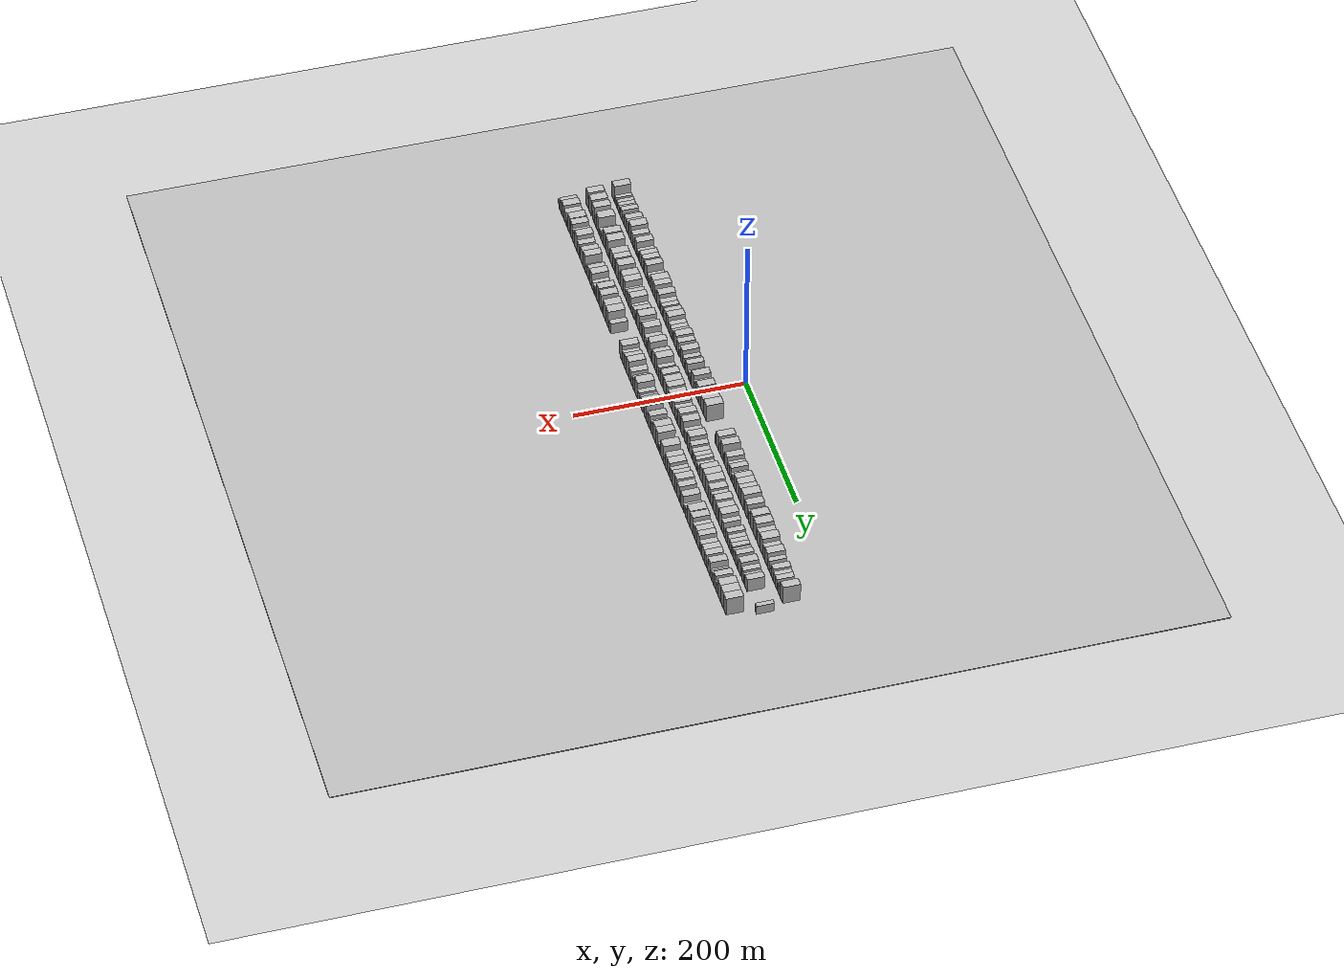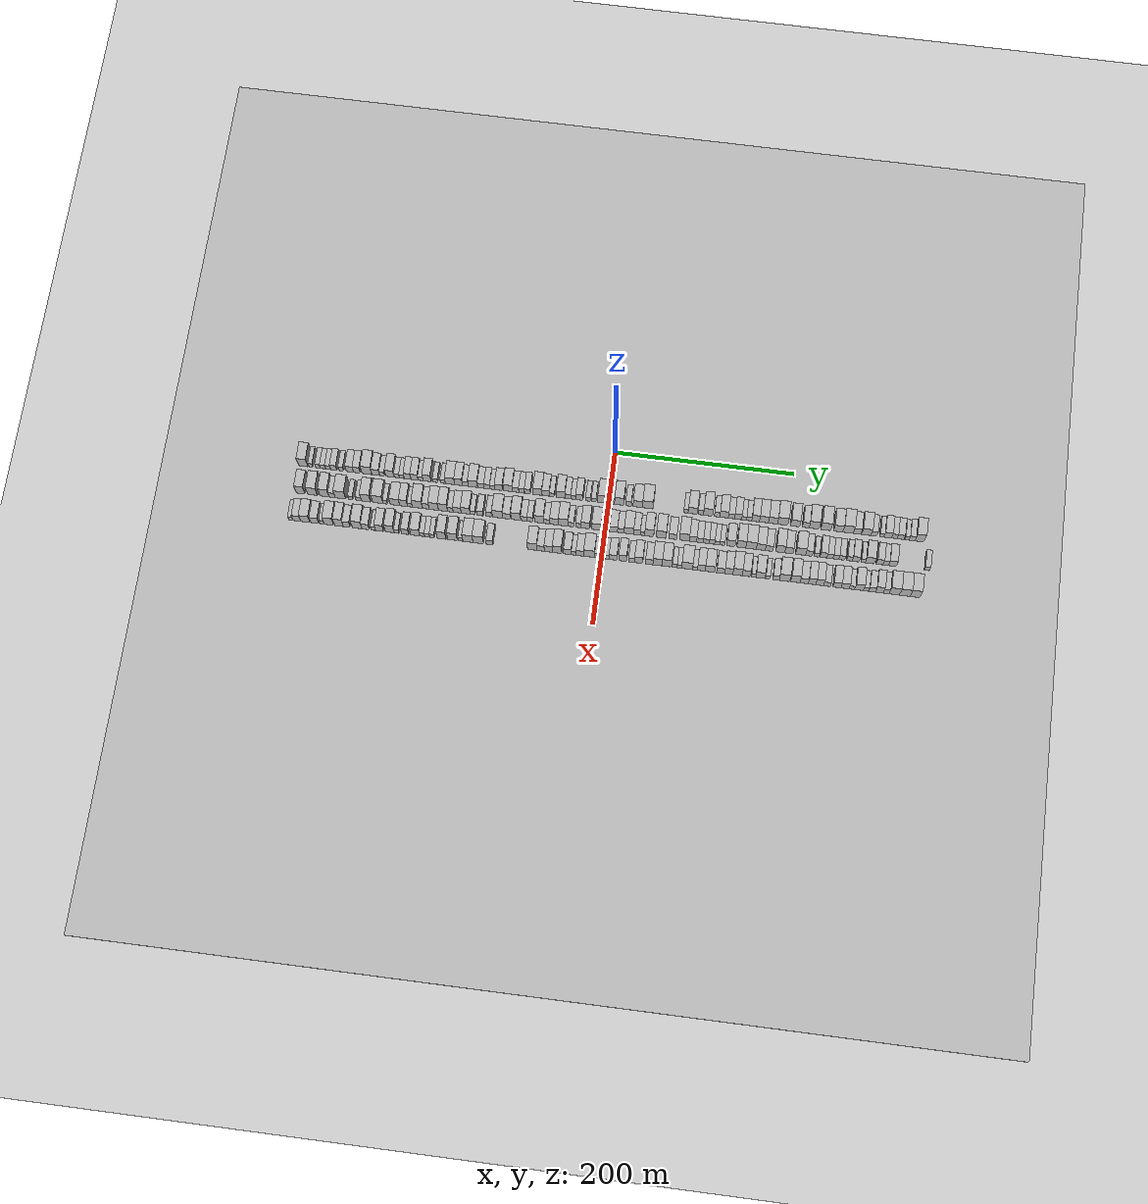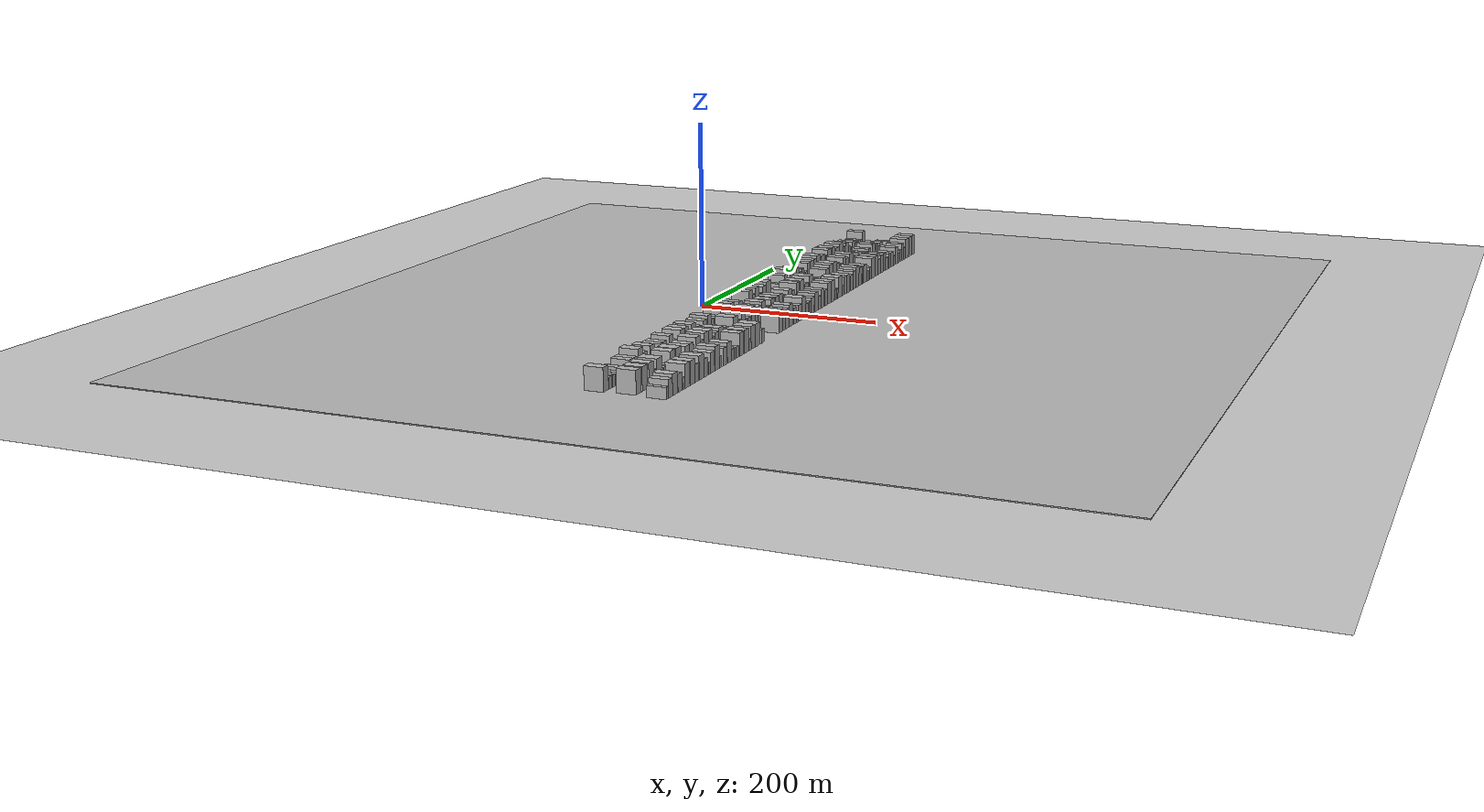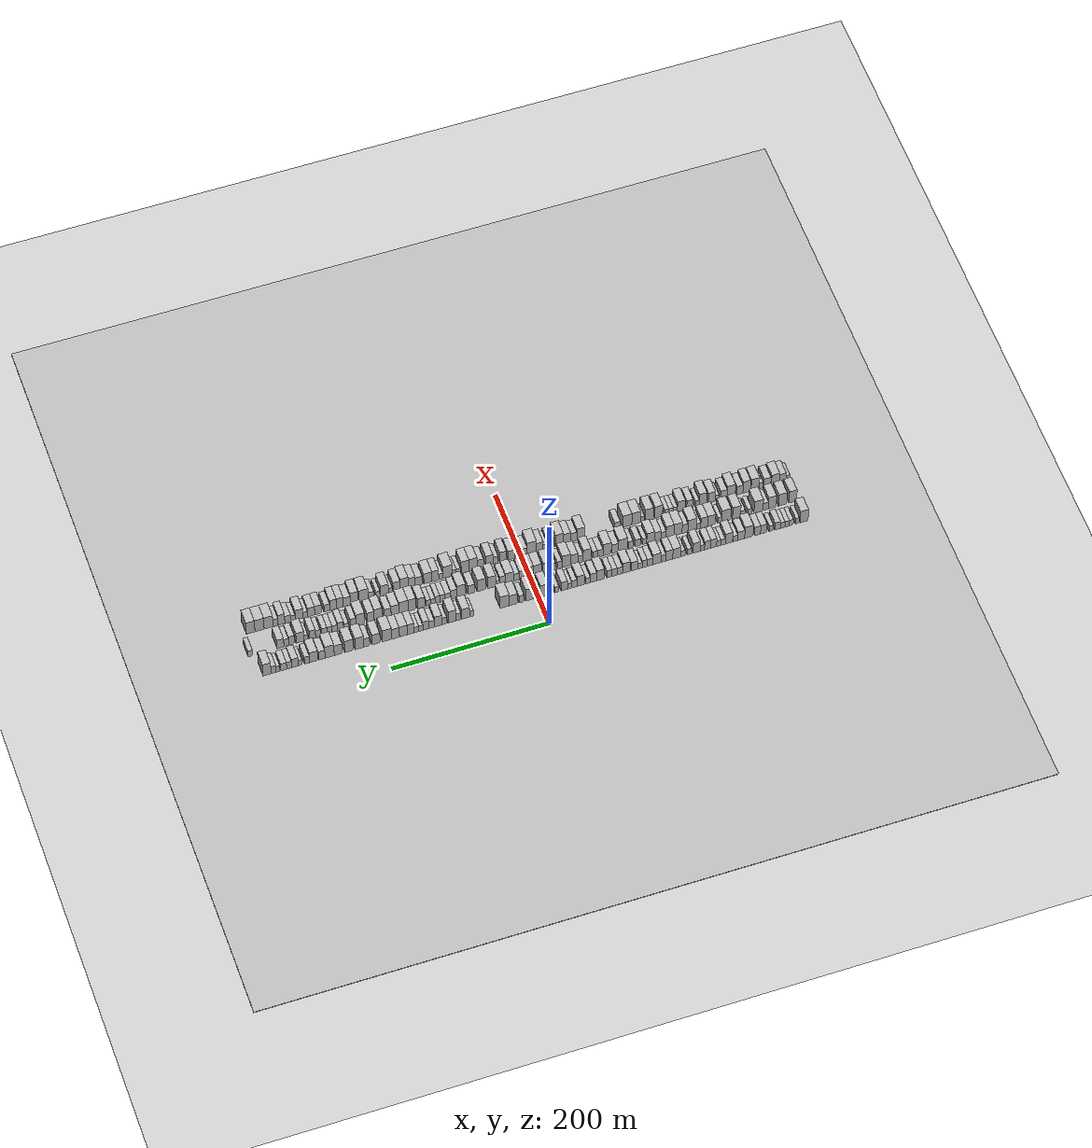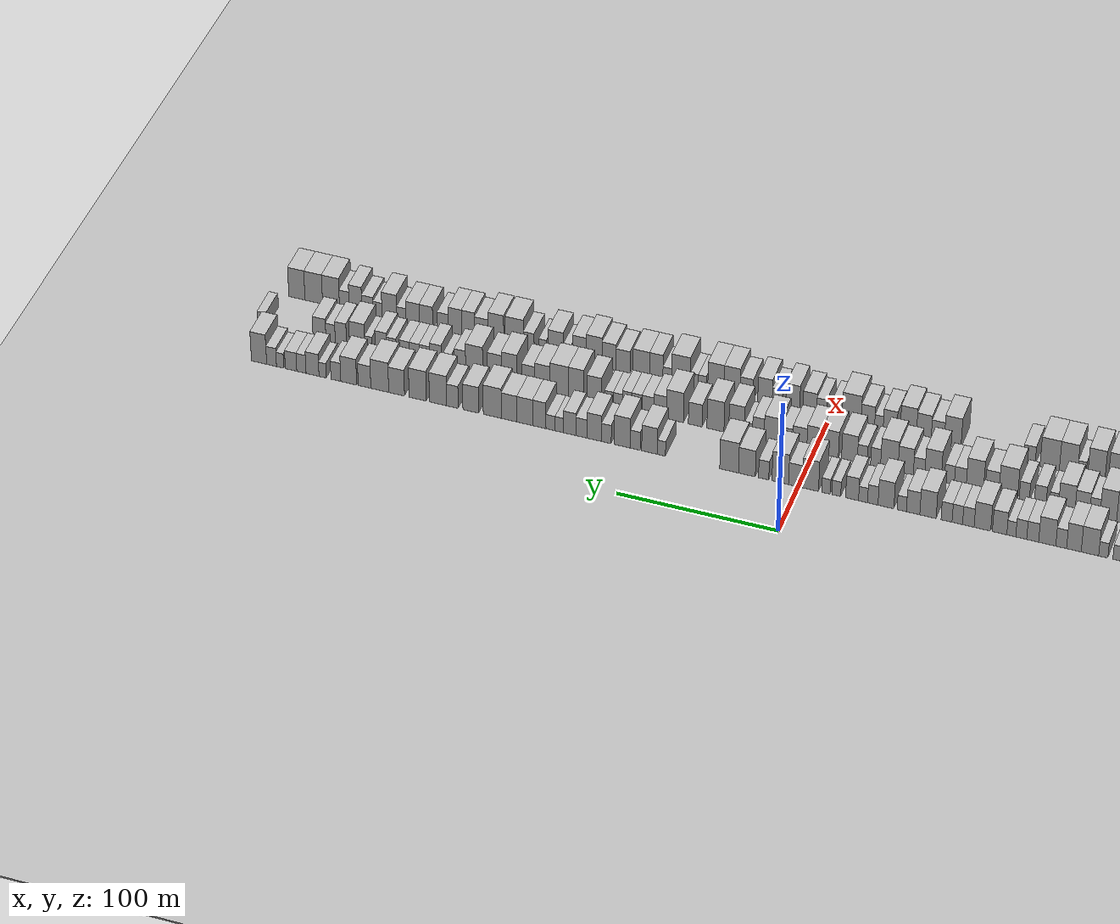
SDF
<?xml version="1.0" encoding="utf-8"?>

<sdf version="1.6">

   <world name="default">

      <gui fullscreen="0">

         <camera name="user_camera">

            <pose>-15 0 4.57585 0 0 0</pose>

            <view_controller>orbit</view_controller>

         </camera>

      </gui>

      <scene>

         <sky>

           <clouds>

             <speed>12</speed>

           </clouds>

         </sky>

         <ambient>0.4 0.4 0.4 1</ambient>

         <background>0.7 0.7 0.7 1</background>

         <shadows>1</shadows>

      </scene>

      <gravity>0 0 -9.8066</gravity>

      <magnetic_field>6e-06 2.3e-05 -4.2e-05</magnetic_field>

      <physics default="0" name="default_physics" type="ode">

         <ode>

            <solver>

               <type>quick</type>

               <iters>10</iters>

               <sor>1.0</sor>

               <use_dynamic_moi_rescaling>0</use_dynamic_moi_rescaling>

            </solver>

            <constraints>

               <cfm>0</cfm>

               <erp>0.2</erp>

               <contact_max_correcting_vel>100</contact_max_correcting_vel>

               <contact_surface_layer>0.001</contact_surface_layer>

            </constraints>

         </ode>

         <max_step_size>0.004</max_step_size>

         <real_time_factor>1</real_time_factor>

         <real_time_update_rate>250</real_time_update_rate>

      </physics>

      <light name="sun" type="directional">

         <cast_shadows>1</cast_shadows>

         <pose>0 0 10 0 0 0</pose>

         <diffuse>0.8 0.8 0.8 1</diffuse>

         <specular>0.2 0.2 0.2 1</specular>

         <attenuation>

            <range>1000</range>

            <constant>0.9</constant>

            <linear>0.01</linear>

            <quadratic>0.001</quadratic>

         </attenuation>

         <direction>-0.5 0.1 -0.9</direction>

      </light>

      <include>

         <name>ground_plane_1</name>

         <uri>model://HANNAS_ground_plane</uri>

         <pose>0 0 0  0 0 0</pose>

      </include>

      <include>

         <name>ground_plane_2</name>

         <uri>model://HANNAS_ground_plane</uri>

         <pose>100 0 0  0 0 0</pose>

      </include>

      <model name="building_1">

         <static>1</static>

         <pose frame="">50.0000 -342.7937 0 0.000000 0.000000 0.000000</pose>

         <link name="link">

            <pose frame="">0 0 12.00 0 0 0</pose>

            <collision name="collision">

               <geometry>

                  <box>

                     <size>20.0000 10.4127 24.0000</size>

                  </box>

               </geometry>

               <max_contacts>10</max_contacts>

               <surface>

                  <contact>

                     <ode/>

                  </contact>

                  <bounce/>

                  <friction>

                     <torsional>

                        <ode/>

                     </torsional>

                     <ode/>

                  </friction>

               </surface>

            </collision>

            <visual name="visual">

               <cast_shadows>0</cast_shadows>

               <geometry>

                  <box>

                     <size>20.0000 10.4127 24.0000</size>

                  </box>

               </geometry>

               <material>

                  <script>

                     <uri>model://HANNAS_wall/materials/scripts</uri>

                     <uri>model://HANNAS_wall/materials/textures</uri>

                     <name>vrc/HANNAS_wall</name>

                  </script>

               </material>

            </visual>

            <self_collide>0</self_collide>

            <enable_wind>0</enable_wind>

            <kinematic>0</kinematic>

         </link>

      </model>

      <model name="building_2">

         <static>1</static>

         <pose frame="">50.0000 -334.1725 0 0.000000 0.000000 0.000000</pose>

         <link name="link">

            <pose frame="">0 0 6.00 0 0 0</pose>

            <collision name="collision">

               <geometry>

                  <box>

                     <size>20.0000 4.8296 12.0000</size>

                  </box>

               </geometry>

               <max_contacts>10</max_contacts>

               <surface>

                  <contact>

                     <ode/>

                  </contact>

                  <bounce/>

                  <friction>

                     <torsional>

                        <ode/>

                     </torsional>

                     <ode/>

                  </friction>

               </surface>

            </collision>

            <visual name="visual">

               <cast_shadows>0</cast_shadows>

               <geometry>

                  <box>

                     <size>20.0000 4.8296 12.0000</size>

                  </box>

               </geometry>

               <material>

                  <script>

                     <uri>model://HANNAS_wall/materials/scripts</uri>

                     <uri>model://HANNAS_wall/materials/textures</uri>

                     <name>vrc/HANNAS_wall</name>

                  </script>

               </material>

            </visual>

            <self_collide>0</self_collide>

            <enable_wind>0</enable_wind>

            <kinematic>0</kinematic>

         </link>

      </model>

      <model name="building_3">

         <static>1</static>

         <pose frame="">50.0000 -326.1442 0 0.000000 0.000000 0.000000</pose>

         <link name="link">

            <pose frame="">0 0 6.00 0 0 0</pose>

            <collision name="collision">

               <geometry>

                  <box>

                     <size>20.0000 5.2270 12.0000</size>

                  </box>

               </geometry>

               <max_contacts>10</max_contacts>

               <surface>

                  <contact>

                     <ode/>

                  </contact>

                  <bounce/>

                  <friction>

                     <torsional>

                        <ode/>

                     </torsional>

                     <ode/>

                  </friction>

               </surface>

            </collision>

            <visual name="visual">

               <cast_shadows>0</cast_shadows>

               <geometry>

                  <box>

                     <size>20.0000 5.2270 12.0000</size>

                  </box>

               </geometry>

               <material>

                  <script>

                     <uri>model://HANNAS_wall/materials/scripts</uri>

                     <uri>model://HANNAS_wall/materials/textures</uri>

                     <name>vrc/HANNAS_wall</name>

                  </script>

               </material>

            </visual>

            <self_collide>0</self_collide>

            <enable_wind>0</enable_wind>

            <kinematic>0</kinematic>

         </link>

      </model>

      <model name="building_4">

         <static>1</static>

         <pose frame="">50.0000 -320.6596 0 0.000000 0.000000 0.000000</pose>

         <link name="link">

            <pose frame="">0 0 6.00 0 0 0</pose>

            <collision name="collision">

               <geometry>

                  <box>

                     <size>20.0000 5.7422 12.0000</size>

                  </box>

               </geometry>

               <max_contacts>10</max_contacts>

               <surface>

                  <contact>

                     <ode/>

                  </contact>

                  <bounce/>

                  <friction>

                     <torsional>

                        <ode/>

                     </torsional>

                     <ode/>

                  </friction>

               </surface>

            </collision>

            <visual name="visual">

               <cast_shadows>0</cast_shadows>

               <geometry>

                  <box>

                     <size>20.0000 5.7422 12.0000</size>

                  </box>

               </geometry>

               <material>

                  <script>

                     <uri>model://HANNAS_wall/materials/scripts</uri>

                     <uri>model://HANNAS_wall/materials/textures</uri>

                     <name>vrc/HANNAS_wall</name>

                  </script>

               </material>

            </visual>

            <self_collide>0</self_collide>

            <enable_wind>0</enable_wind>

            <kinematic>0</kinematic>

         </link>

      </model>

      <model name="building_5">

         <static>1</static>

         <pose frame="">50.0000 -314.8984 0 0.000000 0.000000 0.000000</pose>

         <link name="link">

            <pose frame="">0 0 6.00 0 0 0</pose>

            <collision name="collision">

               <geometry>

                  <box>

                     <size>20.0000 5.7800 12.0000</size>

                  </box>

               </geometry>

               <max_contacts>10</max_contacts>

               <surface>

                  <contact>

                     <ode/>

                  </contact>

                  <bounce/>

                  <friction>

                     <torsional>

                        <ode/>

                     </torsional>

                     <ode/>

                  </friction>

               </surface>

            </collision>

            <visual name="visual">

               <cast_shadows>0</cast_shadows>

               <geometry>

                  <box>

                     <size>20.0000 5.7800 12.0000</size>

                  </box>

               </geometry>

               <material>

                  <script>

                     <uri>model://HANNAS_wall/materials/scripts</uri>

                     <uri>model://HANNAS_wall/materials/textures</uri>

                     <name>vrc/HANNAS_wall</name>

                  </script>

               </material>

            </visual>

            <self_collide>0</self_collide>

            <enable_wind>0</enable_wind>

            <kinematic>0</kinematic>

         </link>

      </model>

      <model name="building_6">

         <static>1</static>

         <pose frame="">50.0000 -308.4191 0 0.000000 0.000000 0.000000</pose>

         <link name="link">

            <pose frame="">0 0 7.50 0 0 0</pose>

            <collision name="collision">

               <geometry>

                  <box>

                     <size>20.0000 7.1786 15.0000</size>

                  </box>

               </geometry>

               <max_contacts>10</max_contacts>

               <surface>

                  <contact>

                     <ode/>

                  </contact>

                  <bounce/>

                  <friction>

                     <torsional>

                        <ode/>

                     </torsional>

                     <ode/>

                  </friction>

               </surface>

            </collision>

            <visual name="visual">

               <cast_shadows>0</cast_shadows>

               <geometry>

                  <box>

                     <size>20.0000 7.1786 15.0000</size>

                  </box>

               </geometry>

               <material>

                  <script>

                     <uri>model://HANNAS_wall/materials/scripts</uri>

                     <uri>model://HANNAS_wall/materials/textures</uri>

                     <name>vrc/HANNAS_wall</name>

                  </script>

               </material>

            </visual>

            <self_collide>0</self_collide>

            <enable_wind>0</enable_wind>

            <kinematic>0</kinematic>

         </link>

      </model>

      <model name="building_7">

         <static>1</static>

         <pose frame="">50.0000 -300.0968 0 0.000000 0.000000 0.000000</pose>

         <link name="link">

            <pose frame="">0 0 6.00 0 0 0</pose>

            <collision name="collision">

               <geometry>

                  <box>

                     <size>20.0000 5.4661 12.0000</size>

                  </box>

               </geometry>

               <max_contacts>10</max_contacts>

               <surface>

                  <contact>

                     <ode/>

                  </contact>

                  <bounce/>

                  <friction>

                     <torsional>

                        <ode/>

                     </torsional>

                     <ode/>

                  </friction>

               </surface>

            </collision>

            <visual name="visual">

               <cast_shadows>0</cast_shadows>

               <geometry>

                  <box>

                     <size>20.0000 5.4661 12.0000</size>

                  </box>

               </geometry>

               <material>

                  <script>

                     <uri>model://HANNAS_wall/materials/scripts</uri>

                     <uri>model://HANNAS_wall/materials/textures</uri>

                     <name>vrc/HANNAS_wall</name>

                  </script>

               </material>

            </visual>

            <self_collide>0</self_collide>

            <enable_wind>0</enable_wind>

            <kinematic>0</kinematic>

         </link>

      </model>

      <model name="building_8">

         <static>1</static>

         <pose frame="">50.0000 -290.2836 0 0.000000 0.000000 0.000000</pose>

         <link name="link">

            <pose frame="">0 0 9.00 0 0 0</pose>

            <collision name="collision">

               <geometry>

                  <box>

                     <size>20.0000 8.1602 18.0000</size>

                  </box>

               </geometry>

               <max_contacts>10</max_contacts>

               <surface>

                  <contact>

                     <ode/>

                  </contact>

                  <bounce/>

                  <friction>

                     <torsional>

                        <ode/>

                     </torsional>

                     <ode/>

                  </friction>

               </surface>

            </collision>

            <visual name="visual">

               <cast_shadows>0</cast_shadows>

               <geometry>

                  <box>

                     <size>20.0000 8.1602 18.0000</size>

                  </box>

               </geometry>

               <material>

                  <script>

                     <uri>model://HANNAS_wall/materials/scripts</uri>

                     <uri>model://HANNAS_wall/materials/textures</uri>

                     <name>vrc/HANNAS_wall</name>

                  </script>

               </material>

            </visual>

            <self_collide>0</self_collide>

            <enable_wind>0</enable_wind>

            <kinematic>0</kinematic>

         </link>

      </model>

      <model name="building_9">

         <static>1</static>

         <pose frame="">50.0000 -282.3586 0 0.000000 0.000000 0.000000</pose>

         <link name="link">

            <pose frame="">0 0 9.00 0 0 0</pose>

            <collision name="collision">

               <geometry>

                  <box>

                     <size>20.0000 7.6899 18.0000</size>

                  </box>

               </geometry>

               <max_contacts>10</max_contacts>

               <surface>

                  <contact>

                     <ode/>

                  </contact>

                  <bounce/>

                  <friction>

                     <torsional>

                        <ode/>

                     </torsional>

                     <ode/>

                  </friction>

               </surface>

            </collision>

            <visual name="visual">

               <cast_shadows>0</cast_shadows>

               <geometry>

                  <box>

                     <size>20.0000 7.6899 18.0000</size>

                  </box>

               </geometry>

               <material>

                  <script>

                     <uri>model://HANNAS_wall/materials/scripts</uri>

                     <uri>model://HANNAS_wall/materials/textures</uri>

                     <name>vrc/HANNAS_wall</name>

                  </script>

               </material>

            </visual>

            <self_collide>0</self_collide>

            <enable_wind>0</enable_wind>

            <kinematic>0</kinematic>

         </link>

      </model>

      <model name="building_10">

         <static>1</static>

         <pose frame="">50.0000 -271.0136 0 0.000000 0.000000 0.000000</pose>

         <link name="link">

            <pose frame="">0 0 12.00 0 0 0</pose>

            <collision name="collision">

               <geometry>

                  <box>

                     <size>20.0000 11.0002 24.0000</size>

                  </box>

               </geometry>

               <max_contacts>10</max_contacts>

               <surface>

                  <contact>

                     <ode/>

                  </contact>

                  <bounce/>

                  <friction>

                     <torsional>

                        <ode/>

                     </torsional>

                     <ode/>

                  </friction>

               </surface>

            </collision>

            <visual name="visual">

               <cast_shadows>0</cast_shadows>

               <geometry>

                  <box>

                     <size>20.0000 11.0002 24.0000</size>

                  </box>

               </geometry>

               <material>

                  <script>

                     <uri>model://HANNAS_wall/materials/scripts</uri>

                     <uri>model://HANNAS_wall/materials/textures</uri>

                     <name>vrc/HANNAS_wall</name>

                  </script>

               </material>

            </visual>

            <self_collide>0</self_collide>

            <enable_wind>0</enable_wind>

            <kinematic>0</kinematic>

         </link>

      </model>

      <model name="building_11">

         <static>1</static>

         <pose frame="">50.0000 -261.1677 0 0.000000 0.000000 0.000000</pose>

         <link name="link">

            <pose frame="">0 0 9.00 0 0 0</pose>

            <collision name="collision">

               <geometry>

                  <box>

                     <size>20.0000 8.6915 18.0000</size>

                  </box>

               </geometry>

               <max_contacts>10</max_contacts>

               <surface>

                  <contact>

                     <ode/>

                  </contact>

                  <bounce/>

                  <friction>

                     <torsional>

                        <ode/>

                     </torsional>

                     <ode/>

                  </friction>

               </surface>

            </collision>

            <visual name="visual">

               <cast_shadows>0</cast_shadows>

               <geometry>

                  <box>

                     <size>20.0000 8.6915 18.0000</size>

                  </box>

               </geometry>

               <material>

                  <script>

                     <uri>model://HANNAS_wall/materials/scripts</uri>

                     <uri>model://HANNAS_wall/materials/textures</uri>

                     <name>vrc/HANNAS_wall</name>

                  </script>

               </material>

            </visual>

            <self_collide>0</self_collide>

            <enable_wind>0</enable_wind>

            <kinematic>0</kinematic>

         </link>

      </model>

      <model name="building_12">

         <static>1</static>

         <pose frame="">50.0000 -253.8751 0 0.000000 0.000000 0.000000</pose>

         <link name="link">

            <pose frame="">0 0 6.00 0 0 0</pose>

            <collision name="collision">

               <geometry>

                  <box>

                     <size>20.0000 5.8936 12.0000</size>

                  </box>

               </geometry>

               <max_contacts>10</max_contacts>

               <surface>

                  <contact>

                     <ode/>

                  </contact>

                  <bounce/>

                  <friction>

                     <torsional>

                        <ode/>

                     </torsional>

                     <ode/>

                  </friction>

               </surface>

            </collision>

            <visual name="visual">

               <cast_shadows>0</cast_shadows>

               <geometry>

                  <box>

                     <size>20.0000 5.8936 12.0000</size>

                  </box>

               </geometry>

               <material>

                  <script>

                     <uri>model://HANNAS_wall/materials/scripts</uri>

                     <uri>model://HANNAS_wall/materials/textures</uri>

                     <name>vrc/HANNAS_wall</name>

                  </script>

               </material>

            </visual>

            <self_collide>0</self_collide>

            <enable_wind>0</enable_wind>

            <kinematic>0</kinematic>

         </link>

      </model>

      <model name="building_13">

         <static>1</static>

         <pose frame="">50.0000 -245.1650 0 0.000000 0.000000 0.000000</pose>

         <link name="link">

            <pose frame="">0 0 10.50 0 0 0</pose>

            <collision name="collision">

               <geometry>

                  <box>

                     <size>20.0000 9.5266 21.0000</size>

                  </box>

               </geometry>

               <max_contacts>10</max_contacts>

               <surface>

                  <contact>

                     <ode/>

                  </contact>

                  <bounce/>

                  <friction>

                     <torsional>

                        <ode/>

                     </torsional>

                     <ode/>

                  </friction>

               </surface>

            </collision>

            <visual name="visual">

               <cast_shadows>0</cast_shadows>

               <geometry>

                  <box>

                     <size>20.0000 9.5266 21.0000</size>

                  </box>

               </geometry>

               <material>

                  <script>

                     <uri>model://HANNAS_wall/materials/scripts</uri>

                     <uri>model://HANNAS_wall/materials/textures</uri>

                     <name>vrc/HANNAS_wall</name>

                  </script>

               </material>

            </visual>

            <self_collide>0</self_collide>

            <enable_wind>0</enable_wind>

            <kinematic>0</kinematic>

         </link>

      </model>

      <model name="building_14">

         <static>1</static>

         <pose frame="">50.0000 -237.5346 0 0.000000 0.000000 0.000000</pose>

         <link name="link">

            <pose frame="">0 0 6.00 0 0 0</pose>

            <collision name="collision">

               <geometry>

                  <box>

                     <size>20.0000 5.7343 12.0000</size>

                  </box>

               </geometry>

               <max_contacts>10</max_contacts>

               <surface>

                  <contact>

                     <ode/>

                  </contact>

                  <bounce/>

                  <friction>

                     <torsional>

                        <ode/>

                     </torsional>

                     <ode/>

                  </friction>

               </surface>

            </collision>

            <visual name="visual">

               <cast_shadows>0</cast_shadows>

               <geometry>

                  <box>

                     <size>20.0000 5.7343 12.0000</size>

                  </box>

               </geometry>

               <material>

                  <script>

                     <uri>model://HANNAS_wall/materials/scripts</uri>

                     <uri>model://HANNAS_wall/materials/textures</uri>

                     <name>vrc/HANNAS_wall</name>

                  </script>

               </material>

            </visual>

            <self_collide>0</self_collide>

            <enable_wind>0</enable_wind>

            <kinematic>0</kinematic>

         </link>

      </model>

      <model name="building_15">

         <static>1</static>

         <pose frame="">50.0000 -231.9547 0 0.000000 0.000000 0.000000</pose>

         <link name="link">

            <pose frame="">0 0 6.00 0 0 0</pose>

            <collision name="collision">

               <geometry>

                  <box>

                     <size>20.0000 5.4256 12.0000</size>

                  </box>

               </geometry>

               <max_contacts>10</max_contacts>

               <surface>

                  <contact>

                     <ode/>

                  </contact>

                  <bounce/>

                  <friction>

                     <torsional>

                        <ode/>

                     </torsional>

                     <ode/>

                  </friction>

               </surface>

            </collision>

            <visual name="visual">

               <cast_shadows>0</cast_shadows>

               <geometry>

                  <box>

                     <size>20.0000 5.4256 12.0000</size>

                  </box>

               </geometry>

               <material>

                  <script>

                     <uri>model://HANNAS_wall/materials/scripts</uri>

                     <uri>model://HANNAS_wall/materials/textures</uri>

                     <name>vrc/HANNAS_wall</name>

                  </script>

               </material>

            </visual>

            <self_collide>0</self_collide>

            <enable_wind>0</enable_wind>

            <kinematic>0</kinematic>

         </link>

      </model>

      <model name="building_16">

         <static>1</static>

         <pose frame="">50.0000 -225.4672 0 0.000000 0.000000 0.000000</pose>

         <link name="link">

            <pose frame="">0 0 9.00 0 0 0</pose>

            <collision name="collision">

               <geometry>

                  <box>

                     <size>20.0000 7.5494 18.0000</size>

                  </box>

               </geometry>

               <max_contacts>10</max_contacts>

               <surface>

                  <contact>

                     <ode/>

                  </contact>

                  <bounce/>

                  <friction>

                     <torsional>

                        <ode/>

                     </torsional>

                     <ode/>

                  </friction>

               </surface>

            </collision>

            <visual name="visual">

               <cast_shadows>0</cast_shadows>

               <geometry>

                  <box>

                     <size>20.0000 7.5494 18.0000</size>

                  </box>

               </geometry>

               <material>

                  <script>

                     <uri>model://HANNAS_wall/materials/scripts</uri>

                     <uri>model://HANNAS_wall/materials/textures</uri>

                     <name>vrc/HANNAS_wall</name>

                  </script>

               </material>

            </visual>

            <self_collide>0</self_collide>

            <enable_wind>0</enable_wind>

            <kinematic>0</kinematic>

         </link>

      </model>

      <model name="building_17">

         <static>1</static>

         <pose frame="">50.0000 -217.6418 0 0.000000 0.000000 0.000000</pose>

         <link name="link">

            <pose frame="">0 0 9.00 0 0 0</pose>

            <collision name="collision">

               <geometry>

                  <box>

                     <size>20.0000 8.1012 18.0000</size>

                  </box>

               </geometry>

               <max_contacts>10</max_contacts>

               <surface>

                  <contact>

                     <ode/>

                  </contact>

                  <bounce/>

                  <friction>

                     <torsional>

                        <ode/>

                     </torsional>

                     <ode/>

                  </friction>

               </surface>

            </collision>

            <visual name="visual">

               <cast_shadows>0</cast_shadows>

               <geometry>

                  <box>

                     <size>20.0000 8.1012 18.0000</size>

                  </box>

               </geometry>

               <material>

                  <script>

                     <uri>model://HANNAS_wall/materials/scripts</uri>

                     <uri>model://HANNAS_wall/materials/textures</uri>

                     <name>vrc/HANNAS_wall</name>

                  </script>

               </material>

            </visual>

            <self_collide>0</self_collide>

            <enable_wind>0</enable_wind>

            <kinematic>0</kinematic>

         </link>

      </model>

      <model name="building_18">

         <static>1</static>

         <pose frame="">50.0000 -210.8297 0 0.000000 0.000000 0.000000</pose>

         <link name="link">

            <pose frame="">0 0 6.00 0 0 0</pose>

            <collision name="collision">

               <geometry>

                  <box>

                     <size>20.0000 5.5230 12.0000</size>

                  </box>

               </geometry>

               <max_contacts>10</max_contacts>

               <surface>

                  <contact>

                     <ode/>

                  </contact>

                  <bounce/>

                  <friction>

                     <torsional>

                        <ode/>

                     </torsional>

                     <ode/>

                  </friction>

               </surface>

            </collision>

            <visual name="visual">

               <cast_shadows>0</cast_shadows>

               <geometry>

                  <box>

                     <size>20.0000 5.5230 12.0000</size>

                  </box>

               </geometry>

               <material>

                  <script>

                     <uri>model://HANNAS_wall/materials/scripts</uri>

                     <uri>model://HANNAS_wall/materials/textures</uri>

                     <name>vrc/HANNAS_wall</name>

                  </script>

               </material>

            </visual>

            <self_collide>0</self_collide>

            <enable_wind>0</enable_wind>

            <kinematic>0</kinematic>

         </link>

      </model>

      <model name="building_19">

         <static>1</static>

         <pose frame="">50.0000 -203.4928 0 0.000000 0.000000 0.000000</pose>

         <link name="link">

            <pose frame="">0 0 10.50 0 0 0</pose>

            <collision name="collision">

               <geometry>

                  <box>

                     <size>20.0000 9.1509 21.0000</size>

                  </box>

               </geometry>

               <max_contacts>10</max_contacts>

               <surface>

                  <contact>

                     <ode/>

                  </contact>

                  <bounce/>

                  <friction>

                     <torsional>

                        <ode/>

                     </torsional>

                     <ode/>

                  </friction>

               </surface>

            </collision>

            <visual name="visual">

               <cast_shadows>0</cast_shadows>

               <geometry>

                  <box>

                     <size>20.0000 9.1509 21.0000</size>

                  </box>

               </geometry>

               <material>

                  <script>

                     <uri>model://HANNAS_wall/materials/scripts</uri>

                     <uri>model://HANNAS_wall/materials/textures</uri>

                     <name>vrc/HANNAS_wall</name>

                  </script>

               </material>

            </visual>

            <self_collide>0</self_collide>

            <enable_wind>0</enable_wind>

            <kinematic>0</kinematic>

         </link>

      </model>

      <model name="building_20">

         <static>1</static>

         <pose frame="">50.0000 -194.2087 0 0.000000 0.000000 0.000000</pose>

         <link name="link">

            <pose frame="">0 0 6.00 0 0 0</pose>

            <collision name="collision">

               <geometry>

                  <box>

                     <size>20.0000 5.4173 12.0000</size>

                  </box>

               </geometry>

               <max_contacts>10</max_contacts>

               <surface>

                  <contact>

                     <ode/>

                  </contact>

                  <bounce/>

                  <friction>

                     <torsional>

                        <ode/>

                     </torsional>

                     <ode/>

                  </friction>

               </surface>

            </collision>

            <visual name="visual">

               <cast_shadows>0</cast_shadows>

               <geometry>

                  <box>

                     <size>20.0000 5.4173 12.0000</size>

                  </box>

               </geometry>

               <material>

                  <script>

                     <uri>model://HANNAS_wall/materials/scripts</uri>

                     <uri>model://HANNAS_wall/materials/textures</uri>

                     <name>vrc/HANNAS_wall</name>

                  </script>

               </material>

            </visual>

            <self_collide>0</self_collide>

            <enable_wind>0</enable_wind>

            <kinematic>0</kinematic>

         </link>

      </model>

      <model name="building_21">

         <static>1</static>

         <pose frame="">50.0000 -185.7538 0 0.000000 0.000000 0.000000</pose>

         <link name="link">

            <pose frame="">0 0 6.00 0 0 0</pose>

            <collision name="collision">

               <geometry>

                  <box>

                     <size>20.0000 5.4925 12.0000</size>

                  </box>

               </geometry>

               <max_contacts>10</max_contacts>

               <surface>

                  <contact>

                     <ode/>

                  </contact>

                  <bounce/>

                  <friction>

                     <torsional>

                        <ode/>

                     </torsional>

                     <ode/>

                  </friction>

               </surface>

            </collision>

            <visual name="visual">

               <cast_shadows>0</cast_shadows>

               <geometry>

                  <box>

                     <size>20.0000 5.4925 12.0000</size>

                  </box>

               </geometry>

               <material>

                  <script>

                     <uri>model://HANNAS_wall/materials/scripts</uri>

                     <uri>model://HANNAS_wall/materials/textures</uri>

                     <name>vrc/HANNAS_wall</name>

                  </script>

               </material>

            </visual>

            <self_collide>0</self_collide>

            <enable_wind>0</enable_wind>

            <kinematic>0</kinematic>

         </link>

      </model>

      <model name="building_22">

         <static>1</static>

         <pose frame="">50.0000 -177.7579 0 0.000000 0.000000 0.000000</pose>

         <link name="link">

            <pose frame="">0 0 10.50 0 0 0</pose>

            <collision name="collision">

               <geometry>

                  <box>

                     <size>20.0000 10.4993 21.0000</size>

                  </box>

               </geometry>

               <max_contacts>10</max_contacts>

               <surface>

                  <contact>

                     <ode/>

                  </contact>

                  <bounce/>

                  <friction>

                     <torsional>

                        <ode/>

                     </torsional>

                     <ode/>

                  </friction>

               </surface>

            </collision>

            <visual name="visual">

               <cast_shadows>0</cast_shadows>

               <geometry>

                  <box>

                     <size>20.0000 10.4993 21.0000</size>

                  </box>

               </geometry>

               <material>

                  <script>

                     <uri>model://HANNAS_wall/materials/scripts</uri>

                     <uri>model://HANNAS_wall/materials/textures</uri>

                     <name>vrc/HANNAS_wall</name>

                  </script>

               </material>

            </visual>

            <self_collide>0</self_collide>

            <enable_wind>0</enable_wind>

            <kinematic>0</kinematic>

         </link>

      </model>

      <model name="building_23">

         <static>1</static>

         <pose frame="">50.0000 -168.1030 0 0.000000 0.000000 0.000000</pose>

         <link name="link">

            <pose frame="">0 0 10.50 0 0 0</pose>

            <collision name="collision">

               <geometry>

                  <box>

                     <size>20.0000 8.8106 21.0000</size>

                  </box>

               </geometry>

               <max_contacts>10</max_contacts>

               <surface>

                  <contact>

                     <ode/>

                  </contact>

                  <bounce/>

                  <friction>

                     <torsional>

                        <ode/>

                     </torsional>

                     <ode/>

                  </friction>

               </surface>

            </collision>

            <visual name="visual">

               <cast_shadows>0</cast_shadows>

               <geometry>

                  <box>

                     <size>20.0000 8.8106 21.0000</size>

                  </box>

               </geometry>

               <material>

                  <script>

                     <uri>model://HANNAS_wall/materials/scripts</uri>

                     <uri>model://HANNAS_wall/materials/textures</uri>

                     <name>vrc/HANNAS_wall</name>

                  </script>

               </material>

            </visual>

            <self_collide>0</self_collide>

            <enable_wind>0</enable_wind>

            <kinematic>0</kinematic>

         </link>

      </model>

      <model name="building_24">

         <static>1</static>

         <pose frame="">50.0000 -160.4572 0 0.000000 0.000000 0.000000</pose>

         <link name="link">

            <pose frame="">0 0 7.50 0 0 0</pose>

            <collision name="collision">

               <geometry>

                  <box>

                     <size>20.0000 6.4809 15.0000</size>

                  </box>

               </geometry>

               <max_contacts>10</max_contacts>

               <surface>

                  <contact>

                     <ode/>

                  </contact>

                  <bounce/>

                  <friction>

                     <torsional>

                        <ode/>

                     </torsional>

                     <ode/>

                  </friction>

               </surface>

            </collision>

            <visual name="visual">

               <cast_shadows>0</cast_shadows>

               <geometry>

                  <box>

                     <size>20.0000 6.4809 15.0000</size>

                  </box>

               </geometry>

               <material>

                  <script>

                     <uri>model://HANNAS_wall/materials/scripts</uri>

                     <uri>model://HANNAS_wall/materials/textures</uri>

                     <name>vrc/HANNAS_wall</name>

                  </script>

               </material>

            </visual>

            <self_collide>0</self_collide>

            <enable_wind>0</enable_wind>

            <kinematic>0</kinematic>

         </link>

      </model>

      <model name="building_25">

         <static>1</static>

         <pose frame="">50.0000 -152.0368 0 0.000000 0.000000 0.000000</pose>

         <link name="link">

            <pose frame="">0 0 10.50 0 0 0</pose>

            <collision name="collision">

               <geometry>

                  <box>

                     <size>20.0000 10.3600 21.0000</size>

                  </box>

               </geometry>

               <max_contacts>10</max_contacts>

               <surface>

                  <contact>

                     <ode/>

                  </contact>

                  <bounce/>

                  <friction>

                     <torsional>

                        <ode/>

                     </torsional>

                     <ode/>

                  </friction>

               </surface>

            </collision>

            <visual name="visual">

               <cast_shadows>0</cast_shadows>

               <geometry>

                  <box>

                     <size>20.0000 10.3600 21.0000</size>

                  </box>

               </geometry>

               <material>

                  <script>

                     <uri>model://HANNAS_wall/materials/scripts</uri>

                     <uri>model://HANNAS_wall/materials/textures</uri>

                     <name>vrc/HANNAS_wall</name>

                  </script>

               </material>

            </visual>

            <self_collide>0</self_collide>

            <enable_wind>0</enable_wind>

            <kinematic>0</kinematic>

         </link>

      </model>

      <model name="building_26">

         <static>1</static>

         <pose frame="">50.0000 -143.2596 0 0.000000 0.000000 0.000000</pose>

         <link name="link">

            <pose frame="">0 0 7.50 0 0 0</pose>

            <collision name="collision">

               <geometry>

                  <box>

                     <size>20.0000 7.1944 15.0000</size>

                  </box>

               </geometry>

               <max_contacts>10</max_contacts>

               <surface>

                  <contact>

                     <ode/>

                  </contact>

                  <bounce/>

                  <friction>

                     <torsional>

                        <ode/>

                     </torsional>

                     <ode/>

                  </friction>

               </surface>

            </collision>

            <visual name="visual">

               <cast_shadows>0</cast_shadows>

               <geometry>

                  <box>

                     <size>20.0000 7.1944 15.0000</size>

                  </box>

               </geometry>

               <material>

                  <script>

                     <uri>model://HANNAS_wall/materials/scripts</uri>

                     <uri>model://HANNAS_wall/materials/textures</uri>

                     <name>vrc/HANNAS_wall</name>

                  </script>

               </material>

            </visual>

            <self_collide>0</self_collide>

            <enable_wind>0</enable_wind>

            <kinematic>0</kinematic>

         </link>

      </model>

      <model name="building_27">

         <static>1</static>

         <pose frame="">50.0000 -136.3600 0 0.000000 0.000000 0.000000</pose>

         <link name="link">

            <pose frame="">0 0 7.50 0 0 0</pose>

            <collision name="collision">

               <geometry>

                  <box>

                     <size>20.0000 6.6048 15.0000</size>

                  </box>

               </geometry>

               <max_contacts>10</max_contacts>

               <surface>

                  <contact>

                     <ode/>

                  </contact>

                  <bounce/>

                  <friction>

                     <torsional>

                        <ode/>

                     </torsional>

                     <ode/>

                  </friction>

               </surface>

            </collision>

            <visual name="visual">

               <cast_shadows>0</cast_shadows>

               <geometry>

                  <box>

                     <size>20.0000 6.6048 15.0000</size>

                  </box>

               </geometry>

               <material>

                  <script>

                     <uri>model://HANNAS_wall/materials/scripts</uri>

                     <uri>model://HANNAS_wall/materials/textures</uri>

                     <name>vrc/HANNAS_wall</name>

                  </script>

               </material>

            </visual>

            <self_collide>0</self_collide>

            <enable_wind>0</enable_wind>

            <kinematic>0</kinematic>

         </link>

      </model>

      <model name="building_28">

         <static>1</static>

         <pose frame="">50.0000 -130.3488 0 0.000000 0.000000 0.000000</pose>

         <link name="link">

            <pose frame="">0 0 6.00 0 0 0</pose>

            <collision name="collision">

               <geometry>

                  <box>

                     <size>20.0000 5.4176 12.0000</size>

                  </box>

               </geometry>

               <max_contacts>10</max_contacts>

               <surface>

                  <contact>

                     <ode/>

                  </contact>

                  <bounce/>

                  <friction>

                     <torsional>

                        <ode/>

                     </torsional>

                     <ode/>

                  </friction>

               </surface>

            </collision>

            <visual name="visual">

               <cast_shadows>0</cast_shadows>

               <geometry>

                  <box>

                     <size>20.0000 5.4176 12.0000</size>

                  </box>

               </geometry>

               <material>

                  <script>

                     <uri>model://HANNAS_wall/materials/scripts</uri>

                     <uri>model://HANNAS_wall/materials/textures</uri>

                     <name>vrc/HANNAS_wall</name>

                  </script>

               </material>

            </visual>

            <self_collide>0</self_collide>

            <enable_wind>0</enable_wind>

            <kinematic>0</kinematic>

         </link>

      </model>

      <model name="building_29">

         <static>1</static>

         <pose frame="">50.0000 -123.2638 0 0.000000 0.000000 0.000000</pose>

         <link name="link">

            <pose frame="">0 0 9.00 0 0 0</pose>

            <collision name="collision">

               <geometry>

                  <box>

                     <size>20.0000 8.7524 18.0000</size>

                  </box>

               </geometry>

               <max_contacts>10</max_contacts>

               <surface>

                  <contact>

                     <ode/>

                  </contact>

                  <bounce/>

                  <friction>

                     <torsional>

                        <ode/>

                     </torsional>

                     <ode/>

                  </friction>

               </surface>

            </collision>

            <visual name="visual">

               <cast_shadows>0</cast_shadows>

               <geometry>

                  <box>

                     <size>20.0000 8.7524 18.0000</size>

                  </box>

               </geometry>

               <material>

                  <script>

                     <uri>model://HANNAS_wall/materials/scripts</uri>

                     <uri>model://HANNAS_wall/materials/textures</uri>

                     <name>vrc/HANNAS_wall</name>

                  </script>

               </material>

            </visual>

            <self_collide>0</self_collide>

            <enable_wind>0</enable_wind>

            <kinematic>0</kinematic>

         </link>

      </model>

      <model name="building_30">

         <static>1</static>

         <pose frame="">50.0000 -112.8413 0 0.000000 0.000000 0.000000</pose>

         <link name="link">

            <pose frame="">0 0 10.50 0 0 0</pose>

            <collision name="collision">

               <geometry>

                  <box>

                     <size>20.0000 10.0927 21.0000</size>

                  </box>

               </geometry>

               <max_contacts>10</max_contacts>

               <surface>

                  <contact>

                     <ode/>

                  </contact>

                  <bounce/>

                  <friction>

                     <torsional>

                        <ode/>

                     </torsional>

                     <ode/>

                  </friction>

               </surface>

            </collision>

            <visual name="visual">

               <cast_shadows>0</cast_shadows>

               <geometry>

                  <box>

                     <size>20.0000 10.0927 21.0000</size>

                  </box>

               </geometry>

               <material>

                  <script>

                     <uri>model://HANNAS_wall/materials/scripts</uri>

                     <uri>model://HANNAS_wall/materials/textures</uri>

                     <name>vrc/HANNAS_wall</name>

                  </script>

               </material>

            </visual>

            <self_collide>0</self_collide>

            <enable_wind>0</enable_wind>

            <kinematic>0</kinematic>

         </link>

      </model>

      <model name="building_31">

         <static>1</static>

         <pose frame="">50.0000 -104.2819 0 0.000000 0.000000 0.000000</pose>

         <link name="link">

            <pose frame="">0 0 7.50 0 0 0</pose>

            <collision name="collision">

               <geometry>

                  <box>

                     <size>20.0000 7.0259 15.0000</size>

                  </box>

               </geometry>

               <max_contacts>10</max_contacts>

               <surface>

                  <contact>

                     <ode/>

                  </contact>

                  <bounce/>

                  <friction>

                     <torsional>

                        <ode/>

                     </torsional>

                     <ode/>

                  </friction>

               </surface>

            </collision>

            <visual name="visual">

               <cast_shadows>0</cast_shadows>

               <geometry>

                  <box>

                     <size>20.0000 7.0259 15.0000</size>

                  </box>

               </geometry>

               <material>

                  <script>

                     <uri>model://HANNAS_wall/materials/scripts</uri>

                     <uri>model://HANNAS_wall/materials/textures</uri>

                     <name>vrc/HANNAS_wall</name>

                  </script>

               </material>

            </visual>

            <self_collide>0</self_collide>

            <enable_wind>0</enable_wind>

            <kinematic>0</kinematic>

         </link>

      </model>

      <model name="building_32">

         <static>1</static>

         <pose frame="">50.0000 -97.5649 0 0.000000 0.000000 0.000000</pose>

         <link name="link">

            <pose frame="">0 0 7.50 0 0 0</pose>

            <collision name="collision">

               <geometry>

                  <box>

                     <size>20.0000 6.4082 15.0000</size>

                  </box>

               </geometry>

               <max_contacts>10</max_contacts>

               <surface>

                  <contact>

                     <ode/>

                  </contact>

                  <bounce/>

                  <friction>

                     <torsional>

                        <ode/>

                     </torsional>

                     <ode/>

                  </friction>

               </surface>

            </collision>

            <visual name="visual">

               <cast_shadows>0</cast_shadows>

               <geometry>

                  <box>

                     <size>20.0000 6.4082 15.0000</size>

                  </box>

               </geometry>

               <material>

                  <script>

                     <uri>model://HANNAS_wall/materials/scripts</uri>

                     <uri>model://HANNAS_wall/materials/textures</uri>

                     <name>vrc/HANNAS_wall</name>

                  </script>

               </material>

            </visual>

            <self_collide>0</self_collide>

            <enable_wind>0</enable_wind>

            <kinematic>0</kinematic>

         </link>

      </model>

      <model name="building_33">

         <static>1</static>

         <pose frame="">50.0000 -91.0051 0 0.000000 0.000000 0.000000</pose>

         <link name="link">

            <pose frame="">0 0 7.50 0 0 0</pose>

            <collision name="collision">

               <geometry>

                  <box>

                     <size>20.0000 6.7113 15.0000</size>

                  </box>

               </geometry>

               <max_contacts>10</max_contacts>

               <surface>

                  <contact>

                     <ode/>

                  </contact>

                  <bounce/>

                  <friction>

                     <torsional>

                        <ode/>

                     </torsional>

                     <ode/>

                  </friction>

               </surface>

            </collision>

            <visual name="visual">

               <cast_shadows>0</cast_shadows>

               <geometry>

                  <box>

                     <size>20.0000 6.7113 15.0000</size>

                  </box>

               </geometry>

               <material>

                  <script>

                     <uri>model://HANNAS_wall/materials/scripts</uri>

                     <uri>model://HANNAS_wall/materials/textures</uri>

                     <name>vrc/HANNAS_wall</name>

                  </script>

               </material>

            </visual>

            <self_collide>0</self_collide>

            <enable_wind>0</enable_wind>

            <kinematic>0</kinematic>

         </link>

      </model>

      <model name="building_34">

         <static>1</static>

         <pose frame="">50.0000 -79.6715 0 0.000000 0.000000 0.000000</pose>

         <link name="link">

            <pose frame="">0 0 10.50 0 0 0</pose>

            <collision name="collision">

               <geometry>

                  <box>

                     <size>20.0000 9.9561 21.0000</size>

                  </box>

               </geometry>

               <max_contacts>10</max_contacts>

               <surface>

                  <contact>

                     <ode/>

                  </contact>

                  <bounce/>

                  <friction>

                     <torsional>

                        <ode/>

                     </torsional>

                     <ode/>

                  </friction>

               </surface>

            </collision>

            <visual name="visual">

               <cast_shadows>0</cast_shadows>

               <geometry>

                  <box>

                     <size>20.0000 9.9561 21.0000</size>

                  </box>

               </geometry>

               <material>

                  <script>

                     <uri>model://HANNAS_wall/materials/scripts</uri>

                     <uri>model://HANNAS_wall/materials/textures</uri>

                     <name>vrc/HANNAS_wall</name>

                  </script>

               </material>

            </visual>

            <self_collide>0</self_collide>

            <enable_wind>0</enable_wind>

            <kinematic>0</kinematic>

         </link>

      </model>

      <model name="building_35">

         <static>1</static>

         <pose frame="">50.0000 -70.5820 0 0.000000 0.000000 0.000000</pose>

         <link name="link">

            <pose frame="">0 0 9.00 0 0 0</pose>

            <collision name="collision">

               <geometry>

                  <box>

                     <size>20.0000 8.2228 18.0000</size>

                  </box>

               </geometry>

               <max_contacts>10</max_contacts>

               <surface>

                  <contact>

                     <ode/>

                  </contact>

                  <bounce/>

                  <friction>

                     <torsional>

                        <ode/>

                     </torsional>

                     <ode/>

                  </friction>

               </surface>

            </collision>

            <visual name="visual">

               <cast_shadows>0</cast_shadows>

               <geometry>

                  <box>

                     <size>20.0000 8.2228 18.0000</size>

                  </box>

               </geometry>

               <material>

                  <script>

                     <uri>model://HANNAS_wall/materials/scripts</uri>

                     <uri>model://HANNAS_wall/materials/textures</uri>

                     <name>vrc/HANNAS_wall</name>

                  </script>

               </material>

            </visual>

            <self_collide>0</self_collide>

            <enable_wind>0</enable_wind>

            <kinematic>0</kinematic>

         </link>

      </model>

      <model name="building_36">

         <static>1</static>

         <pose frame="">50.0000 -63.6314 0 0.000000 0.000000 0.000000</pose>

         <link name="link">

            <pose frame="">0 0 6.00 0 0 0</pose>

            <collision name="collision">

               <geometry>

                  <box>

                     <size>20.0000 5.6785 12.0000</size>

                  </box>

               </geometry>

               <max_contacts>10</max_contacts>

               <surface>

                  <contact>

                     <ode/>

                  </contact>

                  <bounce/>

                  <friction>

                     <torsional>

                        <ode/>

                     </torsional>

                     <ode/>

                  </friction>

               </surface>

            </collision>

            <visual name="visual">

               <cast_shadows>0</cast_shadows>

               <geometry>

                  <box>

                     <size>20.0000 5.6785 12.0000</size>

                  </box>

               </geometry>

               <material>

                  <script>

                     <uri>model://HANNAS_wall/materials/scripts</uri>

                     <uri>model://HANNAS_wall/materials/textures</uri>

                     <name>vrc/HANNAS_wall</name>

                  </script>

               </material>

            </visual>

            <self_collide>0</self_collide>

            <enable_wind>0</enable_wind>

            <kinematic>0</kinematic>

         </link>

      </model>

      <model name="building_37">

         <static>1</static>

         <pose frame="">50.0000 -53.9282 0 0.000000 0.000000 0.000000</pose>

         <link name="link">

            <pose frame="">0 0 10.50 0 0 0</pose>

            <collision name="collision">

               <geometry>

                  <box>

                     <size>20.0000 9.7278 21.0000</size>

                  </box>

               </geometry>

               <max_contacts>10</max_contacts>

               <surface>

                  <contact>

                     <ode/>

                  </contact>

                  <bounce/>

                  <friction>

                     <torsional>

                        <ode/>

                     </torsional>

                     <ode/>

                  </friction>

               </surface>

            </collision>

            <visual name="visual">

               <cast_shadows>0</cast_shadows>

               <geometry>

                  <box>

                     <size>20.0000 9.7278 21.0000</size>

                  </box>

               </geometry>

               <material>

                  <script>

                     <uri>model://HANNAS_wall/materials/scripts</uri>

                     <uri>model://HANNAS_wall/materials/textures</uri>

                     <name>vrc/HANNAS_wall</name>

                  </script>

               </material>

            </visual>

            <self_collide>0</self_collide>

            <enable_wind>0</enable_wind>

            <kinematic>0</kinematic>

         </link>

      </model>

      <model name="building_38">

         <static>1</static>

         <pose frame="">50.0000 -45.8464 0 0.000000 0.000000 0.000000</pose>

         <link name="link">

            <pose frame="">0 0 7.50 0 0 0</pose>

            <collision name="collision">

               <geometry>

                  <box>

                     <size>20.0000 6.4358 15.0000</size>

                  </box>

               </geometry>

               <max_contacts>10</max_contacts>

               <surface>

                  <contact>

                     <ode/>

                  </contact>

                  <bounce/>

                  <friction>

                     <torsional>

                        <ode/>

                     </torsional>

                     <ode/>

                  </friction>

               </surface>

            </collision>

            <visual name="visual">

               <cast_shadows>0</cast_shadows>

               <geometry>

                  <box>

                     <size>20.0000 6.4358 15.0000</size>

                  </box>

               </geometry>

               <material>

                  <script>

                     <uri>model://HANNAS_wall/materials/scripts</uri>

                     <uri>model://HANNAS_wall/materials/textures</uri>

                     <name>vrc/HANNAS_wall</name>

                  </script>

               </material>

            </visual>

            <self_collide>0</self_collide>

            <enable_wind>0</enable_wind>

            <kinematic>0</kinematic>

         </link>

      </model>

      <model name="building_39">

         <static>1</static>

         <pose frame="">50.0000 -39.8545 0 0.000000 0.000000 0.000000</pose>

         <link name="link">

            <pose frame="">0 0 6.00 0 0 0</pose>

            <collision name="collision">

               <geometry>

                  <box>

                     <size>20.0000 5.5482 12.0000</size>

                  </box>

               </geometry>

               <max_contacts>10</max_contacts>

               <surface>

                  <contact>

                     <ode/>

                  </contact>

                  <bounce/>

                  <friction>

                     <torsional>

                        <ode/>

                     </torsional>

                     <ode/>

                  </friction>

               </surface>

            </collision>

            <visual name="visual">

               <cast_shadows>0</cast_shadows>

               <geometry>

                  <box>

                     <size>20.0000 5.5482 12.0000</size>

                  </box>

               </geometry>

               <material>

                  <script>

                     <uri>model://HANNAS_wall/materials/scripts</uri>

                     <uri>model://HANNAS_wall/materials/textures</uri>

                     <name>vrc/HANNAS_wall</name>

                  </script>

               </material>

            </visual>

            <self_collide>0</self_collide>

            <enable_wind>0</enable_wind>

            <kinematic>0</kinematic>

         </link>

      </model>

      <model name="building_40">

         <static>1</static>

         <pose frame="">50.0000 -33.0967 0 0.000000 0.000000 0.000000</pose>

         <link name="link">

            <pose frame="">0 0 9.00 0 0 0</pose>

            <collision name="collision">

               <geometry>

                  <box>

                     <size>20.0000 7.9673 18.0000</size>

                  </box>

               </geometry>

               <max_contacts>10</max_contacts>

               <surface>

                  <contact>

                     <ode/>

                  </contact>

                  <bounce/>

                  <friction>

                     <torsional>

                        <ode/>

                     </torsional>

                     <ode/>

                  </friction>

               </surface>

            </collision>

            <visual name="visual">

               <cast_shadows>0</cast_shadows>

               <geometry>

                  <box>

                     <size>20.0000 7.9673 18.0000</size>

                  </box>

               </geometry>

               <material>

                  <script>

                     <uri>model://HANNAS_wall/materials/scripts</uri>

                     <uri>model://HANNAS_wall/materials/textures</uri>

                     <name>vrc/HANNAS_wall</name>

                  </script>

               </material>

            </visual>

            <self_collide>0</self_collide>

            <enable_wind>0</enable_wind>

            <kinematic>0</kinematic>

         </link>

      </model>

      <model name="building_41">

         <static>1</static>

         <pose frame="">50.0000 -23.3904 0 0.000000 0.000000 0.000000</pose>

         <link name="link">

            <pose frame="">0 0 6.00 0 0 0</pose>

            <collision name="collision">

               <geometry>

                  <box>

                     <size>20.0000 5.4453 12.0000</size>

                  </box>

               </geometry>

               <max_contacts>10</max_contacts>

               <surface>

                  <contact>

                     <ode/>

                  </contact>

                  <bounce/>

                  <friction>

                     <torsional>

                        <ode/>

                     </torsional>

                     <ode/>

                  </friction>

               </surface>

            </collision>

            <visual name="visual">

               <cast_shadows>0</cast_shadows>

               <geometry>

                  <box>

                     <size>20.0000 5.4453 12.0000</size>

                  </box>

               </geometry>

               <material>

                  <script>

                     <uri>model://HANNAS_wall/materials/scripts</uri>

                     <uri>model://HANNAS_wall/materials/textures</uri>

                     <name>vrc/HANNAS_wall</name>

                  </script>

               </material>

            </visual>

            <self_collide>0</self_collide>

            <enable_wind>0</enable_wind>

            <kinematic>0</kinematic>

         </link>

      </model>

      <model name="building_42">

         <static>1</static>

         <pose frame="">50.0000 -17.0258 0 0.000000 0.000000 0.000000</pose>

         <link name="link">

            <pose frame="">0 0 6.00 0 0 0</pose>

            <collision name="collision">

               <geometry>

                  <box>

                     <size>20.0000 5.2839 12.0000</size>

                  </box>

               </geometry>

               <max_contacts>10</max_contacts>

               <surface>

                  <contact>

                     <ode/>

                  </contact>

                  <bounce/>

                  <friction>

                     <torsional>

                        <ode/>

                     </torsional>

                     <ode/>

                  </friction>

               </surface>

            </collision>

            <visual name="visual">

               <cast_shadows>0</cast_shadows>

               <geometry>

                  <box>

                     <size>20.0000 5.2839 12.0000</size>

                  </box>

               </geometry>

               <material>

                  <script>

                     <uri>model://HANNAS_wall/materials/scripts</uri>

                     <uri>model://HANNAS_wall/materials/textures</uri>

                     <name>vrc/HANNAS_wall</name>

                  </script>

               </material>

            </visual>

            <self_collide>0</self_collide>

            <enable_wind>0</enable_wind>

            <kinematic>0</kinematic>

         </link>

      </model>

      <model name="building_43">

         <static>1</static>

         <pose frame="">50.0000 -7.3435 0 0.000000 0.000000 0.000000</pose>

         <link name="link">

            <pose frame="">0 0 12.00 0 0 0</pose>

            <collision name="collision">

               <geometry>

                  <box>

                     <size>20.0000 10.0807 24.0000</size>

                  </box>

               </geometry>

               <max_contacts>10</max_contacts>

               <surface>

                  <contact>

                     <ode/>

                  </contact>

                  <bounce/>

                  <friction>

                     <torsional>

                        <ode/>

                     </torsional>

                     <ode/>

                  </friction>

               </surface>

            </collision>

            <visual name="visual">

               <cast_shadows>0</cast_shadows>

               <geometry>

                  <box>

                     <size>20.0000 10.0807 24.0000</size>

                  </box>

               </geometry>

               <material>

                  <script>

                     <uri>model://HANNAS_wall/materials/scripts</uri>

                     <uri>model://HANNAS_wall/materials/textures</uri>

                     <name>vrc/HANNAS_wall</name>

                  </script>

               </material>

            </visual>

            <self_collide>0</self_collide>

            <enable_wind>0</enable_wind>

            <kinematic>0</kinematic>

         </link>

      </model>

      <model name="building_44">

         <static>1</static>

         <pose frame="">50.0000 1.9351 0 0.000000 0.000000 0.000000</pose>

         <link name="link">

            <pose frame="">0 0 9.00 0 0 0</pose>

            <collision name="collision">

               <geometry>

                  <box>

                     <size>20.0000 8.4766 18.0000</size>

                  </box>

               </geometry>

               <max_contacts>10</max_contacts>

               <surface>

                  <contact>

                     <ode/>

                  </contact>

                  <bounce/>

                  <friction>

                     <torsional>

                        <ode/>

                     </torsional>

                     <ode/>

                  </friction>

               </surface>

            </collision>

            <visual name="visual">

               <cast_shadows>0</cast_shadows>

               <geometry>

                  <box>

                     <size>20.0000 8.4766 18.0000</size>

                  </box>

               </geometry>

               <material>

                  <script>

                     <uri>model://HANNAS_wall/materials/scripts</uri>

                     <uri>model://HANNAS_wall/materials/textures</uri>

                     <name>vrc/HANNAS_wall</name>

                  </script>

               </material>

            </visual>

            <self_collide>0</self_collide>

            <enable_wind>0</enable_wind>

            <kinematic>0</kinematic>

         </link>

      </model>

      <model name="building_45">

         <static>1</static>

         <pose frame="">50.0000 11.3053 0 0.000000 0.000000 0.000000</pose>

         <link name="link">

            <pose frame="">0 0 12.00 0 0 0</pose>

            <collision name="collision">

               <geometry>

                  <box>

                     <size>20.0000 10.2639 24.0000</size>

                  </box>

               </geometry>

               <max_contacts>10</max_contacts>

               <surface>

                  <contact>

                     <ode/>

                  </contact>

                  <bounce/>

                  <friction>

                     <torsional>

                        <ode/>

                     </torsional>

                     <ode/>

                  </friction>

               </surface>

            </collision>

            <visual name="visual">

               <cast_shadows>0</cast_shadows>

               <geometry>

                  <box>

                     <size>20.0000 10.2639 24.0000</size>

                  </box>

               </geometry>

               <material>

                  <script>

                     <uri>model://HANNAS_wall/materials/scripts</uri>

                     <uri>model://HANNAS_wall/materials/textures</uri>

                     <name>vrc/HANNAS_wall</name>

                  </script>

               </material>

            </visual>

            <self_collide>0</self_collide>

            <enable_wind>0</enable_wind>

            <kinematic>0</kinematic>

         </link>

      </model>

      <model name="building_46">

         <static>1</static>

         <pose frame="">50.0000 21.6280 0 0.000000 0.000000 0.000000</pose>

         <link name="link">

            <pose frame="">0 0 7.50 0 0 0</pose>

            <collision name="collision">

               <geometry>

                  <box>

                     <size>20.0000 6.3814 15.0000</size>

                  </box>

               </geometry>

               <max_contacts>10</max_contacts>

               <surface>

                  <contact>

                     <ode/>

                  </contact>

                  <bounce/>

                  <friction>

                     <torsional>

                        <ode/>

                     </torsional>

                     <ode/>

                  </friction>

               </surface>

            </collision>

            <visual name="visual">

               <cast_shadows>0</cast_shadows>

               <geometry>

                  <box>

                     <size>20.0000 6.3814 15.0000</size>

                  </box>

               </geometry>

               <material>

                  <script>

                     <uri>model://HANNAS_wall/materials/scripts</uri>

                     <uri>model://HANNAS_wall/materials/textures</uri>

                     <name>vrc/HANNAS_wall</name>

                  </script>

               </material>

            </visual>

            <self_collide>0</self_collide>

            <enable_wind>0</enable_wind>

            <kinematic>0</kinematic>

         </link>

      </model>

      <model name="building_47">

         <static>1</static>

         <pose frame="">50.0000 32.0305 0 0.000000 0.000000 0.000000</pose>

         <link name="link">

            <pose frame="">0 0 10.50 0 0 0</pose>

            <collision name="collision">

               <geometry>

                  <box>

                     <size>20.0000 10.4237 21.0000</size>

                  </box>

               </geometry>

               <max_contacts>10</max_contacts>

               <surface>

                  <contact>

                     <ode/>

                  </contact>

                  <bounce/>

                  <friction>

                     <torsional>

                        <ode/>

                     </torsional>

                     <ode/>

                  </friction>

               </surface>

            </collision>

            <visual name="visual">

               <cast_shadows>0</cast_shadows>

               <geometry>

                  <box>

                     <size>20.0000 10.4237 21.0000</size>

                  </box>

               </geometry>

               <material>

                  <script>

                     <uri>model://HANNAS_wall/materials/scripts</uri>

                     <uri>model://HANNAS_wall/materials/textures</uri>

                     <name>vrc/HANNAS_wall</name>

                  </script>

               </material>

            </visual>

            <self_collide>0</self_collide>

            <enable_wind>0</enable_wind>

            <kinematic>0</kinematic>

         </link>

      </model>

      <model name="building_48">

         <static>1</static>

         <pose frame="">50.0000 43.1093 0 0.000000 0.000000 0.000000</pose>

         <link name="link">

            <pose frame="">0 0 12.00 0 0 0</pose>

            <collision name="collision">

               <geometry>

                  <box>

                     <size>20.0000 11.7338 24.0000</size>

                  </box>

               </geometry>

               <max_contacts>10</max_contacts>

               <surface>

                  <contact>

                     <ode/>

                  </contact>

                  <bounce/>

                  <friction>

                     <torsional>

                        <ode/>

                     </torsional>

                     <ode/>

                  </friction>

               </surface>

            </collision>

            <visual name="visual">

               <cast_shadows>0</cast_shadows>

               <geometry>

                  <box>

                     <size>20.0000 11.7338 24.0000</size>

                  </box>

               </geometry>

               <material>

                  <script>

                     <uri>model://HANNAS_wall/materials/scripts</uri>

                     <uri>model://HANNAS_wall/materials/textures</uri>

                     <name>vrc/HANNAS_wall</name>

                  </script>

               </material>

            </visual>

            <self_collide>0</self_collide>

            <enable_wind>0</enable_wind>

            <kinematic>0</kinematic>

         </link>

      </model>

      <model name="building_49">

         <static>1</static>

         <pose frame="">50.0000 85.4899 0 0.000000 0.000000 0.000000</pose>

         <link name="link">

            <pose frame="">0 0 6.00 0 0 0</pose>

            <collision name="collision">

               <geometry>

                  <box>

                     <size>20.0000 5.0091 12.0000</size>

                  </box>

               </geometry>

               <max_contacts>10</max_contacts>

               <surface>

                  <contact>

                     <ode/>

                  </contact>

                  <bounce/>

                  <friction>

                     <torsional>

                        <ode/>

                     </torsional>

                     <ode/>

                  </friction>

               </surface>

            </collision>

            <visual name="visual">

               <cast_shadows>0</cast_shadows>

               <geometry>

                  <box>

                     <size>20.0000 5.0091 12.0000</size>

                  </box>

               </geometry>

               <material>

                  <script>

                     <uri>model://HANNAS_wall/materials/scripts</uri>

                     <uri>model://HANNAS_wall/materials/textures</uri>

                     <name>vrc/HANNAS_wall</name>

                  </script>

               </material>

            </visual>

            <self_collide>0</self_collide>

            <enable_wind>0</enable_wind>

            <kinematic>0</kinematic>

         </link>

      </model>

      <model name="building_50">

         <static>1</static>

         <pose frame="">50.0000 92.9599 0 0.000000 0.000000 0.000000</pose>

         <link name="link">

            <pose frame="">0 0 10.50 0 0 0</pose>

            <collision name="collision">

               <geometry>

                  <box>

                     <size>20.0000 9.9309 21.0000</size>

                  </box>

               </geometry>

               <max_contacts>10</max_contacts>

               <surface>

                  <contact>

                     <ode/>

                  </contact>

                  <bounce/>

                  <friction>

                     <torsional>

                        <ode/>

                     </torsional>

                     <ode/>

                  </friction>

               </surface>

            </collision>

            <visual name="visual">

               <cast_shadows>0</cast_shadows>

               <geometry>

                  <box>

                     <size>20.0000 9.9309 21.0000</size>

                  </box>

               </geometry>

               <material>

                  <script>

                     <uri>model://HANNAS_wall/materials/scripts</uri>

                     <uri>model://HANNAS_wall/materials/textures</uri>

                     <name>vrc/HANNAS_wall</name>

                  </script>

               </material>

            </visual>

            <self_collide>0</self_collide>

            <enable_wind>0</enable_wind>

            <kinematic>0</kinematic>

         </link>

      </model>

      <model name="building_51">

         <static>1</static>

         <pose frame="">50.0000 101.9746 0 0.000000 0.000000 0.000000</pose>

         <link name="link">

            <pose frame="">0 0 7.50 0 0 0</pose>

            <collision name="collision">

               <geometry>

                  <box>

                     <size>20.0000 6.0986 15.0000</size>

                  </box>

               </geometry>

               <max_contacts>10</max_contacts>

               <surface>

                  <contact>

                     <ode/>

                  </contact>

                  <bounce/>

                  <friction>

                     <torsional>

                        <ode/>

                     </torsional>

                     <ode/>

                  </friction>

               </surface>

            </collision>

            <visual name="visual">

               <cast_shadows>0</cast_shadows>

               <geometry>

                  <box>

                     <size>20.0000 6.0986 15.0000</size>

                  </box>

               </geometry>

               <material>

                  <script>

                     <uri>model://HANNAS_wall/materials/scripts</uri>

                     <uri>model://HANNAS_wall/materials/textures</uri>

                     <name>vrc/HANNAS_wall</name>

                  </script>

               </material>

            </visual>

            <self_collide>0</self_collide>

            <enable_wind>0</enable_wind>

            <kinematic>0</kinematic>

         </link>

      </model>

      <model name="building_52">

         <static>1</static>

         <pose frame="">50.0000 110.0865 0 0.000000 0.000000 0.000000</pose>

         <link name="link">

            <pose frame="">0 0 12.00 0 0 0</pose>

            <collision name="collision">

               <geometry>

                  <box>

                     <size>20.0000 10.1251 24.0000</size>

                  </box>

               </geometry>

               <max_contacts>10</max_contacts>

               <surface>

                  <contact>

                     <ode/>

                  </contact>

                  <bounce/>

                  <friction>

                     <torsional>

                        <ode/>

                     </torsional>

                     <ode/>

                  </friction>

               </surface>

            </collision>

            <visual name="visual">

               <cast_shadows>0</cast_shadows>

               <geometry>

                  <box>

                     <size>20.0000 10.1251 24.0000</size>

                  </box>

               </geometry>

               <material>

                  <script>

                     <uri>model://HANNAS_wall/materials/scripts</uri>

                     <uri>model://HANNAS_wall/materials/textures</uri>

                     <name>vrc/HANNAS_wall</name>

                  </script>

               </material>

            </visual>

            <self_collide>0</self_collide>

            <enable_wind>0</enable_wind>

            <kinematic>0</kinematic>

         </link>

      </model>

      <model name="building_53">

         <static>1</static>

         <pose frame="">50.0000 120.1503 0 0.000000 0.000000 0.000000</pose>

         <link name="link">

            <pose frame="">0 0 7.50 0 0 0</pose>

            <collision name="collision">

               <geometry>

                  <box>

                     <size>20.0000 6.0026 15.0000</size>

                  </box>

               </geometry>

               <max_contacts>10</max_contacts>

               <surface>

                  <contact>

                     <ode/>

                  </contact>

                  <bounce/>

                  <friction>

                     <torsional>

                        <ode/>

                     </torsional>

                     <ode/>

                  </friction>

               </surface>

            </collision>

            <visual name="visual">

               <cast_shadows>0</cast_shadows>

               <geometry>

                  <box>

                     <size>20.0000 6.0026 15.0000</size>

                  </box>

               </geometry>

               <material>

                  <script>

                     <uri>model://HANNAS_wall/materials/scripts</uri>

                     <uri>model://HANNAS_wall/materials/textures</uri>

                     <name>vrc/HANNAS_wall</name>

                  </script>

               </material>

            </visual>

            <self_collide>0</self_collide>

            <enable_wind>0</enable_wind>

            <kinematic>0</kinematic>

         </link>

      </model>

      <model name="building_54">

         <static>1</static>

         <pose frame="">50.0000 127.8277 0 0.000000 0.000000 0.000000</pose>

         <link name="link">

            <pose frame="">0 0 10.50 0 0 0</pose>

            <collision name="collision">

               <geometry>

                  <box>

                     <size>20.0000 9.3522 21.0000</size>

                  </box>

               </geometry>

               <max_contacts>10</max_contacts>

               <surface>

                  <contact>

                     <ode/>

                  </contact>

                  <bounce/>

                  <friction>

                     <torsional>

                        <ode/>

                     </torsional>

                     <ode/>

                  </friction>

               </surface>

            </collision>

            <visual name="visual">

               <cast_shadows>0</cast_shadows>

               <geometry>

                  <box>

                     <size>20.0000 9.3522 21.0000</size>

                  </box>

               </geometry>

               <material>

                  <script>

                     <uri>model://HANNAS_wall/materials/scripts</uri>

                     <uri>model://HANNAS_wall/materials/textures</uri>

                     <name>vrc/HANNAS_wall</name>

                  </script>

               </material>

            </visual>

            <self_collide>0</self_collide>

            <enable_wind>0</enable_wind>

            <kinematic>0</kinematic>

         </link>

      </model>

      <model name="building_55">

         <static>1</static>

         <pose frame="">50.0000 136.0248 0 0.000000 0.000000 0.000000</pose>

         <link name="link">

            <pose frame="">0 0 7.50 0 0 0</pose>

            <collision name="collision">

               <geometry>

                  <box>

                     <size>20.0000 7.0419 15.0000</size>

                  </box>

               </geometry>

               <max_contacts>10</max_contacts>

               <surface>

                  <contact>

                     <ode/>

                  </contact>

                  <bounce/>

                  <friction>

                     <torsional>

                        <ode/>

                     </torsional>

                     <ode/>

                  </friction>

               </surface>

            </collision>

            <visual name="visual">

               <cast_shadows>0</cast_shadows>

               <geometry>

                  <box>

                     <size>20.0000 7.0419 15.0000</size>

                  </box>

               </geometry>

               <material>

                  <script>

                     <uri>model://HANNAS_wall/materials/scripts</uri>

                     <uri>model://HANNAS_wall/materials/textures</uri>

                     <name>vrc/HANNAS_wall</name>

                  </script>

               </material>

            </visual>

            <self_collide>0</self_collide>

            <enable_wind>0</enable_wind>

            <kinematic>0</kinematic>

         </link>

      </model>

      <model name="building_56">

         <static>1</static>

         <pose frame="">50.0000 143.4289 0 0.000000 0.000000 0.000000</pose>

         <link name="link">

            <pose frame="">0 0 9.00 0 0 0</pose>

            <collision name="collision">

               <geometry>

                  <box>

                     <size>20.0000 7.7662 18.0000</size>

                  </box>

               </geometry>

               <max_contacts>10</max_contacts>

               <surface>

                  <contact>

                     <ode/>

                  </contact>

                  <bounce/>

                  <friction>

                     <torsional>

                        <ode/>

                     </torsional>

                     <ode/>

                  </friction>

               </surface>

            </collision>

            <visual name="visual">

               <cast_shadows>0</cast_shadows>

               <geometry>

                  <box>

                     <size>20.0000 7.7662 18.0000</size>

                  </box>

               </geometry>

               <material>

                  <script>

                     <uri>model://HANNAS_wall/materials/scripts</uri>

                     <uri>model://HANNAS_wall/materials/textures</uri>

                     <name>vrc/HANNAS_wall</name>

                  </script>

               </material>

            </visual>

            <self_collide>0</self_collide>

            <enable_wind>0</enable_wind>

            <kinematic>0</kinematic>

         </link>

      </model>

      <model name="building_57">

         <static>1</static>

         <pose frame="">50.0000 149.9668 0 0.000000 0.000000 0.000000</pose>

         <link name="link">

            <pose frame="">0 0 6.00 0 0 0</pose>

            <collision name="collision">

               <geometry>

                  <box>

                     <size>20.0000 5.3098 12.0000</size>

                  </box>

               </geometry>

               <max_contacts>10</max_contacts>

               <surface>

                  <contact>

                     <ode/>

                  </contact>

                  <bounce/>

                  <friction>

                     <torsional>

                        <ode/>

                     </torsional>

                     <ode/>

                  </friction>

               </surface>

            </collision>

            <visual name="visual">

               <cast_shadows>0</cast_shadows>

               <geometry>

                  <box>

                     <size>20.0000 5.3098 12.0000</size>

                  </box>

               </geometry>

               <material>

                  <script>

                     <uri>model://HANNAS_wall/materials/scripts</uri>

                     <uri>model://HANNAS_wall/materials/textures</uri>

                     <name>vrc/HANNAS_wall</name>

                  </script>

               </material>

            </visual>

            <self_collide>0</self_collide>

            <enable_wind>0</enable_wind>

            <kinematic>0</kinematic>

         </link>

      </model>

      <model name="building_58">

         <static>1</static>

         <pose frame="">50.0000 155.5779 0 0.000000 0.000000 0.000000</pose>

         <link name="link">

            <pose frame="">0 0 6.00 0 0 0</pose>

            <collision name="collision">

               <geometry>

                  <box>

                     <size>20.0000 5.9124 12.0000</size>

                  </box>

               </geometry>

               <max_contacts>10</max_contacts>

               <surface>

                  <contact>

                     <ode/>

                  </contact>

                  <bounce/>

                  <friction>

                     <torsional>

                        <ode/>

                     </torsional>

                     <ode/>

                  </friction>

               </surface>

            </collision>

            <visual name="visual">

               <cast_shadows>0</cast_shadows>

               <geometry>

                  <box>

                     <size>20.0000 5.9124 12.0000</size>

                  </box>

               </geometry>

               <material>

                  <script>

                     <uri>model://HANNAS_wall/materials/scripts</uri>

                     <uri>model://HANNAS_wall/materials/textures</uri>

                     <name>vrc/HANNAS_wall</name>

                  </script>

               </material>

            </visual>

            <self_collide>0</self_collide>

            <enable_wind>0</enable_wind>

            <kinematic>0</kinematic>

         </link>

      </model>

      <model name="building_59">

         <static>1</static>

         <pose frame="">50.0000 162.7658 0 0.000000 0.000000 0.000000</pose>

         <link name="link">

            <pose frame="">0 0 10.50 0 0 0</pose>

            <collision name="collision">

               <geometry>

                  <box>

                     <size>20.0000 8.4634 21.0000</size>

                  </box>

               </geometry>

               <max_contacts>10</max_contacts>

               <surface>

                  <contact>

                     <ode/>

                  </contact>

                  <bounce/>

                  <friction>

                     <torsional>

                        <ode/>

                     </torsional>

                     <ode/>

                  </friction>

               </surface>

            </collision>

            <visual name="visual">

               <cast_shadows>0</cast_shadows>

               <geometry>

                  <box>

                     <size>20.0000 8.4634 21.0000</size>

                  </box>

               </geometry>

               <material>

                  <script>

                     <uri>model://HANNAS_wall/materials/scripts</uri>

                     <uri>model://HANNAS_wall/materials/textures</uri>

                     <name>vrc/HANNAS_wall</name>

                  </script>

               </material>

            </visual>

            <self_collide>0</self_collide>

            <enable_wind>0</enable_wind>

            <kinematic>0</kinematic>

         </link>

      </model>

      <model name="building_60">

         <static>1</static>

         <pose frame="">50.0000 172.0055 0 0.000000 0.000000 0.000000</pose>

         <link name="link">

            <pose frame="">0 0 10.50 0 0 0</pose>

            <collision name="collision">

               <geometry>

                  <box>

                     <size>20.0000 10.0160 21.0000</size>

                  </box>

               </geometry>

               <max_contacts>10</max_contacts>

               <surface>

                  <contact>

                     <ode/>

                  </contact>

                  <bounce/>

                  <friction>

                     <torsional>

                        <ode/>

                     </torsional>

                     <ode/>

                  </friction>

               </surface>

            </collision>

            <visual name="visual">

               <cast_shadows>0</cast_shadows>

               <geometry>

                  <box>

                     <size>20.0000 10.0160 21.0000</size>

                  </box>

               </geometry>

               <material>

                  <script>

                     <uri>model://HANNAS_wall/materials/scripts</uri>

                     <uri>model://HANNAS_wall/materials/textures</uri>

                     <name>vrc/HANNAS_wall</name>

                  </script>

               </material>

            </visual>

            <self_collide>0</self_collide>

            <enable_wind>0</enable_wind>

            <kinematic>0</kinematic>

         </link>

      </model>

      <model name="building_61">

         <static>1</static>

         <pose frame="">50.0000 181.9938 0 0.000000 0.000000 0.000000</pose>

         <link name="link">

            <pose frame="">0 0 10.50 0 0 0</pose>

            <collision name="collision">

               <geometry>

                  <box>

                     <size>20.0000 9.9606 21.0000</size>

                  </box>

               </geometry>

               <max_contacts>10</max_contacts>

               <surface>

                  <contact>

                     <ode/>

                  </contact>

                  <bounce/>

                  <friction>

                     <torsional>

                        <ode/>

                     </torsional>

                     <ode/>

                  </friction>

               </surface>

            </collision>

            <visual name="visual">

               <cast_shadows>0</cast_shadows>

               <geometry>

                  <box>

                     <size>20.0000 9.9606 21.0000</size>

                  </box>

               </geometry>

               <material>

                  <script>

                     <uri>model://HANNAS_wall/materials/scripts</uri>

                     <uri>model://HANNAS_wall/materials/textures</uri>

                     <name>vrc/HANNAS_wall</name>

                  </script>

               </material>

            </visual>

            <self_collide>0</self_collide>

            <enable_wind>0</enable_wind>

            <kinematic>0</kinematic>

         </link>

      </model>

      <model name="building_62">

         <static>1</static>

         <pose frame="">50.0000 192.7815 0 0.000000 0.000000 0.000000</pose>

         <link name="link">

            <pose frame="">0 0 12.00 0 0 0</pose>

            <collision name="collision">

               <geometry>

                  <box>

                     <size>20.0000 11.6148 24.0000</size>

                  </box>

               </geometry>

               <max_contacts>10</max_contacts>

               <surface>

                  <contact>

                     <ode/>

                  </contact>

                  <bounce/>

                  <friction>

                     <torsional>

                        <ode/>

                     </torsional>

                     <ode/>

                  </friction>

               </surface>

            </collision>

            <visual name="visual">

               <cast_shadows>0</cast_shadows>

               <geometry>

                  <box>

                     <size>20.0000 11.6148 24.0000</size>

                  </box>

               </geometry>

               <material>

                  <script>

                     <uri>model://HANNAS_wall/materials/scripts</uri>

                     <uri>model://HANNAS_wall/materials/textures</uri>

                     <name>vrc/HANNAS_wall</name>

                  </script>

               </material>

            </visual>

            <self_collide>0</self_collide>

            <enable_wind>0</enable_wind>

            <kinematic>0</kinematic>

         </link>

      </model>

      <model name="building_63">

         <static>1</static>

         <pose frame="">50.0000 206.6255 0 0.000000 0.000000 0.000000</pose>

         <link name="link">

            <pose frame="">0 0 10.50 0 0 0</pose>

            <collision name="collision">

               <geometry>

                  <box>

                     <size>20.0000 10.0733 21.0000</size>

                  </box>

               </geometry>

               <max_contacts>10</max_contacts>

               <surface>

                  <contact>

                     <ode/>

                  </contact>

                  <bounce/>

                  <friction>

                     <torsional>

                        <ode/>

                     </torsional>

                     <ode/>

                  </friction>

               </surface>

            </collision>

            <visual name="visual">

               <cast_shadows>0</cast_shadows>

               <geometry>

                  <box>

                     <size>20.0000 10.0733 21.0000</size>

                  </box>

               </geometry>

               <material>

                  <script>

                     <uri>model://HANNAS_wall/materials/scripts</uri>

                     <uri>model://HANNAS_wall/materials/textures</uri>

                     <name>vrc/HANNAS_wall</name>

                  </script>

               </material>

            </visual>

            <self_collide>0</self_collide>

            <enable_wind>0</enable_wind>

            <kinematic>0</kinematic>

         </link>

      </model>

      <model name="building_64">

         <static>1</static>

         <pose frame="">50.0000 218.3862 0 0.000000 0.000000 0.000000</pose>

         <link name="link">

            <pose frame="">0 0 9.00 0 0 0</pose>

            <collision name="collision">

               <geometry>

                  <box>

                     <size>20.0000 7.4482 18.0000</size>

                  </box>

               </geometry>

               <max_contacts>10</max_contacts>

               <surface>

                  <contact>

                     <ode/>

                  </contact>

                  <bounce/>

                  <friction>

                     <torsional>

                        <ode/>

                     </torsional>

                     <ode/>

                  </friction>

               </surface>

            </collision>

            <visual name="visual">

               <cast_shadows>0</cast_shadows>

               <geometry>

                  <box>

                     <size>20.0000 7.4482 18.0000</size>

                  </box>

               </geometry>

               <material>

                  <script>

                     <uri>model://HANNAS_wall/materials/scripts</uri>

                     <uri>model://HANNAS_wall/materials/textures</uri>

                     <name>vrc/HANNAS_wall</name>

                  </script>

               </material>

            </visual>

            <self_collide>0</self_collide>

            <enable_wind>0</enable_wind>

            <kinematic>0</kinematic>

         </link>

      </model>

      <model name="building_65">

         <static>1</static>

         <pose frame="">50.0000 227.6349 0 0.000000 0.000000 0.000000</pose>

         <link name="link">

            <pose frame="">0 0 12.00 0 0 0</pose>

            <collision name="collision">

               <geometry>

                  <box>

                     <size>20.0000 11.0491 24.0000</size>

                  </box>

               </geometry>

               <max_contacts>10</max_contacts>

               <surface>

                  <contact>

                     <ode/>

                  </contact>

                  <bounce/>

                  <friction>

                     <torsional>

                        <ode/>

                     </torsional>

                     <ode/>

                  </friction>

               </surface>

            </collision>

            <visual name="visual">

               <cast_shadows>0</cast_shadows>

               <geometry>

                  <box>

                     <size>20.0000 11.0491 24.0000</size>

                  </box>

               </geometry>

               <material>

                  <script>

                     <uri>model://HANNAS_wall/materials/scripts</uri>

                     <uri>model://HANNAS_wall/materials/textures</uri>

                     <name>vrc/HANNAS_wall</name>

                  </script>

               </material>

            </visual>

            <self_collide>0</self_collide>

            <enable_wind>0</enable_wind>

            <kinematic>0</kinematic>

         </link>

      </model>

      <model name="building_66">

         <static>1</static>

         <pose frame="">50.0000 240.7223 0 0.000000 0.000000 0.000000</pose>

         <link name="link">

            <pose frame="">0 0 12.00 0 0 0</pose>

            <collision name="collision">

               <geometry>

                  <box>

                     <size>20.0000 11.1257 24.0000</size>

                  </box>

               </geometry>

               <max_contacts>10</max_contacts>

               <surface>

                  <contact>

                     <ode/>

                  </contact>

                  <bounce/>

                  <friction>

                     <torsional>

                        <ode/>

                     </torsional>

                     <ode/>

                  </friction>

               </surface>

            </collision>

            <visual name="visual">

               <cast_shadows>0</cast_shadows>

               <geometry>

                  <box>

                     <size>20.0000 11.1257 24.0000</size>

                  </box>

               </geometry>

               <material>

                  <script>

                     <uri>model://HANNAS_wall/materials/scripts</uri>

                     <uri>model://HANNAS_wall/materials/textures</uri>

                     <name>vrc/HANNAS_wall</name>

                  </script>

               </material>

            </visual>

            <self_collide>0</self_collide>

            <enable_wind>0</enable_wind>

            <kinematic>0</kinematic>

         </link>

      </model>

      <model name="building_67">

         <static>1</static>

         <pose frame="">50.0000 254.3951 0 0.000000 0.000000 0.000000</pose>

         <link name="link">

            <pose frame="">0 0 10.50 0 0 0</pose>

            <collision name="collision">

               <geometry>

                  <box>

                     <size>20.0000 10.2200 21.0000</size>

                  </box>

               </geometry>

               <max_contacts>10</max_contacts>

               <surface>

                  <contact>

                     <ode/>

                  </contact>

                  <bounce/>

                  <friction>

                     <torsional>

                        <ode/>

                     </torsional>

                     <ode/>

                  </friction>

               </surface>

            </collision>

            <visual name="visual">

               <cast_shadows>0</cast_shadows>

               <geometry>

                  <box>

                     <size>20.0000 10.2200 21.0000</size>

                  </box>

               </geometry>

               <material>

                  <script>

                     <uri>model://HANNAS_wall/materials/scripts</uri>

                     <uri>model://HANNAS_wall/materials/textures</uri>

                     <name>vrc/HANNAS_wall</name>

                  </script>

               </material>

            </visual>

            <self_collide>0</self_collide>

            <enable_wind>0</enable_wind>

            <kinematic>0</kinematic>

         </link>

      </model>

      <model name="building_68">

         <static>1</static>

         <pose frame="">50.0000 265.3061 0 0.000000 0.000000 0.000000</pose>

         <link name="link">

            <pose frame="">0 0 12.00 0 0 0</pose>

            <collision name="collision">

               <geometry>

                  <box>

                     <size>20.0000 11.6021 24.0000</size>

                  </box>

               </geometry>

               <max_contacts>10</max_contacts>

               <surface>

                  <contact>

                     <ode/>

                  </contact>

                  <bounce/>

                  <friction>

                     <torsional>

                        <ode/>

                     </torsional>

                     <ode/>

                  </friction>

               </surface>

            </collision>

            <visual name="visual">

               <cast_shadows>0</cast_shadows>

               <geometry>

                  <box>

                     <size>20.0000 11.6021 24.0000</size>

                  </box>

               </geometry>

               <material>

                  <script>

                     <uri>model://HANNAS_wall/materials/scripts</uri>

                     <uri>model://HANNAS_wall/materials/textures</uri>

                     <name>vrc/HANNAS_wall</name>

                  </script>

               </material>

            </visual>

            <self_collide>0</self_collide>

            <enable_wind>0</enable_wind>

            <kinematic>0</kinematic>

         </link>

      </model>

      <model name="building_69">

         <static>1</static>

         <pose frame="">50.0000 275.2057 0 0.000000 0.000000 0.000000</pose>

         <link name="link">

            <pose frame="">0 0 9.00 0 0 0</pose>

            <collision name="collision">

               <geometry>

                  <box>

                     <size>20.0000 8.1971 18.0000</size>

                  </box>

               </geometry>

               <max_contacts>10</max_contacts>

               <surface>

                  <contact>

                     <ode/>

                  </contact>

                  <bounce/>

                  <friction>

                     <torsional>

                        <ode/>

                     </torsional>

                     <ode/>

                  </friction>

               </surface>

            </collision>

            <visual name="visual">

               <cast_shadows>0</cast_shadows>

               <geometry>

                  <box>

                     <size>20.0000 8.1971 18.0000</size>

                  </box>

               </geometry>

               <material>

                  <script>

                     <uri>model://HANNAS_wall/materials/scripts</uri>

                     <uri>model://HANNAS_wall/materials/textures</uri>

                     <name>vrc/HANNAS_wall</name>

                  </script>

               </material>

            </visual>

            <self_collide>0</self_collide>

            <enable_wind>0</enable_wind>

            <kinematic>0</kinematic>

         </link>

      </model>

      <model name="building_70">

         <static>1</static>

         <pose frame="">50.0000 285.4651 0 0.000000 0.000000 0.000000</pose>

         <link name="link">

            <pose frame="">0 0 10.50 0 0 0</pose>

            <collision name="collision">

               <geometry>

                  <box>

                     <size>20.0000 10.3217 21.0000</size>

                  </box>

               </geometry>

               <max_contacts>10</max_contacts>

               <surface>

                  <contact>

                     <ode/>

                  </contact>

                  <bounce/>

                  <friction>

                     <torsional>

                        <ode/>

                     </torsional>

                     <ode/>

                  </friction>

               </surface>

            </collision>

            <visual name="visual">

               <cast_shadows>0</cast_shadows>

               <geometry>

                  <box>

                     <size>20.0000 10.3217 21.0000</size>

                  </box>

               </geometry>

               <material>

                  <script>

                     <uri>model://HANNAS_wall/materials/scripts</uri>

                     <uri>model://HANNAS_wall/materials/textures</uri>

                     <name>vrc/HANNAS_wall</name>

                  </script>

               </material>

            </visual>

            <self_collide>0</self_collide>

            <enable_wind>0</enable_wind>

            <kinematic>0</kinematic>

         </link>

      </model>

      <model name="building_71">

         <static>1</static>

         <pose frame="">50.0000 293.8464 0 0.000000 0.000000 0.000000</pose>

         <link name="link">

            <pose frame="">0 0 7.50 0 0 0</pose>

            <collision name="collision">

               <geometry>

                  <box>

                     <size>20.0000 6.4409 15.0000</size>

                  </box>

               </geometry>

               <max_contacts>10</max_contacts>

               <surface>

                  <contact>

                     <ode/>

                  </contact>

                  <bounce/>

                  <friction>

                     <torsional>

                        <ode/>

                     </torsional>

                     <ode/>

                  </friction>

               </surface>

            </collision>

            <visual name="visual">

               <cast_shadows>0</cast_shadows>

               <geometry>

                  <box>

                     <size>20.0000 6.4409 15.0000</size>

                  </box>

               </geometry>

               <material>

                  <script>

                     <uri>model://HANNAS_wall/materials/scripts</uri>

                     <uri>model://HANNAS_wall/materials/textures</uri>

                     <name>vrc/HANNAS_wall</name>

                  </script>

               </material>

            </visual>

            <self_collide>0</self_collide>

            <enable_wind>0</enable_wind>

            <kinematic>0</kinematic>

         </link>

      </model>

      <model name="building_72">

         <static>1</static>

         <pose frame="">50.0000 302.4710 0 0.000000 0.000000 0.000000</pose>

         <link name="link">

            <pose frame="">0 0 6.00 0 0 0</pose>

            <collision name="collision">

               <geometry>

                  <box>

                     <size>20.0000 4.8083 12.0000</size>

                  </box>

               </geometry>

               <max_contacts>10</max_contacts>

               <surface>

                  <contact>

                     <ode/>

                  </contact>

                  <bounce/>

                  <friction>

                     <torsional>

                        <ode/>

                     </torsional>

                     <ode/>

                  </friction>

               </surface>

            </collision>

            <visual name="visual">

               <cast_shadows>0</cast_shadows>

               <geometry>

                  <box>

                     <size>20.0000 4.8083 12.0000</size>

                  </box>

               </geometry>

               <material>

                  <script>

                     <uri>model://HANNAS_wall/materials/scripts</uri>

                     <uri>model://HANNAS_wall/materials/textures</uri>

                     <name>vrc/HANNAS_wall</name>

                  </script>

               </material>

            </visual>

            <self_collide>0</self_collide>

            <enable_wind>0</enable_wind>

            <kinematic>0</kinematic>

         </link>

      </model>

      <model name="building_73">

         <static>1</static>

         <pose frame="">50.0000 309.0839 0 0.000000 0.000000 0.000000</pose>

         <link name="link">

            <pose frame="">0 0 9.00 0 0 0</pose>

            <collision name="collision">

               <geometry>

                  <box>

                     <size>20.0000 8.4176 18.0000</size>

                  </box>

               </geometry>

               <max_contacts>10</max_contacts>

               <surface>

                  <contact>

                     <ode/>

                  </contact>

                  <bounce/>

                  <friction>

                     <torsional>

                        <ode/>

                     </torsional>

                     <ode/>

                  </friction>

               </surface>

            </collision>

            <visual name="visual">

               <cast_shadows>0</cast_shadows>

               <geometry>

                  <box>

                     <size>20.0000 8.4176 18.0000</size>

                  </box>

               </geometry>

               <material>

                  <script>

                     <uri>model://HANNAS_wall/materials/scripts</uri>

                     <uri>model://HANNAS_wall/materials/textures</uri>

                     <name>vrc/HANNAS_wall</name>

                  </script>

               </material>

            </visual>

            <self_collide>0</self_collide>

            <enable_wind>0</enable_wind>

            <kinematic>0</kinematic>

         </link>

      </model>

      <model name="building_74">

         <static>1</static>

         <pose frame="">50.0000 316.3385 0 0.000000 0.000000 0.000000</pose>

         <link name="link">

            <pose frame="">0 0 7.50 0 0 0</pose>

            <collision name="collision">

               <geometry>

                  <box>

                     <size>20.0000 6.0916 15.0000</size>

                  </box>

               </geometry>

               <max_contacts>10</max_contacts>

               <surface>

                  <contact>

                     <ode/>

                  </contact>

                  <bounce/>

                  <friction>

                     <torsional>

                        <ode/>

                     </torsional>

                     <ode/>

                  </friction>

               </surface>

            </collision>

            <visual name="visual">

               <cast_shadows>0</cast_shadows>

               <geometry>

                  <box>

                     <size>20.0000 6.0916 15.0000</size>

                  </box>

               </geometry>

               <material>

                  <script>

                     <uri>model://HANNAS_wall/materials/scripts</uri>

                     <uri>model://HANNAS_wall/materials/textures</uri>

                     <name>vrc/HANNAS_wall</name>

                  </script>

               </material>

            </visual>

            <self_collide>0</self_collide>

            <enable_wind>0</enable_wind>

            <kinematic>0</kinematic>

         </link>

      </model>

      <model name="building_75">

         <static>1</static>

         <pose frame="">50.0000 323.1136 0 0.000000 0.000000 0.000000</pose>

         <link name="link">

            <pose frame="">0 0 7.50 0 0 0</pose>

            <collision name="collision">

               <geometry>

                  <box>

                     <size>20.0000 7.4585 15.0000</size>

                  </box>

               </geometry>

               <max_contacts>10</max_contacts>

               <surface>

                  <contact>

                     <ode/>

                  </contact>

                  <bounce/>

                  <friction>

                     <torsional>

                        <ode/>

                     </torsional>

                     <ode/>

                  </friction>

               </surface>

            </collision>

            <visual name="visual">

               <cast_shadows>0</cast_shadows>

               <geometry>

                  <box>

                     <size>20.0000 7.4585 15.0000</size>

                  </box>

               </geometry>

               <material>

                  <script>

                     <uri>model://HANNAS_wall/materials/scripts</uri>

                     <uri>model://HANNAS_wall/materials/textures</uri>

                     <name>vrc/HANNAS_wall</name>

                  </script>

               </material>

            </visual>

            <self_collide>0</self_collide>

            <enable_wind>0</enable_wind>

            <kinematic>0</kinematic>

         </link>

      </model>

      <model name="building_76">

         <static>1</static>

         <pose frame="">50.0000 330.2528 0 0.000000 0.000000 0.000000</pose>

         <link name="link">

            <pose frame="">0 0 6.00 0 0 0</pose>

            <collision name="collision">

               <geometry>

                  <box>

                     <size>20.0000 4.8199 12.0000</size>

                  </box>

               </geometry>

               <max_contacts>10</max_contacts>

               <surface>

                  <contact>

                     <ode/>

                  </contact>

                  <bounce/>

                  <friction>

                     <torsional>

                        <ode/>

                     </torsional>

                     <ode/>

                  </friction>

               </surface>

            </collision>

            <visual name="visual">

               <cast_shadows>0</cast_shadows>

               <geometry>

                  <box>

                     <size>20.0000 4.8199 12.0000</size>

                  </box>

               </geometry>

               <material>

                  <script>

                     <uri>model://HANNAS_wall/materials/scripts</uri>

                     <uri>model://HANNAS_wall/materials/textures</uri>

                     <name>vrc/HANNAS_wall</name>

                  </script>

               </material>

            </visual>

            <self_collide>0</self_collide>

            <enable_wind>0</enable_wind>

            <kinematic>0</kinematic>

         </link>

      </model>

      <model name="building_77">

         <static>1</static>

         <pose frame="">50.0000 335.8689 0 0.000000 0.000000 0.000000</pose>

         <link name="link">

            <pose frame="">0 0 7.50 0 0 0</pose>

            <collision name="collision">

               <geometry>

                  <box>

                     <size>20.0000 6.4124 15.0000</size>

                  </box>

               </geometry>

               <max_contacts>10</max_contacts>

               <surface>

                  <contact>

                     <ode/>

                  </contact>

                  <bounce/>

                  <friction>

                     <torsional>

                        <ode/>

                     </torsional>

                     <ode/>

                  </friction>

               </surface>

            </collision>

            <visual name="visual">

               <cast_shadows>0</cast_shadows>

               <geometry>

                  <box>

                     <size>20.0000 6.4124 15.0000</size>

                  </box>

               </geometry>

               <material>

                  <script>

                     <uri>model://HANNAS_wall/materials/scripts</uri>

                     <uri>model://HANNAS_wall/materials/textures</uri>

                     <name>vrc/HANNAS_wall</name>

                  </script>

               </material>

            </visual>

            <self_collide>0</self_collide>

            <enable_wind>0</enable_wind>

            <kinematic>0</kinematic>

         </link>

      </model>

      <model name="building_78">

         <static>1</static>

         <pose frame="">50.0000 344.0741 0 0.000000 0.000000 0.000000</pose>

         <link name="link">

            <pose frame="">0 0 12.00 0 0 0</pose>

            <collision name="collision">

               <geometry>

                  <box>

                     <size>20.0000 9.9978 24.0000</size>

                  </box>

               </geometry>

               <max_contacts>10</max_contacts>

               <surface>

                  <contact>

                     <ode/>

                  </contact>

                  <bounce/>

                  <friction>

                     <torsional>

                        <ode/>

                     </torsional>

                     <ode/>

                  </friction>

               </surface>

            </collision>

            <visual name="visual">

               <cast_shadows>0</cast_shadows>

               <geometry>

                  <box>

                     <size>20.0000 9.9978 24.0000</size>

                  </box>

               </geometry>

               <material>

                  <script>

                     <uri>model://HANNAS_wall/materials/scripts</uri>

                     <uri>model://HANNAS_wall/materials/textures</uri>

                     <name>vrc/HANNAS_wall</name>

                  </script>

               </material>

            </visual>

            <self_collide>0</self_collide>

            <enable_wind>0</enable_wind>

            <kinematic>0</kinematic>

         </link>

      </model>

      <model name="building_79">

         <static>1</static>

         <pose frame="">82.0000 -340.0592 0 0.000000 0.000000 0.000000</pose>

         <link name="link">

            <pose frame="">0 0 12.00 0 0 0</pose>

            <collision name="collision">

               <geometry>

                  <box>

                     <size>20.0000 9.8815 24.0000</size>

                  </box>

               </geometry>

               <max_contacts>10</max_contacts>

               <surface>

                  <contact>

                     <ode/>

                  </contact>

                  <bounce/>

                  <friction>

                     <torsional>

                        <ode/>

                     </torsional>

                     <ode/>

                  </friction>

               </surface>

            </collision>

            <visual name="visual">

               <cast_shadows>0</cast_shadows>

               <geometry>

                  <box>

                     <size>20.0000 9.8815 24.0000</size>

                  </box>

               </geometry>

               <material>

                  <script>

                     <uri>model://HANNAS_wall/materials/scripts</uri>

                     <uri>model://HANNAS_wall/materials/textures</uri>

                     <name>vrc/HANNAS_wall</name>

                  </script>

               </material>

            </visual>

            <self_collide>0</self_collide>

            <enable_wind>0</enable_wind>

            <kinematic>0</kinematic>

         </link>

      </model>

      <model name="building_80">

         <static>1</static>

         <pose frame="">82.0000 -326.7852 0 0.000000 0.000000 0.000000</pose>

         <link name="link">

            <pose frame="">0 0 12.00 0 0 0</pose>

            <collision name="collision">

               <geometry>

                  <box>

                     <size>20.0000 10.6666 24.0000</size>

                  </box>

               </geometry>

               <max_contacts>10</max_contacts>

               <surface>

                  <contact>

                     <ode/>

                  </contact>

                  <bounce/>

                  <friction>

                     <torsional>

                        <ode/>

                     </torsional>

                     <ode/>

                  </friction>

               </surface>

            </collision>

            <visual name="visual">

               <cast_shadows>0</cast_shadows>

               <geometry>

                  <box>

                     <size>20.0000 10.6666 24.0000</size>

                  </box>

               </geometry>

               <material>

                  <script>

                     <uri>model://HANNAS_wall/materials/scripts</uri>

                     <uri>model://HANNAS_wall/materials/textures</uri>

                     <name>vrc/HANNAS_wall</name>

                  </script>

               </material>

            </visual>

            <self_collide>0</self_collide>

            <enable_wind>0</enable_wind>

            <kinematic>0</kinematic>

         </link>

      </model>

      <model name="building_81">

         <static>1</static>

         <pose frame="">82.0000 -313.3594 0 0.000000 0.000000 0.000000</pose>

         <link name="link">

            <pose frame="">0 0 12.00 0 0 0</pose>

            <collision name="collision">

               <geometry>

                  <box>

                     <size>20.0000 10.1849 24.0000</size>

                  </box>

               </geometry>

               <max_contacts>10</max_contacts>

               <surface>

                  <contact>

                     <ode/>

                  </contact>

                  <bounce/>

                  <friction>

                     <torsional>

                        <ode/>

                     </torsional>

                     <ode/>

                  </friction>

               </surface>

            </collision>

            <visual name="visual">

               <cast_shadows>0</cast_shadows>

               <geometry>

                  <box>

                     <size>20.0000 10.1849 24.0000</size>

                  </box>

               </geometry>

               <material>

                  <script>

                     <uri>model://HANNAS_wall/materials/scripts</uri>

                     <uri>model://HANNAS_wall/materials/textures</uri>

                     <name>vrc/HANNAS_wall</name>

                  </script>

               </material>

            </visual>

            <self_collide>0</self_collide>

            <enable_wind>0</enable_wind>

            <kinematic>0</kinematic>

         </link>

      </model>

      <model name="building_82">

         <static>1</static>

         <pose frame="">82.0000 -304.7971 0 0.000000 0.000000 0.000000</pose>

         <link name="link">

            <pose frame="">0 0 7.50 0 0 0</pose>

            <collision name="collision">

               <geometry>

                  <box>

                     <size>20.0000 6.9398 15.0000</size>

                  </box>

               </geometry>

               <max_contacts>10</max_contacts>

               <surface>

                  <contact>

                     <ode/>

                  </contact>

                  <bounce/>

                  <friction>

                     <torsional>

                        <ode/>

                     </torsional>

                     <ode/>

                  </friction>

               </surface>

            </collision>

            <visual name="visual">

               <cast_shadows>0</cast_shadows>

               <geometry>

                  <box>

                     <size>20.0000 6.9398 15.0000</size>

                  </box>

               </geometry>

               <material>

                  <script>

                     <uri>model://HANNAS_wall/materials/scripts</uri>

                     <uri>model://HANNAS_wall/materials/textures</uri>

                     <name>vrc/HANNAS_wall</name>

                  </script>

               </material>

            </visual>

            <self_collide>0</self_collide>

            <enable_wind>0</enable_wind>

            <kinematic>0</kinematic>

         </link>

      </model>

      <model name="building_83">

         <static>1</static>

         <pose frame="">82.0000 -295.4316 0 0.000000 0.000000 0.000000</pose>

         <link name="link">

            <pose frame="">0 0 12.00 0 0 0</pose>

            <collision name="collision">

               <geometry>

                  <box>

                     <size>20.0000 11.7912 24.0000</size>

                  </box>

               </geometry>

               <max_contacts>10</max_contacts>

               <surface>

                  <contact>

                     <ode/>

                  </contact>

                  <bounce/>

                  <friction>

                     <torsional>

                        <ode/>

                     </torsional>

                     <ode/>

                  </friction>

               </surface>

            </collision>

            <visual name="visual">

               <cast_shadows>0</cast_shadows>

               <geometry>

                  <box>

                     <size>20.0000 11.7912 24.0000</size>

                  </box>

               </geometry>

               <material>

                  <script>

                     <uri>model://HANNAS_wall/materials/scripts</uri>

                     <uri>model://HANNAS_wall/materials/textures</uri>

                     <name>vrc/HANNAS_wall</name>

                  </script>

               </material>

            </visual>

            <self_collide>0</self_collide>

            <enable_wind>0</enable_wind>

            <kinematic>0</kinematic>

         </link>

      </model>

      <model name="building_84">

         <static>1</static>

         <pose frame="">82.0000 -283.8098 0 0.000000 0.000000 0.000000</pose>

         <link name="link">

            <pose frame="">0 0 6.00 0 0 0</pose>

            <collision name="collision">

               <geometry>

                  <box>

                     <size>20.0000 5.4525 12.0000</size>

                  </box>

               </geometry>

               <max_contacts>10</max_contacts>

               <surface>

                  <contact>

                     <ode/>

                  </contact>

                  <bounce/>

                  <friction>

                     <torsional>

                        <ode/>

                     </torsional>

                     <ode/>

                  </friction>

               </surface>

            </collision>

            <visual name="visual">

               <cast_shadows>0</cast_shadows>

               <geometry>

                  <box>

                     <size>20.0000 5.4525 12.0000</size>

                  </box>

               </geometry>

               <material>

                  <script>

                     <uri>model://HANNAS_wall/materials/scripts</uri>

                     <uri>model://HANNAS_wall/materials/textures</uri>

                     <name>vrc/HANNAS_wall</name>

                  </script>

               </material>

            </visual>

            <self_collide>0</self_collide>

            <enable_wind>0</enable_wind>

            <kinematic>0</kinematic>

         </link>

      </model>

      <model name="building_85">

         <static>1</static>

         <pose frame="">82.0000 -275.1099 0 0.000000 0.000000 0.000000</pose>

         <link name="link">

            <pose frame="">0 0 6.00 0 0 0</pose>

            <collision name="collision">

               <geometry>

                  <box>

                     <size>20.0000 5.9472 12.0000</size>

                  </box>

               </geometry>

               <max_contacts>10</max_contacts>

               <surface>

                  <contact>

                     <ode/>

                  </contact>

                  <bounce/>

                  <friction>

                     <torsional>

                        <ode/>

                     </torsional>

                     <ode/>

                  </friction>

               </surface>

            </collision>

            <visual name="visual">

               <cast_shadows>0</cast_shadows>

               <geometry>

                  <box>

                     <size>20.0000 5.9472 12.0000</size>

                  </box>

               </geometry>

               <material>

                  <script>

                     <uri>model://HANNAS_wall/materials/scripts</uri>

                     <uri>model://HANNAS_wall/materials/textures</uri>

                     <name>vrc/HANNAS_wall</name>

                  </script>

               </material>

            </visual>

            <self_collide>0</self_collide>

            <enable_wind>0</enable_wind>

            <kinematic>0</kinematic>

         </link>

      </model>

      <model name="building_86">

         <static>1</static>

         <pose frame="">82.0000 -266.8457 0 0.000000 0.000000 0.000000</pose>

         <link name="link">

            <pose frame="">0 0 12.00 0 0 0</pose>

            <collision name="collision">

               <geometry>

                  <box>

                     <size>20.0000 10.5811 24.0000</size>

                  </box>

               </geometry>

               <max_contacts>10</max_contacts>

               <surface>

                  <contact>

                     <ode/>

                  </contact>

                  <bounce/>

                  <friction>

                     <torsional>

                        <ode/>

                     </torsional>

                     <ode/>

                  </friction>

               </surface>

            </collision>

            <visual name="visual">

               <cast_shadows>0</cast_shadows>

               <geometry>

                  <box>

                     <size>20.0000 10.5811 24.0000</size>

                  </box>

               </geometry>

               <material>

                  <script>

                     <uri>model://HANNAS_wall/materials/scripts</uri>

                     <uri>model://HANNAS_wall/materials/textures</uri>

                     <name>vrc/HANNAS_wall</name>

                  </script>

               </material>

            </visual>

            <self_collide>0</self_collide>

            <enable_wind>0</enable_wind>

            <kinematic>0</kinematic>

         </link>

      </model>

      <model name="building_87">

         <static>1</static>

         <pose frame="">82.0000 -253.5846 0 0.000000 0.000000 0.000000</pose>

         <link name="link">

            <pose frame="">0 0 12.00 0 0 0</pose>

            <collision name="collision">

               <geometry>

                  <box>

                     <size>20.0000 11.9411 24.0000</size>

                  </box>

               </geometry>

               <max_contacts>10</max_contacts>

               <surface>

                  <contact>

                     <ode/>

                  </contact>

                  <bounce/>

                  <friction>

                     <torsional>

                        <ode/>

                     </torsional>

                     <ode/>

                  </friction>

               </surface>

            </collision>

            <visual name="visual">

               <cast_shadows>0</cast_shadows>

               <geometry>

                  <box>

                     <size>20.0000 11.9411 24.0000</size>

                  </box>

               </geometry>

               <material>

                  <script>

                     <uri>model://HANNAS_wall/materials/scripts</uri>

                     <uri>model://HANNAS_wall/materials/textures</uri>

                     <name>vrc/HANNAS_wall</name>

                  </script>

               </material>

            </visual>

            <self_collide>0</self_collide>

            <enable_wind>0</enable_wind>

            <kinematic>0</kinematic>

         </link>

      </model>

      <model name="building_88">

         <static>1</static>

         <pose frame="">82.0000 -245.0876 0 0.000000 0.000000 0.000000</pose>

         <link name="link">

            <pose frame="">0 0 6.00 0 0 0</pose>

            <collision name="collision">

               <geometry>

                  <box>

                     <size>20.0000 5.0531 12.0000</size>

                  </box>

               </geometry>

               <max_contacts>10</max_contacts>

               <surface>

                  <contact>

                     <ode/>

                  </contact>

                  <bounce/>

                  <friction>

                     <torsional>

                        <ode/>

                     </torsional>

                     <ode/>

                  </friction>

               </surface>

            </collision>

            <visual name="visual">

               <cast_shadows>0</cast_shadows>

               <geometry>

                  <box>

                     <size>20.0000 5.0531 12.0000</size>

                  </box>

               </geometry>

               <material>

                  <script>

                     <uri>model://HANNAS_wall/materials/scripts</uri>

                     <uri>model://HANNAS_wall/materials/textures</uri>

                     <name>vrc/HANNAS_wall</name>

                  </script>

               </material>

            </visual>

            <self_collide>0</self_collide>

            <enable_wind>0</enable_wind>

            <kinematic>0</kinematic>

         </link>

      </model>

      <model name="building_89">

         <static>1</static>

         <pose frame="">82.0000 -234.3371 0 0.000000 0.000000 0.000000</pose>

         <link name="link">

            <pose frame="">0 0 10.50 0 0 0</pose>

            <collision name="collision">

               <geometry>

                  <box>

                     <size>20.0000 10.4478 21.0000</size>

                  </box>

               </geometry>

               <max_contacts>10</max_contacts>

               <surface>

                  <contact>

                     <ode/>

                  </contact>

                  <bounce/>

                  <friction>

                     <torsional>

                        <ode/>

                     </torsional>

                     <ode/>

                  </friction>

               </surface>

            </collision>

            <visual name="visual">

               <cast_shadows>0</cast_shadows>

               <geometry>

                  <box>

                     <size>20.0000 10.4478 21.0000</size>

                  </box>

               </geometry>

               <material>

                  <script>

                     <uri>model://HANNAS_wall/materials/scripts</uri>

                     <uri>model://HANNAS_wall/materials/textures</uri>

                     <name>vrc/HANNAS_wall</name>

                  </script>

               </material>

            </visual>

            <self_collide>0</self_collide>

            <enable_wind>0</enable_wind>

            <kinematic>0</kinematic>

         </link>

      </model>

      <model name="building_90">

         <static>1</static>

         <pose frame="">82.0000 -224.7203 0 0.000000 0.000000 0.000000</pose>

         <link name="link">

            <pose frame="">0 0 10.50 0 0 0</pose>

            <collision name="collision">

               <geometry>

                  <box>

                     <size>20.0000 8.7859 21.0000</size>

                  </box>

               </geometry>

               <max_contacts>10</max_contacts>

               <surface>

                  <contact>

                     <ode/>

                  </contact>

                  <bounce/>

                  <friction>

                     <torsional>

                        <ode/>

                     </torsional>

                     <ode/>

                  </friction>

               </surface>

            </collision>

            <visual name="visual">

               <cast_shadows>0</cast_shadows>

               <geometry>

                  <box>

                     <size>20.0000 8.7859 21.0000</size>

                  </box>

               </geometry>

               <material>

                  <script>

                     <uri>model://HANNAS_wall/materials/scripts</uri>

                     <uri>model://HANNAS_wall/materials/textures</uri>

                     <name>vrc/HANNAS_wall</name>

                  </script>

               </material>

            </visual>

            <self_collide>0</self_collide>

            <enable_wind>0</enable_wind>

            <kinematic>0</kinematic>

         </link>

      </model>

      <model name="building_91">

         <static>1</static>

         <pose frame="">82.0000 -217.5975 0 0.000000 0.000000 0.000000</pose>

         <link name="link">

            <pose frame="">0 0 6.00 0 0 0</pose>

            <collision name="collision">

               <geometry>

                  <box>

                     <size>20.0000 5.4596 12.0000</size>

                  </box>

               </geometry>

               <max_contacts>10</max_contacts>

               <surface>

                  <contact>

                     <ode/>

                  </contact>

                  <bounce/>

                  <friction>

                     <torsional>

                        <ode/>

                     </torsional>

                     <ode/>

                  </friction>

               </surface>

            </collision>

            <visual name="visual">

               <cast_shadows>0</cast_shadows>

               <geometry>

                  <box>

                     <size>20.0000 5.4596 12.0000</size>

                  </box>

               </geometry>

               <material>

                  <script>

                     <uri>model://HANNAS_wall/materials/scripts</uri>

                     <uri>model://HANNAS_wall/materials/textures</uri>

                     <name>vrc/HANNAS_wall</name>

                  </script>

               </material>

            </visual>

            <self_collide>0</self_collide>

            <enable_wind>0</enable_wind>

            <kinematic>0</kinematic>

         </link>

      </model>

      <model name="building_92">

         <static>1</static>

         <pose frame="">82.0000 -209.2416 0 0.000000 0.000000 0.000000</pose>

         <link name="link">

            <pose frame="">0 0 12.00 0 0 0</pose>

            <collision name="collision">

               <geometry>

                  <box>

                     <size>20.0000 11.2521 24.0000</size>

                  </box>

               </geometry>

               <max_contacts>10</max_contacts>

               <surface>

                  <contact>

                     <ode/>

                  </contact>

                  <bounce/>

                  <friction>

                     <torsional>

                        <ode/>

                     </torsional>

                     <ode/>

                  </friction>

               </surface>

            </collision>

            <visual name="visual">

               <cast_shadows>0</cast_shadows>

               <geometry>

                  <box>

                     <size>20.0000 11.2521 24.0000</size>

                  </box>

               </geometry>

               <material>

                  <script>

                     <uri>model://HANNAS_wall/materials/scripts</uri>

                     <uri>model://HANNAS_wall/materials/textures</uri>

                     <name>vrc/HANNAS_wall</name>

                  </script>

               </material>

            </visual>

            <self_collide>0</self_collide>

            <enable_wind>0</enable_wind>

            <kinematic>0</kinematic>

         </link>

      </model>

      <model name="building_93">

         <static>1</static>

         <pose frame="">82.0000 -199.9078 0 0.000000 0.000000 0.000000</pose>

         <link name="link">

            <pose frame="">0 0 9.00 0 0 0</pose>

            <collision name="collision">

               <geometry>

                  <box>

                     <size>20.0000 7.4155 18.0000</size>

                  </box>

               </geometry>

               <max_contacts>10</max_contacts>

               <surface>

                  <contact>

                     <ode/>

                  </contact>

                  <bounce/>

                  <friction>

                     <torsional>

                        <ode/>

                     </torsional>

                     <ode/>

                  </friction>

               </surface>

            </collision>

            <visual name="visual">

               <cast_shadows>0</cast_shadows>

               <geometry>

                  <box>

                     <size>20.0000 7.4155 18.0000</size>

                  </box>

               </geometry>

               <material>

                  <script>

                     <uri>model://HANNAS_wall/materials/scripts</uri>

                     <uri>model://HANNAS_wall/materials/textures</uri>

                     <name>vrc/HANNAS_wall</name>

                  </script>

               </material>

            </visual>

            <self_collide>0</self_collide>

            <enable_wind>0</enable_wind>

            <kinematic>0</kinematic>

         </link>

      </model>

      <model name="building_94">

         <static>1</static>

         <pose frame="">82.0000 -190.9318 0 0.000000 0.000000 0.000000</pose>

         <link name="link">

            <pose frame="">0 0 12.00 0 0 0</pose>

            <collision name="collision">

               <geometry>

                  <box>

                     <size>20.0000 10.5365 24.0000</size>

                  </box>

               </geometry>

               <max_contacts>10</max_contacts>

               <surface>

                  <contact>

                     <ode/>

                  </contact>

                  <bounce/>

                  <friction>

                     <torsional>

                        <ode/>

                     </torsional>

                     <ode/>

                  </friction>

               </surface>

            </collision>

            <visual name="visual">

               <cast_shadows>0</cast_shadows>

               <geometry>

                  <box>

                     <size>20.0000 10.5365 24.0000</size>

                  </box>

               </geometry>

               <material>

                  <script>

                     <uri>model://HANNAS_wall/materials/scripts</uri>

                     <uri>model://HANNAS_wall/materials/textures</uri>

                     <name>vrc/HANNAS_wall</name>

                  </script>

               </material>

            </visual>

            <self_collide>0</self_collide>

            <enable_wind>0</enable_wind>

            <kinematic>0</kinematic>

         </link>

      </model>

      <model name="building_95">

         <static>1</static>

         <pose frame="">82.0000 -180.5960 0 0.000000 0.000000 0.000000</pose>

         <link name="link">

            <pose frame="">0 0 12.00 0 0 0</pose>

            <collision name="collision">

               <geometry>

                  <box>

                     <size>20.0000 10.1352 24.0000</size>

                  </box>

               </geometry>

               <max_contacts>10</max_contacts>

               <surface>

                  <contact>

                     <ode/>

                  </contact>

                  <bounce/>

                  <friction>

                     <torsional>

                        <ode/>

                     </torsional>

                     <ode/>

                  </friction>

               </surface>

            </collision>

            <visual name="visual">

               <cast_shadows>0</cast_shadows>

               <geometry>

                  <box>

                     <size>20.0000 10.1352 24.0000</size>

                  </box>

               </geometry>

               <material>

                  <script>

                     <uri>model://HANNAS_wall/materials/scripts</uri>

                     <uri>model://HANNAS_wall/materials/textures</uri>

                     <name>vrc/HANNAS_wall</name>

                  </script>

               </material>

            </visual>

            <self_collide>0</self_collide>

            <enable_wind>0</enable_wind>

            <kinematic>0</kinematic>

         </link>

      </model>

      <model name="building_96">

         <static>1</static>

         <pose frame="">82.0000 -172.4311 0 0.000000 0.000000 0.000000</pose>

         <link name="link">

            <pose frame="">0 0 7.50 0 0 0</pose>

            <collision name="collision">

               <geometry>

                  <box>

                     <size>20.0000 6.1946 15.0000</size>

                  </box>

               </geometry>

               <max_contacts>10</max_contacts>

               <surface>

                  <contact>

                     <ode/>

                  </contact>

                  <bounce/>

                  <friction>

                     <torsional>

                        <ode/>

                     </torsional>

                     <ode/>

                  </friction>

               </surface>

            </collision>

            <visual name="visual">

               <cast_shadows>0</cast_shadows>

               <geometry>

                  <box>

                     <size>20.0000 6.1946 15.0000</size>

                  </box>

               </geometry>

               <material>

                  <script>

                     <uri>model://HANNAS_wall/materials/scripts</uri>

                     <uri>model://HANNAS_wall/materials/textures</uri>

                     <name>vrc/HANNAS_wall</name>

                  </script>

               </material>

            </visual>

            <self_collide>0</self_collide>

            <enable_wind>0</enable_wind>

            <kinematic>0</kinematic>

         </link>

      </model>

      <model name="building_97">

         <static>1</static>

         <pose frame="">82.0000 -164.8817 0 0.000000 0.000000 0.000000</pose>

         <link name="link">

            <pose frame="">0 0 9.00 0 0 0</pose>

            <collision name="collision">

               <geometry>

                  <box>

                     <size>20.0000 8.9042 18.0000</size>

                  </box>

               </geometry>

               <max_contacts>10</max_contacts>

               <surface>

                  <contact>

                     <ode/>

                  </contact>

                  <bounce/>

                  <friction>

                     <torsional>

                        <ode/>

                     </torsional>

                     <ode/>

                  </friction>

               </surface>

            </collision>

            <visual name="visual">

               <cast_shadows>0</cast_shadows>

               <geometry>

                  <box>

                     <size>20.0000 8.9042 18.0000</size>

                  </box>

               </geometry>

               <material>

                  <script>

                     <uri>model://HANNAS_wall/materials/scripts</uri>

                     <uri>model://HANNAS_wall/materials/textures</uri>

                     <name>vrc/HANNAS_wall</name>

                  </script>

               </material>

            </visual>

            <self_collide>0</self_collide>

            <enable_wind>0</enable_wind>

            <kinematic>0</kinematic>

         </link>

      </model>

      <model name="building_98">

         <static>1</static>

         <pose frame="">82.0000 -155.4103 0 0.000000 0.000000 0.000000</pose>

         <link name="link">

            <pose frame="">0 0 10.50 0 0 0</pose>

            <collision name="collision">

               <geometry>

                  <box>

                     <size>20.0000 10.0386 21.0000</size>

                  </box>

               </geometry>

               <max_contacts>10</max_contacts>

               <surface>

                  <contact>

                     <ode/>

                  </contact>

                  <bounce/>

                  <friction>

                     <torsional>

                        <ode/>

                     </torsional>

                     <ode/>

                  </friction>

               </surface>

            </collision>

            <visual name="visual">

               <cast_shadows>0</cast_shadows>

               <geometry>

                  <box>

                     <size>20.0000 10.0386 21.0000</size>

                  </box>

               </geometry>

               <material>

                  <script>

                     <uri>model://HANNAS_wall/materials/scripts</uri>

                     <uri>model://HANNAS_wall/materials/textures</uri>

                     <name>vrc/HANNAS_wall</name>

                  </script>

               </material>

            </visual>

            <self_collide>0</self_collide>

            <enable_wind>0</enable_wind>

            <kinematic>0</kinematic>

         </link>

      </model>

      <model name="building_99">

         <static>1</static>

         <pose frame="">82.0000 -147.6497 0 0.000000 0.000000 0.000000</pose>

         <link name="link">

            <pose frame="">0 0 6.00 0 0 0</pose>

            <collision name="collision">

               <geometry>

                  <box>

                     <size>20.0000 5.4827 12.0000</size>

                  </box>

               </geometry>

               <max_contacts>10</max_contacts>

               <surface>

                  <contact>

                     <ode/>

                  </contact>

                  <bounce/>

                  <friction>

                     <torsional>

                        <ode/>

                     </torsional>

                     <ode/>

                  </friction>

               </surface>

            </collision>

            <visual name="visual">

               <cast_shadows>0</cast_shadows>

               <geometry>

                  <box>

                     <size>20.0000 5.4827 12.0000</size>

                  </box>

               </geometry>

               <material>

                  <script>

                     <uri>model://HANNAS_wall/materials/scripts</uri>

                     <uri>model://HANNAS_wall/materials/textures</uri>

                     <name>vrc/HANNAS_wall</name>

                  </script>

               </material>

            </visual>

            <self_collide>0</self_collide>

            <enable_wind>0</enable_wind>

            <kinematic>0</kinematic>

         </link>

      </model>

      <model name="building_100">

         <static>1</static>

         <pose frame="">82.0000 -139.3034 0 0.000000 0.000000 0.000000</pose>

         <link name="link">

            <pose frame="">0 0 7.50 0 0 0</pose>

            <collision name="collision">

               <geometry>

                  <box>

                     <size>20.0000 7.2098 15.0000</size>

                  </box>

               </geometry>

               <max_contacts>10</max_contacts>

               <surface>

                  <contact>

                     <ode/>

                  </contact>

                  <bounce/>

                  <friction>

                     <torsional>

                        <ode/>

                     </torsional>

                     <ode/>

                  </friction>

               </surface>

            </collision>

            <visual name="visual">

               <cast_shadows>0</cast_shadows>

               <geometry>

                  <box>

                     <size>20.0000 7.2098 15.0000</size>

                  </box>

               </geometry>

               <material>

                  <script>

                     <uri>model://HANNAS_wall/materials/scripts</uri>

                     <uri>model://HANNAS_wall/materials/textures</uri>

                     <name>vrc/HANNAS_wall</name>

                  </script>

               </material>

            </visual>

            <self_collide>0</self_collide>

            <enable_wind>0</enable_wind>

            <kinematic>0</kinematic>

         </link>

      </model>

      <model name="building_101">

         <static>1</static>

         <pose frame="">82.0000 -129.6141 0 0.000000 0.000000 0.000000</pose>

         <link name="link">

            <pose frame="">0 0 7.50 0 0 0</pose>

            <collision name="collision">

               <geometry>

                  <box>

                     <size>20.0000 6.1689 15.0000</size>

                  </box>

               </geometry>

               <max_contacts>10</max_contacts>

               <surface>

                  <contact>

                     <ode/>

                  </contact>

                  <bounce/>

                  <friction>

                     <torsional>

                        <ode/>

                     </torsional>

                     <ode/>

                  </friction>

               </surface>

            </collision>

            <visual name="visual">

               <cast_shadows>0</cast_shadows>

               <geometry>

                  <box>

                     <size>20.0000 6.1689 15.0000</size>

                  </box>

               </geometry>

               <material>

                  <script>

                     <uri>model://HANNAS_wall/materials/scripts</uri>

                     <uri>model://HANNAS_wall/materials/textures</uri>

                     <name>vrc/HANNAS_wall</name>

                  </script>

               </material>

            </visual>

            <self_collide>0</self_collide>

            <enable_wind>0</enable_wind>

            <kinematic>0</kinematic>

         </link>

      </model>

      <model name="building_102">

         <static>1</static>

         <pose frame="">82.0000 -119.8057 0 0.000000 0.000000 0.000000</pose>

         <link name="link">

            <pose frame="">0 0 12.00 0 0 0</pose>

            <collision name="collision">

               <geometry>

                  <box>

                     <size>20.0000 11.4478 24.0000</size>

                  </box>

               </geometry>

               <max_contacts>10</max_contacts>

               <surface>

                  <contact>

                     <ode/>

                  </contact>

                  <bounce/>

                  <friction>

                     <torsional>

                        <ode/>

                     </torsional>

                     <ode/>

                  </friction>

               </surface>

            </collision>

            <visual name="visual">

               <cast_shadows>0</cast_shadows>

               <geometry>

                  <box>

                     <size>20.0000 11.4478 24.0000</size>

                  </box>

               </geometry>

               <material>

                  <script>

                     <uri>model://HANNAS_wall/materials/scripts</uri>

                     <uri>model://HANNAS_wall/materials/textures</uri>

                     <name>vrc/HANNAS_wall</name>

                  </script>

               </material>

            </visual>

            <self_collide>0</self_collide>

            <enable_wind>0</enable_wind>

            <kinematic>0</kinematic>

         </link>

      </model>

      <model name="building_103">

         <static>1</static>

         <pose frame="">82.0000 -109.8684 0 0.000000 0.000000 0.000000</pose>

         <link name="link">

            <pose frame="">0 0 9.00 0 0 0</pose>

            <collision name="collision">

               <geometry>

                  <box>

                     <size>20.0000 8.4266 18.0000</size>

                  </box>

               </geometry>

               <max_contacts>10</max_contacts>

               <surface>

                  <contact>

                     <ode/>

                  </contact>

                  <bounce/>

                  <friction>

                     <torsional>

                        <ode/>

                     </torsional>

                     <ode/>

                  </friction>

               </surface>

            </collision>

            <visual name="visual">

               <cast_shadows>0</cast_shadows>

               <geometry>

                  <box>

                     <size>20.0000 8.4266 18.0000</size>

                  </box>

               </geometry>

               <material>

                  <script>

                     <uri>model://HANNAS_wall/materials/scripts</uri>

                     <uri>model://HANNAS_wall/materials/textures</uri>

                     <name>vrc/HANNAS_wall</name>

                  </script>

               </material>

            </visual>

            <self_collide>0</self_collide>

            <enable_wind>0</enable_wind>

            <kinematic>0</kinematic>

         </link>

      </model>

      <model name="building_104">

         <static>1</static>

         <pose frame="">82.0000 -99.3650 0 0.000000 0.000000 0.000000</pose>

         <link name="link">

            <pose frame="">0 0 12.00 0 0 0</pose>

            <collision name="collision">

               <geometry>

                  <box>

                     <size>20.0000 10.5802 24.0000</size>

                  </box>

               </geometry>

               <max_contacts>10</max_contacts>

               <surface>

                  <contact>

                     <ode/>

                  </contact>

                  <bounce/>

                  <friction>

                     <torsional>

                        <ode/>

                     </torsional>

                     <ode/>

                  </friction>

               </surface>

            </collision>

            <visual name="visual">

               <cast_shadows>0</cast_shadows>

               <geometry>

                  <box>

                     <size>20.0000 10.5802 24.0000</size>

                  </box>

               </geometry>

               <material>

                  <script>

                     <uri>model://HANNAS_wall/materials/scripts</uri>

                     <uri>model://HANNAS_wall/materials/textures</uri>

                     <name>vrc/HANNAS_wall</name>

                  </script>

               </material>

            </visual>

            <self_collide>0</self_collide>

            <enable_wind>0</enable_wind>

            <kinematic>0</kinematic>

         </link>

      </model>

      <model name="building_105">

         <static>1</static>

         <pose frame="">82.0000 -90.4520 0 0.000000 0.000000 0.000000</pose>

         <link name="link">

            <pose frame="">0 0 7.50 0 0 0</pose>

            <collision name="collision">

               <geometry>

                  <box>

                     <size>20.0000 7.2458 15.0000</size>

                  </box>

               </geometry>

               <max_contacts>10</max_contacts>

               <surface>

                  <contact>

                     <ode/>

                  </contact>

                  <bounce/>

                  <friction>

                     <torsional>

                        <ode/>

                     </torsional>

                     <ode/>

                  </friction>

               </surface>

            </collision>

            <visual name="visual">

               <cast_shadows>0</cast_shadows>

               <geometry>

                  <box>

                     <size>20.0000 7.2458 15.0000</size>

                  </box>

               </geometry>

               <material>

                  <script>

                     <uri>model://HANNAS_wall/materials/scripts</uri>

                     <uri>model://HANNAS_wall/materials/textures</uri>

                     <name>vrc/HANNAS_wall</name>

                  </script>

               </material>

            </visual>

            <self_collide>0</self_collide>

            <enable_wind>0</enable_wind>

            <kinematic>0</kinematic>

         </link>

      </model>

      <model name="building_106">

         <static>1</static>

         <pose frame="">82.0000 -83.7524 0 0.000000 0.000000 0.000000</pose>

         <link name="link">

            <pose frame="">0 0 7.50 0 0 0</pose>

            <collision name="collision">

               <geometry>

                  <box>

                     <size>20.0000 6.1534 15.0000</size>

                  </box>

               </geometry>

               <max_contacts>10</max_contacts>

               <surface>

                  <contact>

                     <ode/>

                  </contact>

                  <bounce/>

                  <friction>

                     <torsional>

                        <ode/>

                     </torsional>

                     <ode/>

                  </friction>

               </surface>

            </collision>

            <visual name="visual">

               <cast_shadows>0</cast_shadows>

               <geometry>

                  <box>

                     <size>20.0000 6.1534 15.0000</size>

                  </box>

               </geometry>

               <material>

                  <script>

                     <uri>model://HANNAS_wall/materials/scripts</uri>

                     <uri>model://HANNAS_wall/materials/textures</uri>

                     <name>vrc/HANNAS_wall</name>

                  </script>

               </material>

            </visual>

            <self_collide>0</self_collide>

            <enable_wind>0</enable_wind>

            <kinematic>0</kinematic>

         </link>

      </model>

      <model name="building_107">

         <static>1</static>

         <pose frame="">82.0000 -73.6053 0 0.000000 0.000000 0.000000</pose>

         <link name="link">

            <pose frame="">0 0 12.00 0 0 0</pose>

            <collision name="collision">

               <geometry>

                  <box>

                     <size>20.0000 10.1406 24.0000</size>

                  </box>

               </geometry>

               <max_contacts>10</max_contacts>

               <surface>

                  <contact>

                     <ode/>

                  </contact>

                  <bounce/>

                  <friction>

                     <torsional>

                        <ode/>

                     </torsional>

                     <ode/>

                  </friction>

               </surface>

            </collision>

            <visual name="visual">

               <cast_shadows>0</cast_shadows>

               <geometry>

                  <box>

                     <size>20.0000 10.1406 24.0000</size>

                  </box>

               </geometry>

               <material>

                  <script>

                     <uri>model://HANNAS_wall/materials/scripts</uri>

                     <uri>model://HANNAS_wall/materials/textures</uri>

                     <name>vrc/HANNAS_wall</name>

                  </script>

               </material>

            </visual>

            <self_collide>0</self_collide>

            <enable_wind>0</enable_wind>

            <kinematic>0</kinematic>

         </link>

      </model>

      <model name="building_108">

         <static>1</static>

         <pose frame="">82.0000 -65.0375 0 0.000000 0.000000 0.000000</pose>

         <link name="link">

            <pose frame="">0 0 7.50 0 0 0</pose>

            <collision name="collision">

               <geometry>

                  <box>

                     <size>20.0000 6.9950 15.0000</size>

                  </box>

               </geometry>

               <max_contacts>10</max_contacts>

               <surface>

                  <contact>

                     <ode/>

                  </contact>

                  <bounce/>

                  <friction>

                     <torsional>

                        <ode/>

                     </torsional>

                     <ode/>

                  </friction>

               </surface>

            </collision>

            <visual name="visual">

               <cast_shadows>0</cast_shadows>

               <geometry>

                  <box>

                     <size>20.0000 6.9950 15.0000</size>

                  </box>

               </geometry>

               <material>

                  <script>

                     <uri>model://HANNAS_wall/materials/scripts</uri>

                     <uri>model://HANNAS_wall/materials/textures</uri>

                     <name>vrc/HANNAS_wall</name>

                  </script>

               </material>

            </visual>

            <self_collide>0</self_collide>

            <enable_wind>0</enable_wind>

            <kinematic>0</kinematic>

         </link>

      </model>

      <model name="building_109">

         <static>1</static>

         <pose frame="">82.0000 -56.7947 0 0.000000 0.000000 0.000000</pose>

         <link name="link">

            <pose frame="">0 0 10.50 0 0 0</pose>

            <collision name="collision">

               <geometry>

                  <box>

                     <size>20.0000 9.4907 21.0000</size>

                  </box>

               </geometry>

               <max_contacts>10</max_contacts>

               <surface>

                  <contact>

                     <ode/>

                  </contact>

                  <bounce/>

                  <friction>

                     <torsional>

                        <ode/>

                     </torsional>

                     <ode/>

                  </friction>

               </surface>

            </collision>

            <visual name="visual">

               <cast_shadows>0</cast_shadows>

               <geometry>

                  <box>

                     <size>20.0000 9.4907 21.0000</size>

                  </box>

               </geometry>

               <material>

                  <script>

                     <uri>model://HANNAS_wall/materials/scripts</uri>

                     <uri>model://HANNAS_wall/materials/textures</uri>

                     <name>vrc/HANNAS_wall</name>

                  </script>

               </material>

            </visual>

            <self_collide>0</self_collide>

            <enable_wind>0</enable_wind>

            <kinematic>0</kinematic>

         </link>

      </model>

      <model name="building_110">

         <static>1</static>

         <pose frame="">82.0000 -46.6525 0 0.000000 0.000000 0.000000</pose>

         <link name="link">

            <pose frame="">0 0 12.00 0 0 0</pose>

            <collision name="collision">

               <geometry>

                  <box>

                     <size>20.0000 10.7937 24.0000</size>

                  </box>

               </geometry>

               <max_contacts>10</max_contacts>

               <surface>

                  <contact>

                     <ode/>

                  </contact>

                  <bounce/>

                  <friction>

                     <torsional>

                        <ode/>

                     </torsional>

                     <ode/>

                  </friction>

               </surface>

            </collision>

            <visual name="visual">

               <cast_shadows>0</cast_shadows>

               <geometry>

                  <box>

                     <size>20.0000 10.7937 24.0000</size>

                  </box>

               </geometry>

               <material>

                  <script>

                     <uri>model://HANNAS_wall/materials/scripts</uri>

                     <uri>model://HANNAS_wall/materials/textures</uri>

                     <name>vrc/HANNAS_wall</name>

                  </script>

               </material>

            </visual>

            <self_collide>0</self_collide>

            <enable_wind>0</enable_wind>

            <kinematic>0</kinematic>

         </link>

      </model>

      <model name="building_111">

         <static>1</static>

         <pose frame="">82.0000 -38.1685 0 0.000000 0.000000 0.000000</pose>

         <link name="link">

            <pose frame="">0 0 7.50 0 0 0</pose>

            <collision name="collision">

               <geometry>

                  <box>

                     <size>20.0000 6.1743 15.0000</size>

                  </box>

               </geometry>

               <max_contacts>10</max_contacts>

               <surface>

                  <contact>

                     <ode/>

                  </contact>

                  <bounce/>

                  <friction>

                     <torsional>

                        <ode/>

                     </torsional>

                     <ode/>

                  </friction>

               </surface>

            </collision>

            <visual name="visual">

               <cast_shadows>0</cast_shadows>

               <geometry>

                  <box>

                     <size>20.0000 6.1743 15.0000</size>

                  </box>

               </geometry>

               <material>

                  <script>

                     <uri>model://HANNAS_wall/materials/scripts</uri>

                     <uri>model://HANNAS_wall/materials/textures</uri>

                     <name>vrc/HANNAS_wall</name>

                  </script>

               </material>

            </visual>

            <self_collide>0</self_collide>

            <enable_wind>0</enable_wind>

            <kinematic>0</kinematic>

         </link>

      </model>

      <model name="building_112">

         <static>1</static>

         <pose frame="">82.0000 -29.9631 0 0.000000 0.000000 0.000000</pose>

         <link name="link">

            <pose frame="">0 0 7.50 0 0 0</pose>

            <collision name="collision">

               <geometry>

                  <box>

                     <size>20.0000 6.2363 15.0000</size>

                  </box>

               </geometry>

               <max_contacts>10</max_contacts>

               <surface>

                  <contact>

                     <ode/>

                  </contact>

                  <bounce/>

                  <friction>

                     <torsional>

                        <ode/>

                     </torsional>

                     <ode/>

                  </friction>

               </surface>

            </collision>

            <visual name="visual">

               <cast_shadows>0</cast_shadows>

               <geometry>

                  <box>

                     <size>20.0000 6.2363 15.0000</size>

                  </box>

               </geometry>

               <material>

                  <script>

                     <uri>model://HANNAS_wall/materials/scripts</uri>

                     <uri>model://HANNAS_wall/materials/textures</uri>

                     <name>vrc/HANNAS_wall</name>

                  </script>

               </material>

            </visual>

            <self_collide>0</self_collide>

            <enable_wind>0</enable_wind>

            <kinematic>0</kinematic>

         </link>

      </model>

      <model name="building_113">

         <static>1</static>

         <pose frame="">82.0000 -21.9570 0 0.000000 0.000000 0.000000</pose>

         <link name="link">

            <pose frame="">0 0 10.50 0 0 0</pose>

            <collision name="collision">

               <geometry>

                  <box>

                     <size>20.0000 9.7760 21.0000</size>

                  </box>

               </geometry>

               <max_contacts>10</max_contacts>

               <surface>

                  <contact>

                     <ode/>

                  </contact>

                  <bounce/>

                  <friction>

                     <torsional>

                        <ode/>

                     </torsional>

                     <ode/>

                  </friction>

               </surface>

            </collision>

            <visual name="visual">

               <cast_shadows>0</cast_shadows>

               <geometry>

                  <box>

                     <size>20.0000 9.7760 21.0000</size>

                  </box>

               </geometry>

               <material>

                  <script>

                     <uri>model://HANNAS_wall/materials/scripts</uri>

                     <uri>model://HANNAS_wall/materials/textures</uri>

                     <name>vrc/HANNAS_wall</name>

                  </script>

               </material>

            </visual>

            <self_collide>0</self_collide>

            <enable_wind>0</enable_wind>

            <kinematic>0</kinematic>

         </link>

      </model>

      <model name="building_114">

         <static>1</static>

         <pose frame="">82.0000 -9.8569 0 0.000000 0.000000 0.000000</pose>

         <link name="link">

            <pose frame="">0 0 10.50 0 0 0</pose>

            <collision name="collision">

               <geometry>

                  <box>

                     <size>20.0000 10.4240 21.0000</size>

                  </box>

               </geometry>

               <max_contacts>10</max_contacts>

               <surface>

                  <contact>

                     <ode/>

                  </contact>

                  <bounce/>

                  <friction>

                     <torsional>

                        <ode/>

                     </torsional>

                     <ode/>

                  </friction>

               </surface>

            </collision>

            <visual name="visual">

               <cast_shadows>0</cast_shadows>

               <geometry>

                  <box>

                     <size>20.0000 10.4240 21.0000</size>

                  </box>

               </geometry>

               <material>

                  <script>

                     <uri>model://HANNAS_wall/materials/scripts</uri>

                     <uri>model://HANNAS_wall/materials/textures</uri>

                     <name>vrc/HANNAS_wall</name>

                  </script>

               </material>

            </visual>

            <self_collide>0</self_collide>

            <enable_wind>0</enable_wind>

            <kinematic>0</kinematic>

         </link>

      </model>

      <model name="building_115">

         <static>1</static>

         <pose frame="">82.0000 -0.0208 0 0.000000 0.000000 0.000000</pose>

         <link name="link">

            <pose frame="">0 0 10.50 0 0 0</pose>

            <collision name="collision">

               <geometry>

                  <box>

                     <size>20.0000 9.2483 21.0000</size>

                  </box>

               </geometry>

               <max_contacts>10</max_contacts>

               <surface>

                  <contact>

                     <ode/>

                  </contact>

                  <bounce/>

                  <friction>

                     <torsional>

                        <ode/>

                     </torsional>

                     <ode/>

                  </friction>

               </surface>

            </collision>

            <visual name="visual">

               <cast_shadows>0</cast_shadows>

               <geometry>

                  <box>

                     <size>20.0000 9.2483 21.0000</size>

                  </box>

               </geometry>

               <material>

                  <script>

                     <uri>model://HANNAS_wall/materials/scripts</uri>

                     <uri>model://HANNAS_wall/materials/textures</uri>

                     <name>vrc/HANNAS_wall</name>

                  </script>

               </material>

            </visual>

            <self_collide>0</self_collide>

            <enable_wind>0</enable_wind>

            <kinematic>0</kinematic>

         </link>

      </model>

      <model name="building_116">

         <static>1</static>

         <pose frame="">82.0000 9.0560 0 0.000000 0.000000 0.000000</pose>

         <link name="link">

            <pose frame="">0 0 9.00 0 0 0</pose>

            <collision name="collision">

               <geometry>

                  <box>

                     <size>20.0000 8.9052 18.0000</size>

                  </box>

               </geometry>

               <max_contacts>10</max_contacts>

               <surface>

                  <contact>

                     <ode/>

                  </contact>

                  <bounce/>

                  <friction>

                     <torsional>

                        <ode/>

                     </torsional>

                     <ode/>

                  </friction>

               </surface>

            </collision>

            <visual name="visual">

               <cast_shadows>0</cast_shadows>

               <geometry>

                  <box>

                     <size>20.0000 8.9052 18.0000</size>

                  </box>

               </geometry>

               <material>

                  <script>

                     <uri>model://HANNAS_wall/materials/scripts</uri>

                     <uri>model://HANNAS_wall/materials/textures</uri>

                     <name>vrc/HANNAS_wall</name>

                  </script>

               </material>

            </visual>

            <self_collide>0</self_collide>

            <enable_wind>0</enable_wind>

            <kinematic>0</kinematic>

         </link>

      </model>

      <model name="building_117">

         <static>1</static>

         <pose frame="">82.0000 17.2116 0 0.000000 0.000000 0.000000</pose>

         <link name="link">

            <pose frame="">0 0 7.50 0 0 0</pose>

            <collision name="collision">

               <geometry>

                  <box>

                     <size>20.0000 7.4060 15.0000</size>

                  </box>

               </geometry>

               <max_contacts>10</max_contacts>

               <surface>

                  <contact>

                     <ode/>

                  </contact>

                  <bounce/>

                  <friction>

                     <torsional>

                        <ode/>

                     </torsional>

                     <ode/>

                  </friction>

               </surface>

            </collision>

            <visual name="visual">

               <cast_shadows>0</cast_shadows>

               <geometry>

                  <box>

                     <size>20.0000 7.4060 15.0000</size>

                  </box>

               </geometry>

               <material>

                  <script>

                     <uri>model://HANNAS_wall/materials/scripts</uri>

                     <uri>model://HANNAS_wall/materials/textures</uri>

                     <name>vrc/HANNAS_wall</name>

                  </script>

               </material>

            </visual>

            <self_collide>0</self_collide>

            <enable_wind>0</enable_wind>

            <kinematic>0</kinematic>

         </link>

      </model>

      <model name="building_118">

         <static>1</static>

         <pose frame="">82.0000 26.1264 0 0.000000 0.000000 0.000000</pose>

         <link name="link">

            <pose frame="">0 0 10.50 0 0 0</pose>

            <collision name="collision">

               <geometry>

                  <box>

                     <size>20.0000 10.4236 21.0000</size>

                  </box>

               </geometry>

               <max_contacts>10</max_contacts>

               <surface>

                  <contact>

                     <ode/>

                  </contact>

                  <bounce/>

                  <friction>

                     <torsional>

                        <ode/>

                     </torsional>

                     <ode/>

                  </friction>

               </surface>

            </collision>

            <visual name="visual">

               <cast_shadows>0</cast_shadows>

               <geometry>

                  <box>

                     <size>20.0000 10.4236 21.0000</size>

                  </box>

               </geometry>

               <material>

                  <script>

                     <uri>model://HANNAS_wall/materials/scripts</uri>

                     <uri>model://HANNAS_wall/materials/textures</uri>

                     <name>vrc/HANNAS_wall</name>

                  </script>

               </material>

            </visual>

            <self_collide>0</self_collide>

            <enable_wind>0</enable_wind>

            <kinematic>0</kinematic>

         </link>

      </model>

      <model name="building_119">

         <static>1</static>

         <pose frame="">82.0000 35.0071 0 0.000000 0.000000 0.000000</pose>

         <link name="link">

            <pose frame="">0 0 9.00 0 0 0</pose>

            <collision name="collision">

               <geometry>

                  <box>

                     <size>20.0000 7.3377 18.0000</size>

                  </box>

               </geometry>

               <max_contacts>10</max_contacts>

               <surface>

                  <contact>

                     <ode/>

                  </contact>

                  <bounce/>

                  <friction>

                     <torsional>

                        <ode/>

                     </torsional>

                     <ode/>

                  </friction>

               </surface>

            </collision>

            <visual name="visual">

               <cast_shadows>0</cast_shadows>

               <geometry>

                  <box>

                     <size>20.0000 7.3377 18.0000</size>

                  </box>

               </geometry>

               <material>

                  <script>

                     <uri>model://HANNAS_wall/materials/scripts</uri>

                     <uri>model://HANNAS_wall/materials/textures</uri>

                     <name>vrc/HANNAS_wall</name>

                  </script>

               </material>

            </visual>

            <self_collide>0</self_collide>

            <enable_wind>0</enable_wind>

            <kinematic>0</kinematic>

         </link>

      </model>

      <model name="building_120">

         <static>1</static>

         <pose frame="">82.0000 41.1804 0 0.000000 0.000000 0.000000</pose>

         <link name="link">

            <pose frame="">0 0 6.00 0 0 0</pose>

            <collision name="collision">

               <geometry>

                  <box>

                     <size>20.0000 5.0089 12.0000</size>

                  </box>

               </geometry>

               <max_contacts>10</max_contacts>

               <surface>

                  <contact>

                     <ode/>

                  </contact>

                  <bounce/>

                  <friction>

                     <torsional>

                        <ode/>

                     </torsional>

                     <ode/>

                  </friction>

               </surface>

            </collision>

            <visual name="visual">

               <cast_shadows>0</cast_shadows>

               <geometry>

                  <box>

                     <size>20.0000 5.0089 12.0000</size>

                  </box>

               </geometry>

               <material>

                  <script>

                     <uri>model://HANNAS_wall/materials/scripts</uri>

                     <uri>model://HANNAS_wall/materials/textures</uri>

                     <name>vrc/HANNAS_wall</name>

                  </script>

               </material>

            </visual>

            <self_collide>0</self_collide>

            <enable_wind>0</enable_wind>

            <kinematic>0</kinematic>

         </link>

      </model>

      <model name="building_121">

         <static>1</static>

         <pose frame="">82.0000 48.6120 0 0.000000 0.000000 0.000000</pose>

         <link name="link">

            <pose frame="">0 0 12.00 0 0 0</pose>

            <collision name="collision">

               <geometry>

                  <box>

                     <size>20.0000 9.8542 24.0000</size>

                  </box>

               </geometry>

               <max_contacts>10</max_contacts>

               <surface>

                  <contact>

                     <ode/>

                  </contact>

                  <bounce/>

                  <friction>

                     <torsional>

                        <ode/>

                     </torsional>

                     <ode/>

                  </friction>

               </surface>

            </collision>

            <visual name="visual">

               <cast_shadows>0</cast_shadows>

               <geometry>

                  <box>

                     <size>20.0000 9.8542 24.0000</size>

                  </box>

               </geometry>

               <material>

                  <script>

                     <uri>model://HANNAS_wall/materials/scripts</uri>

                     <uri>model://HANNAS_wall/materials/textures</uri>

                     <name>vrc/HANNAS_wall</name>

                  </script>

               </material>

            </visual>

            <self_collide>0</self_collide>

            <enable_wind>0</enable_wind>

            <kinematic>0</kinematic>

         </link>

      </model>

      <model name="building_122">

         <static>1</static>

         <pose frame="">82.0000 61.9054 0 0.000000 0.000000 0.000000</pose>

         <link name="link">

            <pose frame="">0 0 12.00 0 0 0</pose>

            <collision name="collision">

               <geometry>

                  <box>

                     <size>20.0000 10.7326 24.0000</size>

                  </box>

               </geometry>

               <max_contacts>10</max_contacts>

               <surface>

                  <contact>

                     <ode/>

                  </contact>

                  <bounce/>

                  <friction>

                     <torsional>

                        <ode/>

                     </torsional>

                     <ode/>

                  </friction>

               </surface>

            </collision>

            <visual name="visual">

               <cast_shadows>0</cast_shadows>

               <geometry>

                  <box>

                     <size>20.0000 10.7326 24.0000</size>

                  </box>

               </geometry>

               <material>

                  <script>

                     <uri>model://HANNAS_wall/materials/scripts</uri>

                     <uri>model://HANNAS_wall/materials/textures</uri>

                     <name>vrc/HANNAS_wall</name>

                  </script>

               </material>

            </visual>

            <self_collide>0</self_collide>

            <enable_wind>0</enable_wind>

            <kinematic>0</kinematic>

         </link>

      </model>

      <model name="building_123">

         <static>1</static>

         <pose frame="">82.0000 74.6354 0 0.000000 0.000000 0.000000</pose>

         <link name="link">

            <pose frame="">0 0 9.00 0 0 0</pose>

            <collision name="collision">

               <geometry>

                  <box>

                     <size>20.0000 8.7275 18.0000</size>

                  </box>

               </geometry>

               <max_contacts>10</max_contacts>

               <surface>

                  <contact>

                     <ode/>

                  </contact>

                  <bounce/>

                  <friction>

                     <torsional>

                        <ode/>

                     </torsional>

                     <ode/>

                  </friction>

               </surface>

            </collision>

            <visual name="visual">

               <cast_shadows>0</cast_shadows>

               <geometry>

                  <box>

                     <size>20.0000 8.7275 18.0000</size>

                  </box>

               </geometry>

               <material>

                  <script>

                     <uri>model://HANNAS_wall/materials/scripts</uri>

                     <uri>model://HANNAS_wall/materials/textures</uri>

                     <name>vrc/HANNAS_wall</name>

                  </script>

               </material>

            </visual>

            <self_collide>0</self_collide>

            <enable_wind>0</enable_wind>

            <kinematic>0</kinematic>

         </link>

      </model>

      <model name="building_124">

         <static>1</static>

         <pose frame="">82.0000 87.4886 0 0.000000 0.000000 0.000000</pose>

         <link name="link">

            <pose frame="">0 0 12.00 0 0 0</pose>

            <collision name="collision">

               <geometry>

                  <box>

                     <size>20.0000 10.9789 24.0000</size>

                  </box>

               </geometry>

               <max_contacts>10</max_contacts>

               <surface>

                  <contact>

                     <ode/>

                  </contact>

                  <bounce/>

                  <friction>

                     <torsional>

                        <ode/>

                     </torsional>

                     <ode/>

                  </friction>

               </surface>

            </collision>

            <visual name="visual">

               <cast_shadows>0</cast_shadows>

               <geometry>

                  <box>

                     <size>20.0000 10.9789 24.0000</size>

                  </box>

               </geometry>

               <material>

                  <script>

                     <uri>model://HANNAS_wall/materials/scripts</uri>

                     <uri>model://HANNAS_wall/materials/textures</uri>

                     <name>vrc/HANNAS_wall</name>

                  </script>

               </material>

            </visual>

            <self_collide>0</self_collide>

            <enable_wind>0</enable_wind>

            <kinematic>0</kinematic>

         </link>

      </model>

      <model name="building_125">

         <static>1</static>

         <pose frame="">82.0000 97.0021 0 0.000000 0.000000 0.000000</pose>

         <link name="link">

            <pose frame="">0 0 9.00 0 0 0</pose>

            <collision name="collision">

               <geometry>

                  <box>

                     <size>20.0000 8.0480 18.0000</size>

                  </box>

               </geometry>

               <max_contacts>10</max_contacts>

               <surface>

                  <contact>

                     <ode/>

                  </contact>

                  <bounce/>

                  <friction>

                     <torsional>

                        <ode/>

                     </torsional>

                     <ode/>

                  </friction>

               </surface>

            </collision>

            <visual name="visual">

               <cast_shadows>0</cast_shadows>

               <geometry>

                  <box>

                     <size>20.0000 8.0480 18.0000</size>

                  </box>

               </geometry>

               <material>

                  <script>

                     <uri>model://HANNAS_wall/materials/scripts</uri>

                     <uri>model://HANNAS_wall/materials/textures</uri>

                     <name>vrc/HANNAS_wall</name>

                  </script>

               </material>

            </visual>

            <self_collide>0</self_collide>

            <enable_wind>0</enable_wind>

            <kinematic>0</kinematic>

         </link>

      </model>

      <model name="building_126">

         <static>1</static>

         <pose frame="">82.0000 104.6953 0 0.000000 0.000000 0.000000</pose>

         <link name="link">

            <pose frame="">0 0 7.50 0 0 0</pose>

            <collision name="collision">

               <geometry>

                  <box>

                     <size>20.0000 7.3383 15.0000</size>

                  </box>

               </geometry>

               <max_contacts>10</max_contacts>

               <surface>

                  <contact>

                     <ode/>

                  </contact>

                  <bounce/>

                  <friction>

                     <torsional>

                        <ode/>

                     </torsional>

                     <ode/>

                  </friction>

               </surface>

            </collision>

            <visual name="visual">

               <cast_shadows>0</cast_shadows>

               <geometry>

                  <box>

                     <size>20.0000 7.3383 15.0000</size>

                  </box>

               </geometry>

               <material>

                  <script>

                     <uri>model://HANNAS_wall/materials/scripts</uri>

                     <uri>model://HANNAS_wall/materials/textures</uri>

                     <name>vrc/HANNAS_wall</name>

                  </script>

               </material>

            </visual>

            <self_collide>0</self_collide>

            <enable_wind>0</enable_wind>

            <kinematic>0</kinematic>

         </link>

      </model>

      <model name="building_127">

         <static>1</static>

         <pose frame="">82.0000 111.6538 0 0.000000 0.000000 0.000000</pose>

         <link name="link">

            <pose frame="">0 0 7.50 0 0 0</pose>

            <collision name="collision">

               <geometry>

                  <box>

                     <size>20.0000 6.5787 15.0000</size>

                  </box>

               </geometry>

               <max_contacts>10</max_contacts>

               <surface>

                  <contact>

                     <ode/>

                  </contact>

                  <bounce/>

                  <friction>

                     <torsional>

                        <ode/>

                     </torsional>

                     <ode/>

                  </friction>

               </surface>

            </collision>

            <visual name="visual">

               <cast_shadows>0</cast_shadows>

               <geometry>

                  <box>

                     <size>20.0000 6.5787 15.0000</size>

                  </box>

               </geometry>

               <material>

                  <script>

                     <uri>model://HANNAS_wall/materials/scripts</uri>

                     <uri>model://HANNAS_wall/materials/textures</uri>

                     <name>vrc/HANNAS_wall</name>

                  </script>

               </material>

            </visual>

            <self_collide>0</self_collide>

            <enable_wind>0</enable_wind>

            <kinematic>0</kinematic>

         </link>

      </model>

      <model name="building_128">

         <static>1</static>

         <pose frame="">82.0000 117.9527 0 0.000000 0.000000 0.000000</pose>

         <link name="link">

            <pose frame="">0 0 7.50 0 0 0</pose>

            <collision name="collision">

               <geometry>

                  <box>

                     <size>20.0000 6.0192 15.0000</size>

                  </box>

               </geometry>

               <max_contacts>10</max_contacts>

               <surface>

                  <contact>

                     <ode/>

                  </contact>

                  <bounce/>

                  <friction>

                     <torsional>

                        <ode/>

                     </torsional>

                     <ode/>

                  </friction>

               </surface>

            </collision>

            <visual name="visual">

               <cast_shadows>0</cast_shadows>

               <geometry>

                  <box>

                     <size>20.0000 6.0192 15.0000</size>

                  </box>

               </geometry>

               <material>

                  <script>

                     <uri>model://HANNAS_wall/materials/scripts</uri>

                     <uri>model://HANNAS_wall/materials/textures</uri>

                     <name>vrc/HANNAS_wall</name>

                  </script>

               </material>

            </visual>

            <self_collide>0</self_collide>

            <enable_wind>0</enable_wind>

            <kinematic>0</kinematic>

         </link>

      </model>

      <model name="building_129">

         <static>1</static>

         <pose frame="">82.0000 123.8117 0 0.000000 0.000000 0.000000</pose>

         <link name="link">

            <pose frame="">0 0 6.00 0 0 0</pose>

            <collision name="collision">

               <geometry>

                  <box>

                     <size>20.0000 5.6988 12.0000</size>

                  </box>

               </geometry>

               <max_contacts>10</max_contacts>

               <surface>

                  <contact>

                     <ode/>

                  </contact>

                  <bounce/>

                  <friction>

                     <torsional>

                        <ode/>

                     </torsional>

                     <ode/>

                  </friction>

               </surface>

            </collision>

            <visual name="visual">

               <cast_shadows>0</cast_shadows>

               <geometry>

                  <box>

                     <size>20.0000 5.6988 12.0000</size>

                  </box>

               </geometry>

               <material>

                  <script>

                     <uri>model://HANNAS_wall/materials/scripts</uri>

                     <uri>model://HANNAS_wall/materials/textures</uri>

                     <name>vrc/HANNAS_wall</name>

                  </script>

               </material>

            </visual>

            <self_collide>0</self_collide>

            <enable_wind>0</enable_wind>

            <kinematic>0</kinematic>

         </link>

      </model>

      <model name="building_130">

         <static>1</static>

         <pose frame="">82.0000 129.4139 0 0.000000 0.000000 0.000000</pose>

         <link name="link">

            <pose frame="">0 0 6.00 0 0 0</pose>

            <collision name="collision">

               <geometry>

                  <box>

                     <size>20.0000 5.5055 12.0000</size>

                  </box>

               </geometry>

               <max_contacts>10</max_contacts>

               <surface>

                  <contact>

                     <ode/>

                  </contact>

                  <bounce/>

                  <friction>

                     <torsional>

                        <ode/>

                     </torsional>

                     <ode/>

                  </friction>

               </surface>

            </collision>

            <visual name="visual">

               <cast_shadows>0</cast_shadows>

               <geometry>

                  <box>

                     <size>20.0000 5.5055 12.0000</size>

                  </box>

               </geometry>

               <material>

                  <script>

                     <uri>model://HANNAS_wall/materials/scripts</uri>

                     <uri>model://HANNAS_wall/materials/textures</uri>

                     <name>vrc/HANNAS_wall</name>

                  </script>

               </material>

            </visual>

            <self_collide>0</self_collide>

            <enable_wind>0</enable_wind>

            <kinematic>0</kinematic>

         </link>

      </model>

      <model name="building_131">

         <static>1</static>

         <pose frame="">82.0000 138.8457 0 0.000000 0.000000 0.000000</pose>

         <link name="link">

            <pose frame="">0 0 10.50 0 0 0</pose>

            <collision name="collision">

               <geometry>

                  <box>

                     <size>20.0000 9.3580 21.0000</size>

                  </box>

               </geometry>

               <max_contacts>10</max_contacts>

               <surface>

                  <contact>

                     <ode/>

                  </contact>

                  <bounce/>

                  <friction>

                     <torsional>

                        <ode/>

                     </torsional>

                     <ode/>

                  </friction>

               </surface>

            </collision>

            <visual name="visual">

               <cast_shadows>0</cast_shadows>

               <geometry>

                  <box>

                     <size>20.0000 9.3580 21.0000</size>

                  </box>

               </geometry>

               <material>

                  <script>

                     <uri>model://HANNAS_wall/materials/scripts</uri>

                     <uri>model://HANNAS_wall/materials/textures</uri>

                     <name>vrc/HANNAS_wall</name>

                  </script>

               </material>

            </visual>

            <self_collide>0</self_collide>

            <enable_wind>0</enable_wind>

            <kinematic>0</kinematic>

         </link>

      </model>

      <model name="building_132">

         <static>1</static>

         <pose frame="">82.0000 150.4597 0 0.000000 0.000000 0.000000</pose>

         <link name="link">

            <pose frame="">0 0 12.00 0 0 0</pose>

            <collision name="collision">

               <geometry>

                  <box>

                     <size>20.0000 9.8701 24.0000</size>

                  </box>

               </geometry>

               <max_contacts>10</max_contacts>

               <surface>

                  <contact>

                     <ode/>

                  </contact>

                  <bounce/>

                  <friction>

                     <torsional>

                        <ode/>

                     </torsional>

                     <ode/>

                  </friction>

               </surface>

            </collision>

            <visual name="visual">

               <cast_shadows>0</cast_shadows>

               <geometry>

                  <box>

                     <size>20.0000 9.8701 24.0000</size>

                  </box>

               </geometry>

               <material>

                  <script>

                     <uri>model://HANNAS_wall/materials/scripts</uri>

                     <uri>model://HANNAS_wall/materials/textures</uri>

                     <name>vrc/HANNAS_wall</name>

                  </script>

               </material>

            </visual>

            <self_collide>0</self_collide>

            <enable_wind>0</enable_wind>

            <kinematic>0</kinematic>

         </link>

      </model>

      <model name="building_133">

         <static>1</static>

         <pose frame="">82.0000 161.1952 0 0.000000 0.000000 0.000000</pose>

         <link name="link">

            <pose frame="">0 0 12.00 0 0 0</pose>

            <collision name="collision">

               <geometry>

                  <box>

                     <size>20.0000 11.6009 24.0000</size>

                  </box>

               </geometry>

               <max_contacts>10</max_contacts>

               <surface>

                  <contact>

                     <ode/>

                  </contact>

                  <bounce/>

                  <friction>

                     <torsional>

                        <ode/>

                     </torsional>

                     <ode/>

                  </friction>

               </surface>

            </collision>

            <visual name="visual">

               <cast_shadows>0</cast_shadows>

               <geometry>

                  <box>

                     <size>20.0000 11.6009 24.0000</size>

                  </box>

               </geometry>

               <material>

                  <script>

                     <uri>model://HANNAS_wall/materials/scripts</uri>

                     <uri>model://HANNAS_wall/materials/textures</uri>

                     <name>vrc/HANNAS_wall</name>

                  </script>

               </material>

            </visual>

            <self_collide>0</self_collide>

            <enable_wind>0</enable_wind>

            <kinematic>0</kinematic>

         </link>

      </model>

      <model name="building_134">

         <static>1</static>

         <pose frame="">82.0000 171.9854 0 0.000000 0.000000 0.000000</pose>

         <link name="link">

            <pose frame="">0 0 10.50 0 0 0</pose>

            <collision name="collision">

               <geometry>

                  <box>

                     <size>20.0000 9.9794 21.0000</size>

                  </box>

               </geometry>

               <max_contacts>10</max_contacts>

               <surface>

                  <contact>

                     <ode/>

                  </contact>

                  <bounce/>

                  <friction>

                     <torsional>

                        <ode/>

                     </torsional>

                     <ode/>

                  </friction>

               </surface>

            </collision>

            <visual name="visual">

               <cast_shadows>0</cast_shadows>

               <geometry>

                  <box>

                     <size>20.0000 9.9794 21.0000</size>

                  </box>

               </geometry>

               <material>

                  <script>

                     <uri>model://HANNAS_wall/materials/scripts</uri>

                     <uri>model://HANNAS_wall/materials/textures</uri>

                     <name>vrc/HANNAS_wall</name>

                  </script>

               </material>

            </visual>

            <self_collide>0</self_collide>

            <enable_wind>0</enable_wind>

            <kinematic>0</kinematic>

         </link>

      </model>

      <model name="building_135">

         <static>1</static>

         <pose frame="">82.0000 181.1597 0 0.000000 0.000000 0.000000</pose>

         <link name="link">

            <pose frame="">0 0 9.00 0 0 0</pose>

            <collision name="collision">

               <geometry>

                  <box>

                     <size>20.0000 8.3693 18.0000</size>

                  </box>

               </geometry>

               <max_contacts>10</max_contacts>

               <surface>

                  <contact>

                     <ode/>

                  </contact>

                  <bounce/>

                  <friction>

                     <torsional>

                        <ode/>

                     </torsional>

                     <ode/>

                  </friction>

               </surface>

            </collision>

            <visual name="visual">

               <cast_shadows>0</cast_shadows>

               <geometry>

                  <box>

                     <size>20.0000 8.3693 18.0000</size>

                  </box>

               </geometry>

               <material>

                  <script>

                     <uri>model://HANNAS_wall/materials/scripts</uri>

                     <uri>model://HANNAS_wall/materials/textures</uri>

                     <name>vrc/HANNAS_wall</name>

                  </script>

               </material>

            </visual>

            <self_collide>0</self_collide>

            <enable_wind>0</enable_wind>

            <kinematic>0</kinematic>

         </link>

      </model>

      <model name="building_136">

         <static>1</static>

         <pose frame="">82.0000 193.3628 0 0.000000 0.000000 0.000000</pose>

         <link name="link">

            <pose frame="">0 0 12.00 0 0 0</pose>

            <collision name="collision">

               <geometry>

                  <box>

                     <size>20.0000 10.0369 24.0000</size>

                  </box>

               </geometry>

               <max_contacts>10</max_contacts>

               <surface>

                  <contact>

                     <ode/>

                  </contact>

                  <bounce/>

                  <friction>

                     <torsional>

                        <ode/>

                     </torsional>

                     <ode/>

                  </friction>

               </surface>

            </collision>

            <visual name="visual">

               <cast_shadows>0</cast_shadows>

               <geometry>

                  <box>

                     <size>20.0000 10.0369 24.0000</size>

                  </box>

               </geometry>

               <material>

                  <script>

                     <uri>model://HANNAS_wall/materials/scripts</uri>

                     <uri>model://HANNAS_wall/materials/textures</uri>

                     <name>vrc/HANNAS_wall</name>

                  </script>

               </material>

            </visual>

            <self_collide>0</self_collide>

            <enable_wind>0</enable_wind>

            <kinematic>0</kinematic>

         </link>

      </model>

      <model name="building_137">

         <static>1</static>

         <pose frame="">82.0000 202.8965 0 0.000000 0.000000 0.000000</pose>

         <link name="link">

            <pose frame="">0 0 10.50 0 0 0</pose>

            <collision name="collision">

               <geometry>

                  <box>

                     <size>20.0000 9.0305 21.0000</size>

                  </box>

               </geometry>

               <max_contacts>10</max_contacts>

               <surface>

                  <contact>

                     <ode/>

                  </contact>

                  <bounce/>

                  <friction>

                     <torsional>

                        <ode/>

                     </torsional>

                     <ode/>

                  </friction>

               </surface>

            </collision>

            <visual name="visual">

               <cast_shadows>0</cast_shadows>

               <geometry>

                  <box>

                     <size>20.0000 9.0305 21.0000</size>

                  </box>

               </geometry>

               <material>

                  <script>

                     <uri>model://HANNAS_wall/materials/scripts</uri>

                     <uri>model://HANNAS_wall/materials/textures</uri>

                     <name>vrc/HANNAS_wall</name>

                  </script>

               </material>

            </visual>

            <self_collide>0</self_collide>

            <enable_wind>0</enable_wind>

            <kinematic>0</kinematic>

         </link>

      </model>

      <model name="building_138">

         <static>1</static>

         <pose frame="">82.0000 215.9422 0 0.000000 0.000000 0.000000</pose>

         <link name="link">

            <pose frame="">0 0 12.00 0 0 0</pose>

            <collision name="collision">

               <geometry>

                  <box>

                     <size>20.0000 11.0610 24.0000</size>

                  </box>

               </geometry>

               <max_contacts>10</max_contacts>

               <surface>

                  <contact>

                     <ode/>

                  </contact>

                  <bounce/>

                  <friction>

                     <torsional>

                        <ode/>

                     </torsional>

                     <ode/>

                  </friction>

               </surface>

            </collision>

            <visual name="visual">

               <cast_shadows>0</cast_shadows>

               <geometry>

                  <box>

                     <size>20.0000 11.0610 24.0000</size>

                  </box>

               </geometry>

               <material>

                  <script>

                     <uri>model://HANNAS_wall/materials/scripts</uri>

                     <uri>model://HANNAS_wall/materials/textures</uri>

                     <name>vrc/HANNAS_wall</name>

                  </script>

               </material>

            </visual>

            <self_collide>0</self_collide>

            <enable_wind>0</enable_wind>

            <kinematic>0</kinematic>

         </link>

      </model>

      <model name="building_139">

         <static>1</static>

         <pose frame="">82.0000 225.1147 0 0.000000 0.000000 0.000000</pose>

         <link name="link">

            <pose frame="">0 0 9.00 0 0 0</pose>

            <collision name="collision">

               <geometry>

                  <box>

                     <size>20.0000 7.2841 18.0000</size>

                  </box>

               </geometry>

               <max_contacts>10</max_contacts>

               <surface>

                  <contact>

                     <ode/>

                  </contact>

                  <bounce/>

                  <friction>

                     <torsional>

                        <ode/>

                     </torsional>

                     <ode/>

                  </friction>

               </surface>

            </collision>

            <visual name="visual">

               <cast_shadows>0</cast_shadows>

               <geometry>

                  <box>

                     <size>20.0000 7.2841 18.0000</size>

                  </box>

               </geometry>

               <material>

                  <script>

                     <uri>model://HANNAS_wall/materials/scripts</uri>

                     <uri>model://HANNAS_wall/materials/textures</uri>

                     <name>vrc/HANNAS_wall</name>

                  </script>

               </material>

            </visual>

            <self_collide>0</self_collide>

            <enable_wind>0</enable_wind>

            <kinematic>0</kinematic>

         </link>

      </model>

      <model name="building_140">

         <static>1</static>

         <pose frame="">82.0000 233.5031 0 0.000000 0.000000 0.000000</pose>

         <link name="link">

            <pose frame="">0 0 6.00 0 0 0</pose>

            <collision name="collision">

               <geometry>

                  <box>

                     <size>20.0000 5.4928 12.0000</size>

                  </box>

               </geometry>

               <max_contacts>10</max_contacts>

               <surface>

                  <contact>

                     <ode/>

                  </contact>

                  <bounce/>

                  <friction>

                     <torsional>

                        <ode/>

                     </torsional>

                     <ode/>

                  </friction>

               </surface>

            </collision>

            <visual name="visual">

               <cast_shadows>0</cast_shadows>

               <geometry>

                  <box>

                     <size>20.0000 5.4928 12.0000</size>

                  </box>

               </geometry>

               <material>

                  <script>

                     <uri>model://HANNAS_wall/materials/scripts</uri>

                     <uri>model://HANNAS_wall/materials/textures</uri>

                     <name>vrc/HANNAS_wall</name>

                  </script>

               </material>

            </visual>

            <self_collide>0</self_collide>

            <enable_wind>0</enable_wind>

            <kinematic>0</kinematic>

         </link>

      </model>

      <model name="building_141">

         <static>1</static>

         <pose frame="">82.0000 241.0564 0 0.000000 0.000000 0.000000</pose>

         <link name="link">

            <pose frame="">0 0 9.00 0 0 0</pose>

            <collision name="collision">

               <geometry>

                  <box>

                     <size>20.0000 7.6138 18.0000</size>

                  </box>

               </geometry>

               <max_contacts>10</max_contacts>

               <surface>

                  <contact>

                     <ode/>

                  </contact>

                  <bounce/>

                  <friction>

                     <torsional>

                        <ode/>

                     </torsional>

                     <ode/>

                  </friction>

               </surface>

            </collision>

            <visual name="visual">

               <cast_shadows>0</cast_shadows>

               <geometry>

                  <box>

                     <size>20.0000 7.6138 18.0000</size>

                  </box>

               </geometry>

               <material>

                  <script>

                     <uri>model://HANNAS_wall/materials/scripts</uri>

                     <uri>model://HANNAS_wall/materials/textures</uri>

                     <name>vrc/HANNAS_wall</name>

                  </script>

               </material>

            </visual>

            <self_collide>0</self_collide>

            <enable_wind>0</enable_wind>

            <kinematic>0</kinematic>

         </link>

      </model>

      <model name="building_142">

         <static>1</static>

         <pose frame="">82.0000 248.2294 0 0.000000 0.000000 0.000000</pose>

         <link name="link">

            <pose frame="">0 0 7.50 0 0 0</pose>

            <collision name="collision">

               <geometry>

                  <box>

                     <size>20.0000 6.7321 15.0000</size>

                  </box>

               </geometry>

               <max_contacts>10</max_contacts>

               <surface>

                  <contact>

                     <ode/>

                  </contact>

                  <bounce/>

                  <friction>

                     <torsional>

                        <ode/>

                     </torsional>

                     <ode/>

                  </friction>

               </surface>

            </collision>

            <visual name="visual">

               <cast_shadows>0</cast_shadows>

               <geometry>

                  <box>

                     <size>20.0000 6.7321 15.0000</size>

                  </box>

               </geometry>

               <material>

                  <script>

                     <uri>model://HANNAS_wall/materials/scripts</uri>

                     <uri>model://HANNAS_wall/materials/textures</uri>

                     <name>vrc/HANNAS_wall</name>

                  </script>

               </material>

            </visual>

            <self_collide>0</self_collide>

            <enable_wind>0</enable_wind>

            <kinematic>0</kinematic>

         </link>

      </model>

      <model name="building_143">

         <static>1</static>

         <pose frame="">82.0000 254.7949 0 0.000000 0.000000 0.000000</pose>

         <link name="link">

            <pose frame="">0 0 7.50 0 0 0</pose>

            <collision name="collision">

               <geometry>

                  <box>

                     <size>20.0000 6.3990 15.0000</size>

                  </box>

               </geometry>

               <max_contacts>10</max_contacts>

               <surface>

                  <contact>

                     <ode/>

                  </contact>

                  <bounce/>

                  <friction>

                     <torsional>

                        <ode/>

                     </torsional>

                     <ode/>

                  </friction>

               </surface>

            </collision>

            <visual name="visual">

               <cast_shadows>0</cast_shadows>

               <geometry>

                  <box>

                     <size>20.0000 6.3990 15.0000</size>

                  </box>

               </geometry>

               <material>

                  <script>

                     <uri>model://HANNAS_wall/materials/scripts</uri>

                     <uri>model://HANNAS_wall/materials/textures</uri>

                     <name>vrc/HANNAS_wall</name>

                  </script>

               </material>

            </visual>

            <self_collide>0</self_collide>

            <enable_wind>0</enable_wind>

            <kinematic>0</kinematic>

         </link>

      </model>

      <model name="building_144">

         <static>1</static>

         <pose frame="">82.0000 261.2921 0 0.000000 0.000000 0.000000</pose>

         <link name="link">

            <pose frame="">0 0 7.50 0 0 0</pose>

            <collision name="collision">

               <geometry>

                  <box>

                     <size>20.0000 6.5955 15.0000</size>

                  </box>

               </geometry>

               <max_contacts>10</max_contacts>

               <surface>

                  <contact>

                     <ode/>

                  </contact>

                  <bounce/>

                  <friction>

                     <torsional>

                        <ode/>

                     </torsional>

                     <ode/>

                  </friction>

               </surface>

            </collision>

            <visual name="visual">

               <cast_shadows>0</cast_shadows>

               <geometry>

                  <box>

                     <size>20.0000 6.5955 15.0000</size>

                  </box>

               </geometry>

               <material>

                  <script>

                     <uri>model://HANNAS_wall/materials/scripts</uri>

                     <uri>model://HANNAS_wall/materials/textures</uri>

                     <name>vrc/HANNAS_wall</name>

                  </script>

               </material>

            </visual>

            <self_collide>0</self_collide>

            <enable_wind>0</enable_wind>

            <kinematic>0</kinematic>

         </link>

      </model>

      <model name="building_145">

         <static>1</static>

         <pose frame="">82.0000 269.6572 0 0.000000 0.000000 0.000000</pose>

         <link name="link">

            <pose frame="">0 0 7.50 0 0 0</pose>

            <collision name="collision">

               <geometry>

                  <box>

                     <size>20.0000 6.1347 15.0000</size>

                  </box>

               </geometry>

               <max_contacts>10</max_contacts>

               <surface>

                  <contact>

                     <ode/>

                  </contact>

                  <bounce/>

                  <friction>

                     <torsional>

                        <ode/>

                     </torsional>

                     <ode/>

                  </friction>

               </surface>

            </collision>

            <visual name="visual">

               <cast_shadows>0</cast_shadows>

               <geometry>

                  <box>

                     <size>20.0000 6.1347 15.0000</size>

                  </box>

               </geometry>

               <material>

                  <script>

                     <uri>model://HANNAS_wall/materials/scripts</uri>

                     <uri>model://HANNAS_wall/materials/textures</uri>

                     <name>vrc/HANNAS_wall</name>

                  </script>

               </material>

            </visual>

            <self_collide>0</self_collide>

            <enable_wind>0</enable_wind>

            <kinematic>0</kinematic>

         </link>

      </model>

      <model name="building_146">

         <static>1</static>

         <pose frame="">82.0000 276.5188 0 0.000000 0.000000 0.000000</pose>

         <link name="link">

            <pose frame="">0 0 9.00 0 0 0</pose>

            <collision name="collision">

               <geometry>

                  <box>

                     <size>20.0000 7.5886 18.0000</size>

                  </box>

               </geometry>

               <max_contacts>10</max_contacts>

               <surface>

                  <contact>

                     <ode/>

                  </contact>

                  <bounce/>

                  <friction>

                     <torsional>

                        <ode/>

                     </torsional>

                     <ode/>

                  </friction>

               </surface>

            </collision>

            <visual name="visual">

               <cast_shadows>0</cast_shadows>

               <geometry>

                  <box>

                     <size>20.0000 7.5886 18.0000</size>

                  </box>

               </geometry>

               <material>

                  <script>

                     <uri>model://HANNAS_wall/materials/scripts</uri>

                     <uri>model://HANNAS_wall/materials/textures</uri>

                     <name>vrc/HANNAS_wall</name>

                  </script>

               </material>

            </visual>

            <self_collide>0</self_collide>

            <enable_wind>0</enable_wind>

            <kinematic>0</kinematic>

         </link>

      </model>

      <model name="building_147">

         <static>1</static>

         <pose frame="">82.0000 284.7291 0 0.000000 0.000000 0.000000</pose>

         <link name="link">

            <pose frame="">0 0 6.00 0 0 0</pose>

            <collision name="collision">

               <geometry>

                  <box>

                     <size>20.0000 4.8320 12.0000</size>

                  </box>

               </geometry>

               <max_contacts>10</max_contacts>

               <surface>

                  <contact>

                     <ode/>

                  </contact>

                  <bounce/>

                  <friction>

                     <torsional>

                        <ode/>

                     </torsional>

                     <ode/>

                  </friction>

               </surface>

            </collision>

            <visual name="visual">

               <cast_shadows>0</cast_shadows>

               <geometry>

                  <box>

                     <size>20.0000 4.8320 12.0000</size>

                  </box>

               </geometry>

               <material>

                  <script>

                     <uri>model://HANNAS_wall/materials/scripts</uri>

                     <uri>model://HANNAS_wall/materials/textures</uri>

                     <name>vrc/HANNAS_wall</name>

                  </script>

               </material>

            </visual>

            <self_collide>0</self_collide>

            <enable_wind>0</enable_wind>

            <kinematic>0</kinematic>

         </link>

      </model>

      <model name="building_148">

         <static>1</static>

         <pose frame="">82.0000 292.1650 0 0.000000 0.000000 0.000000</pose>

         <link name="link">

            <pose frame="">0 0 10.50 0 0 0</pose>

            <collision name="collision">

               <geometry>

                  <box>

                     <size>20.0000 10.0397 21.0000</size>

                  </box>

               </geometry>

               <max_contacts>10</max_contacts>

               <surface>

                  <contact>

                     <ode/>

                  </contact>

                  <bounce/>

                  <friction>

                     <torsional>

                        <ode/>

                     </torsional>

                     <ode/>

                  </friction>

               </surface>

            </collision>

            <visual name="visual">

               <cast_shadows>0</cast_shadows>

               <geometry>

                  <box>

                     <size>20.0000 10.0397 21.0000</size>

                  </box>

               </geometry>

               <material>

                  <script>

                     <uri>model://HANNAS_wall/materials/scripts</uri>

                     <uri>model://HANNAS_wall/materials/textures</uri>

                     <name>vrc/HANNAS_wall</name>

                  </script>

               </material>

            </visual>

            <self_collide>0</self_collide>

            <enable_wind>0</enable_wind>

            <kinematic>0</kinematic>

         </link>

      </model>

      <model name="building_149">

         <static>1</static>

         <pose frame="">82.0000 302.8822 0 0.000000 0.000000 0.000000</pose>

         <link name="link">

            <pose frame="">0 0 9.00 0 0 0</pose>

            <collision name="collision">

               <geometry>

                  <box>

                     <size>20.0000 7.3946 18.0000</size>

                  </box>

               </geometry>

               <max_contacts>10</max_contacts>

               <surface>

                  <contact>

                     <ode/>

                  </contact>

                  <bounce/>

                  <friction>

                     <torsional>

                        <ode/>

                     </torsional>

                     <ode/>

                  </friction>

               </surface>

            </collision>

            <visual name="visual">

               <cast_shadows>0</cast_shadows>

               <geometry>

                  <box>

                     <size>20.0000 7.3946 18.0000</size>

                  </box>

               </geometry>

               <material>

                  <script>

                     <uri>model://HANNAS_wall/materials/scripts</uri>

                     <uri>model://HANNAS_wall/materials/textures</uri>

                     <name>vrc/HANNAS_wall</name>

                  </script>

               </material>

            </visual>

            <self_collide>0</self_collide>

            <enable_wind>0</enable_wind>

            <kinematic>0</kinematic>

         </link>

      </model>

      <model name="building_150">

         <static>1</static>

         <pose frame="">82.0000 309.6469 0 0.000000 0.000000 0.000000</pose>

         <link name="link">

            <pose frame="">0 0 7.50 0 0 0</pose>

            <collision name="collision">

               <geometry>

                  <box>

                     <size>20.0000 6.1348 15.0000</size>

                  </box>

               </geometry>

               <max_contacts>10</max_contacts>

               <surface>

                  <contact>

                     <ode/>

                  </contact>

                  <bounce/>

                  <friction>

                     <torsional>

                        <ode/>

                     </torsional>

                     <ode/>

                  </friction>

               </surface>

            </collision>

            <visual name="visual">

               <cast_shadows>0</cast_shadows>

               <geometry>

                  <box>

                     <size>20.0000 6.1348 15.0000</size>

                  </box>

               </geometry>

               <material>

                  <script>

                     <uri>model://HANNAS_wall/materials/scripts</uri>

                     <uri>model://HANNAS_wall/materials/textures</uri>

                     <name>vrc/HANNAS_wall</name>

                  </script>

               </material>

            </visual>

            <self_collide>0</self_collide>

            <enable_wind>0</enable_wind>

            <kinematic>0</kinematic>

         </link>

      </model>

      <model name="building_151">

         <static>1</static>

         <pose frame="">82.0000 316.9776 0 0.000000 0.000000 0.000000</pose>

         <link name="link">

            <pose frame="">0 0 9.00 0 0 0</pose>

            <collision name="collision">

               <geometry>

                  <box>

                     <size>20.0000 8.5266 18.0000</size>

                  </box>

               </geometry>

               <max_contacts>10</max_contacts>

               <surface>

                  <contact>

                     <ode/>

                  </contact>

                  <bounce/>

                  <friction>

                     <torsional>

                        <ode/>

                     </torsional>

                     <ode/>

                  </friction>

               </surface>

            </collision>

            <visual name="visual">

               <cast_shadows>0</cast_shadows>

               <geometry>

                  <box>

                     <size>20.0000 8.5266 18.0000</size>

                  </box>

               </geometry>

               <material>

                  <script>

                     <uri>model://HANNAS_wall/materials/scripts</uri>

                     <uri>model://HANNAS_wall/materials/textures</uri>

                     <name>vrc/HANNAS_wall</name>

                  </script>

               </material>

            </visual>

            <self_collide>0</self_collide>

            <enable_wind>0</enable_wind>

            <kinematic>0</kinematic>

         </link>

      </model>

      <model name="building_152">

         <static>1</static>

         <pose frame="">82.0000 354.8834 0 0.000000 0.000000 0.000000</pose>

         <link name="link">

            <pose frame="">0 0 6.00 0 0 0</pose>

            <collision name="collision">

               <geometry>

                  <box>

                     <size>20.0000 5.7616 12.0000</size>

                  </box>

               </geometry>

               <max_contacts>10</max_contacts>

               <surface>

                  <contact>

                     <ode/>

                  </contact>

                  <bounce/>

                  <friction>

                     <torsional>

                        <ode/>

                     </torsional>

                     <ode/>

                  </friction>

               </surface>

            </collision>

            <visual name="visual">

               <cast_shadows>0</cast_shadows>

               <geometry>

                  <box>

                     <size>20.0000 5.7616 12.0000</size>

                  </box>

               </geometry>

               <material>

                  <script>

                     <uri>model://HANNAS_wall/materials/scripts</uri>

                     <uri>model://HANNAS_wall/materials/textures</uri>

                     <name>vrc/HANNAS_wall</name>

                  </script>

               </material>

            </visual>

            <self_collide>0</self_collide>

            <enable_wind>0</enable_wind>

            <kinematic>0</kinematic>

         </link>

      </model>

      <model name="building_153">

         <static>1</static>

         <pose frame="">114.0000 -345.4976 0 0.000000 0.000000 0.000000</pose>

         <link name="link">

            <pose frame="">0 0 6.00 0 0 0</pose>

            <collision name="collision">

               <geometry>

                  <box>

                     <size>20.0000 5.0047 12.0000</size>

                  </box>

               </geometry>

               <max_contacts>10</max_contacts>

               <surface>

                  <contact>

                     <ode/>

                  </contact>

                  <bounce/>

                  <friction>

                     <torsional>

                        <ode/>

                     </torsional>

                     <ode/>

                  </friction>

               </surface>

            </collision>

            <visual name="visual">

               <cast_shadows>0</cast_shadows>

               <geometry>

                  <box>

                     <size>20.0000 5.0047 12.0000</size>

                  </box>

               </geometry>

               <material>

                  <script>

                     <uri>model://HANNAS_wall/materials/scripts</uri>

                     <uri>model://HANNAS_wall/materials/textures</uri>

                     <name>vrc/HANNAS_wall</name>

                  </script>

               </material>

            </visual>

            <self_collide>0</self_collide>

            <enable_wind>0</enable_wind>

            <kinematic>0</kinematic>

         </link>

      </model>

      <model name="building_154">

         <static>1</static>

         <pose frame="">114.0000 -338.8361 0 0.000000 0.000000 0.000000</pose>

         <link name="link">

            <pose frame="">0 0 9.00 0 0 0</pose>

            <collision name="collision">

               <geometry>

                  <box>

                     <size>20.0000 8.3183 18.0000</size>

                  </box>

               </geometry>

               <max_contacts>10</max_contacts>

               <surface>

                  <contact>

                     <ode/>

                  </contact>

                  <bounce/>

                  <friction>

                     <torsional>

                        <ode/>

                     </torsional>

                     <ode/>

                  </friction>

               </surface>

            </collision>

            <visual name="visual">

               <cast_shadows>0</cast_shadows>

               <geometry>

                  <box>

                     <size>20.0000 8.3183 18.0000</size>

                  </box>

               </geometry>

               <material>

                  <script>

                     <uri>model://HANNAS_wall/materials/scripts</uri>

                     <uri>model://HANNAS_wall/materials/textures</uri>

                     <name>vrc/HANNAS_wall</name>

                  </script>

               </material>

            </visual>

            <self_collide>0</self_collide>

            <enable_wind>0</enable_wind>

            <kinematic>0</kinematic>

         </link>

      </model>

      <model name="building_155">

         <static>1</static>

         <pose frame="">114.0000 -329.4505 0 0.000000 0.000000 0.000000</pose>

         <link name="link">

            <pose frame="">0 0 10.50 0 0 0</pose>

            <collision name="collision">

               <geometry>

                  <box>

                     <size>20.0000 10.4529 21.0000</size>

                  </box>

               </geometry>

               <max_contacts>10</max_contacts>

               <surface>

                  <contact>

                     <ode/>

                  </contact>

                  <bounce/>

                  <friction>

                     <torsional>

                        <ode/>

                     </torsional>

                     <ode/>

                  </friction>

               </surface>

            </collision>

            <visual name="visual">

               <cast_shadows>0</cast_shadows>

               <geometry>

                  <box>

                     <size>20.0000 10.4529 21.0000</size>

                  </box>

               </geometry>

               <material>

                  <script>

                     <uri>model://HANNAS_wall/materials/scripts</uri>

                     <uri>model://HANNAS_wall/materials/textures</uri>

                     <name>vrc/HANNAS_wall</name>

                  </script>

               </material>

            </visual>

            <self_collide>0</self_collide>

            <enable_wind>0</enable_wind>

            <kinematic>0</kinematic>

         </link>

      </model>

      <model name="building_156">

         <static>1</static>

         <pose frame="">114.0000 -318.7933 0 0.000000 0.000000 0.000000</pose>

         <link name="link">

            <pose frame="">0 0 9.00 0 0 0</pose>

            <collision name="collision">

               <geometry>

                  <box>

                     <size>20.0000 8.8615 18.0000</size>

                  </box>

               </geometry>

               <max_contacts>10</max_contacts>

               <surface>

                  <contact>

                     <ode/>

                  </contact>

                  <bounce/>

                  <friction>

                     <torsional>

                        <ode/>

                     </torsional>

                     <ode/>

                  </friction>

               </surface>

            </collision>

            <visual name="visual">

               <cast_shadows>0</cast_shadows>

               <geometry>

                  <box>

                     <size>20.0000 8.8615 18.0000</size>

                  </box>

               </geometry>

               <material>

                  <script>

                     <uri>model://HANNAS_wall/materials/scripts</uri>

                     <uri>model://HANNAS_wall/materials/textures</uri>

                     <name>vrc/HANNAS_wall</name>

                  </script>

               </material>

            </visual>

            <self_collide>0</self_collide>

            <enable_wind>0</enable_wind>

            <kinematic>0</kinematic>

         </link>

      </model>

      <model name="building_157">

         <static>1</static>

         <pose frame="">114.0000 -310.8204 0 0.000000 0.000000 0.000000</pose>

         <link name="link">

            <pose frame="">0 0 6.00 0 0 0</pose>

            <collision name="collision">

               <geometry>

                  <box>

                     <size>20.0000 5.0845 12.0000</size>

                  </box>

               </geometry>

               <max_contacts>10</max_contacts>

               <surface>

                  <contact>

                     <ode/>

                  </contact>

                  <bounce/>

                  <friction>

                     <torsional>

                        <ode/>

                     </torsional>

                     <ode/>

                  </friction>

               </surface>

            </collision>

            <visual name="visual">

               <cast_shadows>0</cast_shadows>

               <geometry>

                  <box>

                     <size>20.0000 5.0845 12.0000</size>

                  </box>

               </geometry>

               <material>

                  <script>

                     <uri>model://HANNAS_wall/materials/scripts</uri>

                     <uri>model://HANNAS_wall/materials/textures</uri>

                     <name>vrc/HANNAS_wall</name>

                  </script>

               </material>

            </visual>

            <self_collide>0</self_collide>

            <enable_wind>0</enable_wind>

            <kinematic>0</kinematic>

         </link>

      </model>

      <model name="building_158">

         <static>1</static>

         <pose frame="">114.0000 -302.9145 0 0.000000 0.000000 0.000000</pose>

         <link name="link">

            <pose frame="">0 0 12.00 0 0 0</pose>

            <collision name="collision">

               <geometry>

                  <box>

                     <size>20.0000 10.7272 24.0000</size>

                  </box>

               </geometry>

               <max_contacts>10</max_contacts>

               <surface>

                  <contact>

                     <ode/>

                  </contact>

                  <bounce/>

                  <friction>

                     <torsional>

                        <ode/>

                     </torsional>

                     <ode/>

                  </friction>

               </surface>

            </collision>

            <visual name="visual">

               <cast_shadows>0</cast_shadows>

               <geometry>

                  <box>

                     <size>20.0000 10.7272 24.0000</size>

                  </box>

               </geometry>

               <material>

                  <script>

                     <uri>model://HANNAS_wall/materials/scripts</uri>

                     <uri>model://HANNAS_wall/materials/textures</uri>

                     <name>vrc/HANNAS_wall</name>

                  </script>

               </material>

            </visual>

            <self_collide>0</self_collide>

            <enable_wind>0</enable_wind>

            <kinematic>0</kinematic>

         </link>

      </model>

      <model name="building_159">

         <static>1</static>

         <pose frame="">114.0000 -291.7232 0 0.000000 0.000000 0.000000</pose>

         <link name="link">

            <pose frame="">0 0 12.00 0 0 0</pose>

            <collision name="collision">

               <geometry>

                  <box>

                     <size>20.0000 9.6556 24.0000</size>

                  </box>

               </geometry>

               <max_contacts>10</max_contacts>

               <surface>

                  <contact>

                     <ode/>

                  </contact>

                  <bounce/>

                  <friction>

                     <torsional>

                        <ode/>

                     </torsional>

                     <ode/>

                  </friction>

               </surface>

            </collision>

            <visual name="visual">

               <cast_shadows>0</cast_shadows>

               <geometry>

                  <box>

                     <size>20.0000 9.6556 24.0000</size>

                  </box>

               </geometry>

               <material>

                  <script>

                     <uri>model://HANNAS_wall/materials/scripts</uri>

                     <uri>model://HANNAS_wall/materials/textures</uri>

                     <name>vrc/HANNAS_wall</name>

                  </script>

               </material>

            </visual>

            <self_collide>0</self_collide>

            <enable_wind>0</enable_wind>

            <kinematic>0</kinematic>

         </link>

      </model>

      <model name="building_160">

         <static>1</static>

         <pose frame="">114.0000 -282.9194 0 0.000000 0.000000 0.000000</pose>

         <link name="link">

            <pose frame="">0 0 9.00 0 0 0</pose>

            <collision name="collision">

               <geometry>

                  <box>

                     <size>20.0000 7.9520 18.0000</size>

                  </box>

               </geometry>

               <max_contacts>10</max_contacts>

               <surface>

                  <contact>

                     <ode/>

                  </contact>

                  <bounce/>

                  <friction>

                     <torsional>

                        <ode/>

                     </torsional>

                     <ode/>

                  </friction>

               </surface>

            </collision>

            <visual name="visual">

               <cast_shadows>0</cast_shadows>

               <geometry>

                  <box>

                     <size>20.0000 7.9520 18.0000</size>

                  </box>

               </geometry>

               <material>

                  <script>

                     <uri>model://HANNAS_wall/materials/scripts</uri>

                     <uri>model://HANNAS_wall/materials/textures</uri>

                     <name>vrc/HANNAS_wall</name>

                  </script>

               </material>

            </visual>

            <self_collide>0</self_collide>

            <enable_wind>0</enable_wind>

            <kinematic>0</kinematic>

         </link>

      </model>

      <model name="building_161">

         <static>1</static>

         <pose frame="">114.0000 -271.5538 0 0.000000 0.000000 0.000000</pose>

         <link name="link">

            <pose frame="">0 0 12.00 0 0 0</pose>

            <collision name="collision">

               <geometry>

                  <box>

                     <size>20.0000 10.7790 24.0000</size>

                  </box>

               </geometry>

               <max_contacts>10</max_contacts>

               <surface>

                  <contact>

                     <ode/>

                  </contact>

                  <bounce/>

                  <friction>

                     <torsional>

                        <ode/>

                     </torsional>

                     <ode/>

                  </friction>

               </surface>

            </collision>

            <visual name="visual">

               <cast_shadows>0</cast_shadows>

               <geometry>

                  <box>

                     <size>20.0000 10.7790 24.0000</size>

                  </box>

               </geometry>

               <material>

                  <script>

                     <uri>model://HANNAS_wall/materials/scripts</uri>

                     <uri>model://HANNAS_wall/materials/textures</uri>

                     <name>vrc/HANNAS_wall</name>

                  </script>

               </material>

            </visual>

            <self_collide>0</self_collide>

            <enable_wind>0</enable_wind>

            <kinematic>0</kinematic>

         </link>

      </model>

      <model name="building_162">

         <static>1</static>

         <pose frame="">114.0000 -262.0412 0 0.000000 0.000000 0.000000</pose>

         <link name="link">

            <pose frame="">0 0 9.00 0 0 0</pose>

            <collision name="collision">

               <geometry>

                  <box>

                     <size>20.0000 8.2462 18.0000</size>

                  </box>

               </geometry>

               <max_contacts>10</max_contacts>

               <surface>

                  <contact>

                     <ode/>

                  </contact>

                  <bounce/>

                  <friction>

                     <torsional>

                        <ode/>

                     </torsional>

                     <ode/>

                  </friction>

               </surface>

            </collision>

            <visual name="visual">

               <cast_shadows>0</cast_shadows>

               <geometry>

                  <box>

                     <size>20.0000 8.2462 18.0000</size>

                  </box>

               </geometry>

               <material>

                  <script>

                     <uri>model://HANNAS_wall/materials/scripts</uri>

                     <uri>model://HANNAS_wall/materials/textures</uri>

                     <name>vrc/HANNAS_wall</name>

                  </script>

               </material>

            </visual>

            <self_collide>0</self_collide>

            <enable_wind>0</enable_wind>

            <kinematic>0</kinematic>

         </link>

      </model>

      <model name="building_163">

         <static>1</static>

         <pose frame="">114.0000 -253.4871 0 0.000000 0.000000 0.000000</pose>

         <link name="link">

            <pose frame="">0 0 6.00 0 0 0</pose>

            <collision name="collision">

               <geometry>

                  <box>

                     <size>20.0000 4.8620 12.0000</size>

                  </box>

               </geometry>

               <max_contacts>10</max_contacts>

               <surface>

                  <contact>

                     <ode/>

                  </contact>

                  <bounce/>

                  <friction>

                     <torsional>

                        <ode/>

                     </torsional>

                     <ode/>

                  </friction>

               </surface>

            </collision>

            <visual name="visual">

               <cast_shadows>0</cast_shadows>

               <geometry>

                  <box>

                     <size>20.0000 4.8620 12.0000</size>

                  </box>

               </geometry>

               <material>

                  <script>

                     <uri>model://HANNAS_wall/materials/scripts</uri>

                     <uri>model://HANNAS_wall/materials/textures</uri>

                     <name>vrc/HANNAS_wall</name>

                  </script>

               </material>

            </visual>

            <self_collide>0</self_collide>

            <enable_wind>0</enable_wind>

            <kinematic>0</kinematic>

         </link>

      </model>

      <model name="building_164">

         <static>1</static>

         <pose frame="">114.0000 -246.4592 0 0.000000 0.000000 0.000000</pose>

         <link name="link">

            <pose frame="">0 0 10.50 0 0 0</pose>

            <collision name="collision">

               <geometry>

                  <box>

                     <size>20.0000 9.1939 21.0000</size>

                  </box>

               </geometry>

               <max_contacts>10</max_contacts>

               <surface>

                  <contact>

                     <ode/>

                  </contact>

                  <bounce/>

                  <friction>

                     <torsional>

                        <ode/>

                     </torsional>

                     <ode/>

                  </friction>

               </surface>

            </collision>

            <visual name="visual">

               <cast_shadows>0</cast_shadows>

               <geometry>

                  <box>

                     <size>20.0000 9.1939 21.0000</size>

                  </box>

               </geometry>

               <material>

                  <script>

                     <uri>model://HANNAS_wall/materials/scripts</uri>

                     <uri>model://HANNAS_wall/materials/textures</uri>

                     <name>vrc/HANNAS_wall</name>

                  </script>

               </material>

            </visual>

            <self_collide>0</self_collide>

            <enable_wind>0</enable_wind>

            <kinematic>0</kinematic>

         </link>

      </model>

      <model name="building_165">

         <static>1</static>

         <pose frame="">114.0000 -234.9627 0 0.000000 0.000000 0.000000</pose>

         <link name="link">

            <pose frame="">0 0 12.00 0 0 0</pose>

            <collision name="collision">

               <geometry>

                  <box>

                     <size>20.0000 9.7991 24.0000</size>

                  </box>

               </geometry>

               <max_contacts>10</max_contacts>

               <surface>

                  <contact>

                     <ode/>

                  </contact>

                  <bounce/>

                  <friction>

                     <torsional>

                        <ode/>

                     </torsional>

                     <ode/>

                  </friction>

               </surface>

            </collision>

            <visual name="visual">

               <cast_shadows>0</cast_shadows>

               <geometry>

                  <box>

                     <size>20.0000 9.7991 24.0000</size>

                  </box>

               </geometry>

               <material>

                  <script>

                     <uri>model://HANNAS_wall/materials/scripts</uri>

                     <uri>model://HANNAS_wall/materials/textures</uri>

                     <name>vrc/HANNAS_wall</name>

                  </script>

               </material>

            </visual>

            <self_collide>0</self_collide>

            <enable_wind>0</enable_wind>

            <kinematic>0</kinematic>

         </link>

      </model>

      <model name="building_166">

         <static>1</static>

         <pose frame="">114.0000 -227.4890 0 0.000000 0.000000 0.000000</pose>

         <link name="link">

            <pose frame="">0 0 6.00 0 0 0</pose>

            <collision name="collision">

               <geometry>

                  <box>

                     <size>20.0000 5.1484 12.0000</size>

                  </box>

               </geometry>

               <max_contacts>10</max_contacts>

               <surface>

                  <contact>

                     <ode/>

                  </contact>

                  <bounce/>

                  <friction>

                     <torsional>

                        <ode/>

                     </torsional>

                     <ode/>

                  </friction>

               </surface>

            </collision>

            <visual name="visual">

               <cast_shadows>0</cast_shadows>

               <geometry>

                  <box>

                     <size>20.0000 5.1484 12.0000</size>

                  </box>

               </geometry>

               <material>

                  <script>

                     <uri>model://HANNAS_wall/materials/scripts</uri>

                     <uri>model://HANNAS_wall/materials/textures</uri>

                     <name>vrc/HANNAS_wall</name>

                  </script>

               </material>

            </visual>

            <self_collide>0</self_collide>

            <enable_wind>0</enable_wind>

            <kinematic>0</kinematic>

         </link>

      </model>

      <model name="building_167">

         <static>1</static>

         <pose frame="">114.0000 -217.8749 0 0.000000 0.000000 0.000000</pose>

         <link name="link">

            <pose frame="">0 0 9.00 0 0 0</pose>

            <collision name="collision">

               <geometry>

                  <box>

                     <size>20.0000 8.0796 18.0000</size>

                  </box>

               </geometry>

               <max_contacts>10</max_contacts>

               <surface>

                  <contact>

                     <ode/>

                  </contact>

                  <bounce/>

                  <friction>

                     <torsional>

                        <ode/>

                     </torsional>

                     <ode/>

                  </friction>

               </surface>

            </collision>

            <visual name="visual">

               <cast_shadows>0</cast_shadows>

               <geometry>

                  <box>

                     <size>20.0000 8.0796 18.0000</size>

                  </box>

               </geometry>

               <material>

                  <script>

                     <uri>model://HANNAS_wall/materials/scripts</uri>

                     <uri>model://HANNAS_wall/materials/textures</uri>

                     <name>vrc/HANNAS_wall</name>

                  </script>

               </material>

            </visual>

            <self_collide>0</self_collide>

            <enable_wind>0</enable_wind>

            <kinematic>0</kinematic>

         </link>

      </model>

      <model name="building_168">

         <static>1</static>

         <pose frame="">114.0000 -206.7710 0 0.000000 0.000000 0.000000</pose>

         <link name="link">

            <pose frame="">0 0 10.50 0 0 0</pose>

            <collision name="collision">

               <geometry>

                  <box>

                     <size>20.0000 10.1282 21.0000</size>

                  </box>

               </geometry>

               <max_contacts>10</max_contacts>

               <surface>

                  <contact>

                     <ode/>

                  </contact>

                  <bounce/>

                  <friction>

                     <torsional>

                        <ode/>

                     </torsional>

                     <ode/>

                  </friction>

               </surface>

            </collision>

            <visual name="visual">

               <cast_shadows>0</cast_shadows>

               <geometry>

                  <box>

                     <size>20.0000 10.1282 21.0000</size>

                  </box>

               </geometry>

               <material>

                  <script>

                     <uri>model://HANNAS_wall/materials/scripts</uri>

                     <uri>model://HANNAS_wall/materials/textures</uri>

                     <name>vrc/HANNAS_wall</name>

                  </script>

               </material>

            </visual>

            <self_collide>0</self_collide>

            <enable_wind>0</enable_wind>

            <kinematic>0</kinematic>

         </link>

      </model>

      <model name="building_169">

         <static>1</static>

         <pose frame="">114.0000 -199.0337 0 0.000000 0.000000 0.000000</pose>

         <link name="link">

            <pose frame="">0 0 6.00 0 0 0</pose>

            <collision name="collision">

               <geometry>

                  <box>

                     <size>20.0000 5.3463 12.0000</size>

                  </box>

               </geometry>

               <max_contacts>10</max_contacts>

               <surface>

                  <contact>

                     <ode/>

                  </contact>

                  <bounce/>

                  <friction>

                     <torsional>

                        <ode/>

                     </torsional>

                     <ode/>

                  </friction>

               </surface>

            </collision>

            <visual name="visual">

               <cast_shadows>0</cast_shadows>

               <geometry>

                  <box>

                     <size>20.0000 5.3463 12.0000</size>

                  </box>

               </geometry>

               <material>

                  <script>

                     <uri>model://HANNAS_wall/materials/scripts</uri>

                     <uri>model://HANNAS_wall/materials/textures</uri>

                     <name>vrc/HANNAS_wall</name>

                  </script>

               </material>

            </visual>

            <self_collide>0</self_collide>

            <enable_wind>0</enable_wind>

            <kinematic>0</kinematic>

         </link>

      </model>

      <model name="building_170">

         <static>1</static>

         <pose frame="">114.0000 -193.5147 0 0.000000 0.000000 0.000000</pose>

         <link name="link">

            <pose frame="">0 0 6.00 0 0 0</pose>

            <collision name="collision">

               <geometry>

                  <box>

                     <size>20.0000 5.6919 12.0000</size>

                  </box>

               </geometry>

               <max_contacts>10</max_contacts>

               <surface>

                  <contact>

                     <ode/>

                  </contact>

                  <bounce/>

                  <friction>

                     <torsional>

                        <ode/>

                     </torsional>

                     <ode/>

                  </friction>

               </surface>

            </collision>

            <visual name="visual">

               <cast_shadows>0</cast_shadows>

               <geometry>

                  <box>

                     <size>20.0000 5.6919 12.0000</size>

                  </box>

               </geometry>

               <material>

                  <script>

                     <uri>model://HANNAS_wall/materials/scripts</uri>

                     <uri>model://HANNAS_wall/materials/textures</uri>

                     <name>vrc/HANNAS_wall</name>

                  </script>

               </material>

            </visual>

            <self_collide>0</self_collide>

            <enable_wind>0</enable_wind>

            <kinematic>0</kinematic>

         </link>

      </model>

      <model name="building_171">

         <static>1</static>

         <pose frame="">114.0000 -188.0011 0 0.000000 0.000000 0.000000</pose>

         <link name="link">

            <pose frame="">0 0 6.00 0 0 0</pose>

            <collision name="collision">

               <geometry>

                  <box>

                     <size>20.0000 5.3353 12.0000</size>

                  </box>

               </geometry>

               <max_contacts>10</max_contacts>

               <surface>

                  <contact>

                     <ode/>

                  </contact>

                  <bounce/>

                  <friction>

                     <torsional>

                        <ode/>

                     </torsional>

                     <ode/>

                  </friction>

               </surface>

            </collision>

            <visual name="visual">

               <cast_shadows>0</cast_shadows>

               <geometry>

                  <box>

                     <size>20.0000 5.3353 12.0000</size>

                  </box>

               </geometry>

               <material>

                  <script>

                     <uri>model://HANNAS_wall/materials/scripts</uri>

                     <uri>model://HANNAS_wall/materials/textures</uri>

                     <name>vrc/HANNAS_wall</name>

                  </script>

               </material>

            </visual>

            <self_collide>0</self_collide>

            <enable_wind>0</enable_wind>

            <kinematic>0</kinematic>

         </link>

      </model>

      <model name="building_172">

         <static>1</static>

         <pose frame="">114.0000 -177.3950 0 0.000000 0.000000 0.000000</pose>

         <link name="link">

            <pose frame="">0 0 12.00 0 0 0</pose>

            <collision name="collision">

               <geometry>

                  <box>

                     <size>20.0000 9.8769 24.0000</size>

                  </box>

               </geometry>

               <max_contacts>10</max_contacts>

               <surface>

                  <contact>

                     <ode/>

                  </contact>

                  <bounce/>

                  <friction>

                     <torsional>

                        <ode/>

                     </torsional>

                     <ode/>

                  </friction>

               </surface>

            </collision>

            <visual name="visual">

               <cast_shadows>0</cast_shadows>

               <geometry>

                  <box>

                     <size>20.0000 9.8769 24.0000</size>

                  </box>

               </geometry>

               <material>

                  <script>

                     <uri>model://HANNAS_wall/materials/scripts</uri>

                     <uri>model://HANNAS_wall/materials/textures</uri>

                     <name>vrc/HANNAS_wall</name>

                  </script>

               </material>

            </visual>

            <self_collide>0</self_collide>

            <enable_wind>0</enable_wind>

            <kinematic>0</kinematic>

         </link>

      </model>

      <model name="building_173">

         <static>1</static>

         <pose frame="">114.0000 -165.1748 0 0.000000 0.000000 0.000000</pose>

         <link name="link">

            <pose frame="">0 0 12.00 0 0 0</pose>

            <collision name="collision">

               <geometry>

                  <box>

                     <size>20.0000 10.5636 24.0000</size>

                  </box>

               </geometry>

               <max_contacts>10</max_contacts>

               <surface>

                  <contact>

                     <ode/>

                  </contact>

                  <bounce/>

                  <friction>

                     <torsional>

                        <ode/>

                     </torsional>

                     <ode/>

                  </friction>

               </surface>

            </collision>

            <visual name="visual">

               <cast_shadows>0</cast_shadows>

               <geometry>

                  <box>

                     <size>20.0000 10.5636 24.0000</size>

                  </box>

               </geometry>

               <material>

                  <script>

                     <uri>model://HANNAS_wall/materials/scripts</uri>

                     <uri>model://HANNAS_wall/materials/textures</uri>

                     <name>vrc/HANNAS_wall</name>

                  </script>

               </material>

            </visual>

            <self_collide>0</self_collide>

            <enable_wind>0</enable_wind>

            <kinematic>0</kinematic>

         </link>

      </model>

      <model name="building_174">

         <static>1</static>

         <pose frame="">114.0000 -156.3089 0 0.000000 0.000000 0.000000</pose>

         <link name="link">

            <pose frame="">0 0 6.00 0 0 0</pose>

            <collision name="collision">

               <geometry>

                  <box>

                     <size>20.0000 5.1680 12.0000</size>

                  </box>

               </geometry>

               <max_contacts>10</max_contacts>

               <surface>

                  <contact>

                     <ode/>

                  </contact>

                  <bounce/>

                  <friction>

                     <torsional>

                        <ode/>

                     </torsional>

                     <ode/>

                  </friction>

               </surface>

            </collision>

            <visual name="visual">

               <cast_shadows>0</cast_shadows>

               <geometry>

                  <box>

                     <size>20.0000 5.1680 12.0000</size>

                  </box>

               </geometry>

               <material>

                  <script>

                     <uri>model://HANNAS_wall/materials/scripts</uri>

                     <uri>model://HANNAS_wall/materials/textures</uri>

                     <name>vrc/HANNAS_wall</name>

                  </script>

               </material>

            </visual>

            <self_collide>0</self_collide>

            <enable_wind>0</enable_wind>

            <kinematic>0</kinematic>

         </link>

      </model>

      <model name="building_175">

         <static>1</static>

         <pose frame="">114.0000 -148.1710 0 0.000000 0.000000 0.000000</pose>

         <link name="link">

            <pose frame="">0 0 12.00 0 0 0</pose>

            <collision name="collision">

               <geometry>

                  <box>

                     <size>20.0000 11.1078 24.0000</size>

                  </box>

               </geometry>

               <max_contacts>10</max_contacts>

               <surface>

                  <contact>

                     <ode/>

                  </contact>

                  <bounce/>

                  <friction>

                     <torsional>

                        <ode/>

                     </torsional>

                     <ode/>

                  </friction>

               </surface>

            </collision>

            <visual name="visual">

               <cast_shadows>0</cast_shadows>

               <geometry>

                  <box>

                     <size>20.0000 11.1078 24.0000</size>

                  </box>

               </geometry>

               <material>

                  <script>

                     <uri>model://HANNAS_wall/materials/scripts</uri>

                     <uri>model://HANNAS_wall/materials/textures</uri>

                     <name>vrc/HANNAS_wall</name>

                  </script>

               </material>

            </visual>

            <self_collide>0</self_collide>

            <enable_wind>0</enable_wind>

            <kinematic>0</kinematic>

         </link>

      </model>

      <model name="building_176">

         <static>1</static>

         <pose frame="">114.0000 -136.6919 0 0.000000 0.000000 0.000000</pose>

         <link name="link">

            <pose frame="">0 0 12.00 0 0 0</pose>

            <collision name="collision">

               <geometry>

                  <box>

                     <size>20.0000 11.8506 24.0000</size>

                  </box>

               </geometry>

               <max_contacts>10</max_contacts>

               <surface>

                  <contact>

                     <ode/>

                  </contact>

                  <bounce/>

                  <friction>

                     <torsional>

                        <ode/>

                     </torsional>

                     <ode/>

                  </friction>

               </surface>

            </collision>

            <visual name="visual">

               <cast_shadows>0</cast_shadows>

               <geometry>

                  <box>

                     <size>20.0000 11.8506 24.0000</size>

                  </box>

               </geometry>

               <material>

                  <script>

                     <uri>model://HANNAS_wall/materials/scripts</uri>

                     <uri>model://HANNAS_wall/materials/textures</uri>

                     <name>vrc/HANNAS_wall</name>

                  </script>

               </material>

            </visual>

            <self_collide>0</self_collide>

            <enable_wind>0</enable_wind>

            <kinematic>0</kinematic>

         </link>

      </model>

      <model name="building_177">

         <static>1</static>

         <pose frame="">114.0000 -124.0846 0 0.000000 0.000000 0.000000</pose>

         <link name="link">

            <pose frame="">0 0 7.50 0 0 0</pose>

            <collision name="collision">

               <geometry>

                  <box>

                     <size>20.0000 7.3640 15.0000</size>

                  </box>

               </geometry>

               <max_contacts>10</max_contacts>

               <surface>

                  <contact>

                     <ode/>

                  </contact>

                  <bounce/>

                  <friction>

                     <torsional>

                        <ode/>

                     </torsional>

                     <ode/>

                  </friction>

               </surface>

            </collision>

            <visual name="visual">

               <cast_shadows>0</cast_shadows>

               <geometry>

                  <box>

                     <size>20.0000 7.3640 15.0000</size>

                  </box>

               </geometry>

               <material>

                  <script>

                     <uri>model://HANNAS_wall/materials/scripts</uri>

                     <uri>model://HANNAS_wall/materials/textures</uri>

                     <name>vrc/HANNAS_wall</name>

                  </script>

               </material>

            </visual>

            <self_collide>0</self_collide>

            <enable_wind>0</enable_wind>

            <kinematic>0</kinematic>

         </link>

      </model>

      <model name="building_178">

         <static>1</static>

         <pose frame="">114.0000 -76.7485 0 0.000000 0.000000 0.000000</pose>

         <link name="link">

            <pose frame="">0 0 12.00 0 0 0</pose>

            <collision name="collision">

               <geometry>

                  <box>

                     <size>20.0000 10.4360 24.0000</size>

                  </box>

               </geometry>

               <max_contacts>10</max_contacts>

               <surface>

                  <contact>

                     <ode/>

                  </contact>

                  <bounce/>

                  <friction>

                     <torsional>

                        <ode/>

                     </torsional>

                     <ode/>

                  </friction>

               </surface>

            </collision>

            <visual name="visual">

               <cast_shadows>0</cast_shadows>

               <geometry>

                  <box>

                     <size>20.0000 10.4360 24.0000</size>

                  </box>

               </geometry>

               <material>

                  <script>

                     <uri>model://HANNAS_wall/materials/scripts</uri>

                     <uri>model://HANNAS_wall/materials/textures</uri>

                     <name>vrc/HANNAS_wall</name>

                  </script>

               </material>

            </visual>

            <self_collide>0</self_collide>

            <enable_wind>0</enable_wind>

            <kinematic>0</kinematic>

         </link>

      </model>

      <model name="building_179">

         <static>1</static>

         <pose frame="">114.0000 -67.4690 0 0.000000 0.000000 0.000000</pose>

         <link name="link">

            <pose frame="">0 0 9.00 0 0 0</pose>

            <collision name="collision">

               <geometry>

                  <box>

                     <size>20.0000 8.1229 18.0000</size>

                  </box>

               </geometry>

               <max_contacts>10</max_contacts>

               <surface>

                  <contact>

                     <ode/>

                  </contact>

                  <bounce/>

                  <friction>

                     <torsional>

                        <ode/>

                     </torsional>

                     <ode/>

                  </friction>

               </surface>

            </collision>

            <visual name="visual">

               <cast_shadows>0</cast_shadows>

               <geometry>

                  <box>

                     <size>20.0000 8.1229 18.0000</size>

                  </box>

               </geometry>

               <material>

                  <script>

                     <uri>model://HANNAS_wall/materials/scripts</uri>

                     <uri>model://HANNAS_wall/materials/textures</uri>

                     <name>vrc/HANNAS_wall</name>

                  </script>

               </material>

            </visual>

            <self_collide>0</self_collide>

            <enable_wind>0</enable_wind>

            <kinematic>0</kinematic>

         </link>

      </model>

      <model name="building_180">

         <static>1</static>

         <pose frame="">114.0000 -58.8135 0 0.000000 0.000000 0.000000</pose>

         <link name="link">

            <pose frame="">0 0 10.50 0 0 0</pose>

            <collision name="collision">

               <geometry>

                  <box>

                     <size>20.0000 9.1882 21.0000</size>

                  </box>

               </geometry>

               <max_contacts>10</max_contacts>

               <surface>

                  <contact>

                     <ode/>

                  </contact>

                  <bounce/>

                  <friction>

                     <torsional>

                        <ode/>

                     </torsional>

                     <ode/>

                  </friction>

               </surface>

            </collision>

            <visual name="visual">

               <cast_shadows>0</cast_shadows>

               <geometry>

                  <box>

                     <size>20.0000 9.1882 21.0000</size>

                  </box>

               </geometry>

               <material>

                  <script>

                     <uri>model://HANNAS_wall/materials/scripts</uri>

                     <uri>model://HANNAS_wall/materials/textures</uri>

                     <name>vrc/HANNAS_wall</name>

                  </script>

               </material>

            </visual>

            <self_collide>0</self_collide>

            <enable_wind>0</enable_wind>

            <kinematic>0</kinematic>

         </link>

      </model>

      <model name="building_181">

         <static>1</static>

         <pose frame="">114.0000 -49.1539 0 0.000000 0.000000 0.000000</pose>

         <link name="link">

            <pose frame="">0 0 12.00 0 0 0</pose>

            <collision name="collision">

               <geometry>

                  <box>

                     <size>20.0000 10.1310 24.0000</size>

                  </box>

               </geometry>

               <max_contacts>10</max_contacts>

               <surface>

                  <contact>

                     <ode/>

                  </contact>

                  <bounce/>

                  <friction>

                     <torsional>

                        <ode/>

                     </torsional>

                     <ode/>

                  </friction>

               </surface>

            </collision>

            <visual name="visual">

               <cast_shadows>0</cast_shadows>

               <geometry>

                  <box>

                     <size>20.0000 10.1310 24.0000</size>

                  </box>

               </geometry>

               <material>

                  <script>

                     <uri>model://HANNAS_wall/materials/scripts</uri>

                     <uri>model://HANNAS_wall/materials/textures</uri>

                     <name>vrc/HANNAS_wall</name>

                  </script>

               </material>

            </visual>

            <self_collide>0</self_collide>

            <enable_wind>0</enable_wind>

            <kinematic>0</kinematic>

         </link>

      </model>

      <model name="building_182">

         <static>1</static>

         <pose frame="">114.0000 -37.8273 0 0.000000 0.000000 0.000000</pose>

         <link name="link">

            <pose frame="">0 0 9.00 0 0 0</pose>

            <collision name="collision">

               <geometry>

                  <box>

                     <size>20.0000 8.5222 18.0000</size>

                  </box>

               </geometry>

               <max_contacts>10</max_contacts>

               <surface>

                  <contact>

                     <ode/>

                  </contact>

                  <bounce/>

                  <friction>

                     <torsional>

                        <ode/>

                     </torsional>

                     <ode/>

                  </friction>

               </surface>

            </collision>

            <visual name="visual">

               <cast_shadows>0</cast_shadows>

               <geometry>

                  <box>

                     <size>20.0000 8.5222 18.0000</size>

                  </box>

               </geometry>

               <material>

                  <script>

                     <uri>model://HANNAS_wall/materials/scripts</uri>

                     <uri>model://HANNAS_wall/materials/textures</uri>

                     <name>vrc/HANNAS_wall</name>

                  </script>

               </material>

            </visual>

            <self_collide>0</self_collide>

            <enable_wind>0</enable_wind>

            <kinematic>0</kinematic>

         </link>

      </model>

      <model name="building_183">

         <static>1</static>

         <pose frame="">114.0000 -30.8784 0 0.000000 0.000000 0.000000</pose>

         <link name="link">

            <pose frame="">0 0 6.00 0 0 0</pose>

            <collision name="collision">

               <geometry>

                  <box>

                     <size>20.0000 5.3757 12.0000</size>

                  </box>

               </geometry>

               <max_contacts>10</max_contacts>

               <surface>

                  <contact>

                     <ode/>

                  </contact>

                  <bounce/>

                  <friction>

                     <torsional>

                        <ode/>

                     </torsional>

                     <ode/>

                  </friction>

               </surface>

            </collision>

            <visual name="visual">

               <cast_shadows>0</cast_shadows>

               <geometry>

                  <box>

                     <size>20.0000 5.3757 12.0000</size>

                  </box>

               </geometry>

               <material>

                  <script>

                     <uri>model://HANNAS_wall/materials/scripts</uri>

                     <uri>model://HANNAS_wall/materials/textures</uri>

                     <name>vrc/HANNAS_wall</name>

                  </script>

               </material>

            </visual>

            <self_collide>0</self_collide>

            <enable_wind>0</enable_wind>

            <kinematic>0</kinematic>

         </link>

      </model>

      <model name="building_184">

         <static>1</static>

         <pose frame="">114.0000 -23.9341 0 0.000000 0.000000 0.000000</pose>

         <link name="link">

            <pose frame="">0 0 9.00 0 0 0</pose>

            <collision name="collision">

               <geometry>

                  <box>

                     <size>20.0000 8.5129 18.0000</size>

                  </box>

               </geometry>

               <max_contacts>10</max_contacts>

               <surface>

                  <contact>

                     <ode/>

                  </contact>

                  <bounce/>

                  <friction>

                     <torsional>

                        <ode/>

                     </torsional>

                     <ode/>

                  </friction>

               </surface>

            </collision>

            <visual name="visual">

               <cast_shadows>0</cast_shadows>

               <geometry>

                  <box>

                     <size>20.0000 8.5129 18.0000</size>

                  </box>

               </geometry>

               <material>

                  <script>

                     <uri>model://HANNAS_wall/materials/scripts</uri>

                     <uri>model://HANNAS_wall/materials/textures</uri>

                     <name>vrc/HANNAS_wall</name>

                  </script>

               </material>

            </visual>

            <self_collide>0</self_collide>

            <enable_wind>0</enable_wind>

            <kinematic>0</kinematic>

         </link>

      </model>

      <model name="building_185">

         <static>1</static>

         <pose frame="">114.0000 -13.7239 0 0.000000 0.000000 0.000000</pose>

         <link name="link">

            <pose frame="">0 0 12.00 0 0 0</pose>

            <collision name="collision">

               <geometry>

                  <box>

                     <size>20.0000 11.9074 24.0000</size>

                  </box>

               </geometry>

               <max_contacts>10</max_contacts>

               <surface>

                  <contact>

                     <ode/>

                  </contact>

                  <bounce/>

                  <friction>

                     <torsional>

                        <ode/>

                     </torsional>

                     <ode/>

                  </friction>

               </surface>

            </collision>

            <visual name="visual">

               <cast_shadows>0</cast_shadows>

               <geometry>

                  <box>

                     <size>20.0000 11.9074 24.0000</size>

                  </box>

               </geometry>

               <material>

                  <script>

                     <uri>model://HANNAS_wall/materials/scripts</uri>

                     <uri>model://HANNAS_wall/materials/textures</uri>

                     <name>vrc/HANNAS_wall</name>

                  </script>

               </material>

            </visual>

            <self_collide>0</self_collide>

            <enable_wind>0</enable_wind>

            <kinematic>0</kinematic>

         </link>

      </model>

      <model name="building_186">

         <static>1</static>

         <pose frame="">114.0000 -4.3629 0 0.000000 0.000000 0.000000</pose>

         <link name="link">

            <pose frame="">0 0 7.50 0 0 0</pose>

            <collision name="collision">

               <geometry>

                  <box>

                     <size>20.0000 6.8147 15.0000</size>

                  </box>

               </geometry>

               <max_contacts>10</max_contacts>

               <surface>

                  <contact>

                     <ode/>

                  </contact>

                  <bounce/>

                  <friction>

                     <torsional>

                        <ode/>

                     </torsional>

                     <ode/>

                  </friction>

               </surface>

            </collision>

            <visual name="visual">

               <cast_shadows>0</cast_shadows>

               <geometry>

                  <box>

                     <size>20.0000 6.8147 15.0000</size>

                  </box>

               </geometry>

               <material>

                  <script>

                     <uri>model://HANNAS_wall/materials/scripts</uri>

                     <uri>model://HANNAS_wall/materials/textures</uri>

                     <name>vrc/HANNAS_wall</name>

                  </script>

               </material>

            </visual>

            <self_collide>0</self_collide>

            <enable_wind>0</enable_wind>

            <kinematic>0</kinematic>

         </link>

      </model>

      <model name="building_187">

         <static>1</static>

         <pose frame="">114.0000 5.0965 0 0.000000 0.000000 0.000000</pose>

         <link name="link">

            <pose frame="">0 0 7.50 0 0 0</pose>

            <collision name="collision">

               <geometry>

                  <box>

                     <size>20.0000 6.1041 15.0000</size>

                  </box>

               </geometry>

               <max_contacts>10</max_contacts>

               <surface>

                  <contact>

                     <ode/>

                  </contact>

                  <bounce/>

                  <friction>

                     <torsional>

                        <ode/>

                     </torsional>

                     <ode/>

                  </friction>

               </surface>

            </collision>

            <visual name="visual">

               <cast_shadows>0</cast_shadows>

               <geometry>

                  <box>

                     <size>20.0000 6.1041 15.0000</size>

                  </box>

               </geometry>

               <material>

                  <script>

                     <uri>model://HANNAS_wall/materials/scripts</uri>

                     <uri>model://HANNAS_wall/materials/textures</uri>

                     <name>vrc/HANNAS_wall</name>

                  </script>

               </material>

            </visual>

            <self_collide>0</self_collide>

            <enable_wind>0</enable_wind>

            <kinematic>0</kinematic>

         </link>

      </model>

      <model name="building_188">

         <static>1</static>

         <pose frame="">114.0000 12.5118 0 0.000000 0.000000 0.000000</pose>

         <link name="link">

            <pose frame="">0 0 9.00 0 0 0</pose>

            <collision name="collision">

               <geometry>

                  <box>

                     <size>20.0000 8.7264 18.0000</size>

                  </box>

               </geometry>

               <max_contacts>10</max_contacts>

               <surface>

                  <contact>

                     <ode/>

                  </contact>

                  <bounce/>

                  <friction>

                     <torsional>

                        <ode/>

                     </torsional>

                     <ode/>

                  </friction>

               </surface>

            </collision>

            <visual name="visual">

               <cast_shadows>0</cast_shadows>

               <geometry>

                  <box>

                     <size>20.0000 8.7264 18.0000</size>

                  </box>

               </geometry>

               <material>

                  <script>

                     <uri>model://HANNAS_wall/materials/scripts</uri>

                     <uri>model://HANNAS_wall/materials/textures</uri>

                     <name>vrc/HANNAS_wall</name>

                  </script>

               </material>

            </visual>

            <self_collide>0</self_collide>

            <enable_wind>0</enable_wind>

            <kinematic>0</kinematic>

         </link>

      </model>

      <model name="building_189">

         <static>1</static>

         <pose frame="">114.0000 23.2560 0 0.000000 0.000000 0.000000</pose>

         <link name="link">

            <pose frame="">0 0 10.50 0 0 0</pose>

            <collision name="collision">

               <geometry>

                  <box>

                     <size>20.0000 8.7620 21.0000</size>

                  </box>

               </geometry>

               <max_contacts>10</max_contacts>

               <surface>

                  <contact>

                     <ode/>

                  </contact>

                  <bounce/>

                  <friction>

                     <torsional>

                        <ode/>

                     </torsional>

                     <ode/>

                  </friction>

               </surface>

            </collision>

            <visual name="visual">

               <cast_shadows>0</cast_shadows>

               <geometry>

                  <box>

                     <size>20.0000 8.7620 21.0000</size>

                  </box>

               </geometry>

               <material>

                  <script>

                     <uri>model://HANNAS_wall/materials/scripts</uri>

                     <uri>model://HANNAS_wall/materials/textures</uri>

                     <name>vrc/HANNAS_wall</name>

                  </script>

               </material>

            </visual>

            <self_collide>0</self_collide>

            <enable_wind>0</enable_wind>

            <kinematic>0</kinematic>

         </link>

      </model>

      <model name="building_190">

         <static>1</static>

         <pose frame="">114.0000 32.9273 0 0.000000 0.000000 0.000000</pose>

         <link name="link">

            <pose frame="">0 0 7.50 0 0 0</pose>

            <collision name="collision">

               <geometry>

                  <box>

                     <size>20.0000 6.5805 15.0000</size>

                  </box>

               </geometry>

               <max_contacts>10</max_contacts>

               <surface>

                  <contact>

                     <ode/>

                  </contact>

                  <bounce/>

                  <friction>

                     <torsional>

                        <ode/>

                     </torsional>

                     <ode/>

                  </friction>

               </surface>

            </collision>

            <visual name="visual">

               <cast_shadows>0</cast_shadows>

               <geometry>

                  <box>

                     <size>20.0000 6.5805 15.0000</size>

                  </box>

               </geometry>

               <material>

                  <script>

                     <uri>model://HANNAS_wall/materials/scripts</uri>

                     <uri>model://HANNAS_wall/materials/textures</uri>

                     <name>vrc/HANNAS_wall</name>

                  </script>

               </material>

            </visual>

            <self_collide>0</self_collide>

            <enable_wind>0</enable_wind>

            <kinematic>0</kinematic>

         </link>

      </model>

      <model name="building_191">

         <static>1</static>

         <pose frame="">114.0000 40.7739 0 0.000000 0.000000 0.000000</pose>

         <link name="link">

            <pose frame="">0 0 10.50 0 0 0</pose>

            <collision name="collision">

               <geometry>

                  <box>

                     <size>20.0000 9.1126 21.0000</size>

                  </box>

               </geometry>

               <max_contacts>10</max_contacts>

               <surface>

                  <contact>

                     <ode/>

                  </contact>

                  <bounce/>

                  <friction>

                     <torsional>

                        <ode/>

                     </torsional>

                     <ode/>

                  </friction>

               </surface>

            </collision>

            <visual name="visual">

               <cast_shadows>0</cast_shadows>

               <geometry>

                  <box>

                     <size>20.0000 9.1126 21.0000</size>

                  </box>

               </geometry>

               <material>

                  <script>

                     <uri>model://HANNAS_wall/materials/scripts</uri>

                     <uri>model://HANNAS_wall/materials/textures</uri>

                     <name>vrc/HANNAS_wall</name>

                  </script>

               </material>

            </visual>

            <self_collide>0</self_collide>

            <enable_wind>0</enable_wind>

            <kinematic>0</kinematic>

         </link>

      </model>

      <model name="building_192">

         <static>1</static>

         <pose frame="">114.0000 52.4194 0 0.000000 0.000000 0.000000</pose>

         <link name="link">

            <pose frame="">0 0 9.00 0 0 0</pose>

            <collision name="collision">

               <geometry>

                  <box>

                     <size>20.0000 8.1785 18.0000</size>

                  </box>

               </geometry>

               <max_contacts>10</max_contacts>

               <surface>

                  <contact>

                     <ode/>

                  </contact>

                  <bounce/>

                  <friction>

                     <torsional>

                        <ode/>

                     </torsional>

                     <ode/>

                  </friction>

               </surface>

            </collision>

            <visual name="visual">

               <cast_shadows>0</cast_shadows>

               <geometry>

                  <box>

                     <size>20.0000 8.1785 18.0000</size>

                  </box>

               </geometry>

               <material>

                  <script>

                     <uri>model://HANNAS_wall/materials/scripts</uri>

                     <uri>model://HANNAS_wall/materials/textures</uri>

                     <name>vrc/HANNAS_wall</name>

                  </script>

               </material>

            </visual>

            <self_collide>0</self_collide>

            <enable_wind>0</enable_wind>

            <kinematic>0</kinematic>

         </link>

      </model>

      <model name="building_193">

         <static>1</static>

         <pose frame="">114.0000 61.6758 0 0.000000 0.000000 0.000000</pose>

         <link name="link">

            <pose frame="">0 0 12.00 0 0 0</pose>

            <collision name="collision">

               <geometry>

                  <box>

                     <size>20.0000 10.3343 24.0000</size>

                  </box>

               </geometry>

               <max_contacts>10</max_contacts>

               <surface>

                  <contact>

                     <ode/>

                  </contact>

                  <bounce/>

                  <friction>

                     <torsional>

                        <ode/>

                     </torsional>

                     <ode/>

                  </friction>

               </surface>

            </collision>

            <visual name="visual">

               <cast_shadows>0</cast_shadows>

               <geometry>

                  <box>

                     <size>20.0000 10.3343 24.0000</size>

                  </box>

               </geometry>

               <material>

                  <script>

                     <uri>model://HANNAS_wall/materials/scripts</uri>

                     <uri>model://HANNAS_wall/materials/textures</uri>

                     <name>vrc/HANNAS_wall</name>

                  </script>

               </material>

            </visual>

            <self_collide>0</self_collide>

            <enable_wind>0</enable_wind>

            <kinematic>0</kinematic>

         </link>

      </model>

      <model name="building_194">

         <static>1</static>

         <pose frame="">114.0000 71.9471 0 0.000000 0.000000 0.000000</pose>

         <link name="link">

            <pose frame="">0 0 12.00 0 0 0</pose>

            <collision name="collision">

               <geometry>

                  <box>

                     <size>20.0000 10.2083 24.0000</size>

                  </box>

               </geometry>

               <max_contacts>10</max_contacts>

               <surface>

                  <contact>

                     <ode/>

                  </contact>

                  <bounce/>

                  <friction>

                     <torsional>

                        <ode/>

                     </torsional>

                     <ode/>

                  </friction>

               </surface>

            </collision>

            <visual name="visual">

               <cast_shadows>0</cast_shadows>

               <geometry>

                  <box>

                     <size>20.0000 10.2083 24.0000</size>

                  </box>

               </geometry>

               <material>

                  <script>

                     <uri>model://HANNAS_wall/materials/scripts</uri>

                     <uri>model://HANNAS_wall/materials/textures</uri>

                     <name>vrc/HANNAS_wall</name>

                  </script>

               </material>

            </visual>

            <self_collide>0</self_collide>

            <enable_wind>0</enable_wind>

            <kinematic>0</kinematic>

         </link>

      </model>

      <model name="building_195">

         <static>1</static>

         <pose frame="">114.0000 80.5943 0 0.000000 0.000000 0.000000</pose>

         <link name="link">

            <pose frame="">0 0 6.00 0 0 0</pose>

            <collision name="collision">

               <geometry>

                  <box>

                     <size>20.0000 5.0862 12.0000</size>

                  </box>

               </geometry>

               <max_contacts>10</max_contacts>

               <surface>

                  <contact>

                     <ode/>

                  </contact>

                  <bounce/>

                  <friction>

                     <torsional>

                        <ode/>

                     </torsional>

                     <ode/>

                  </friction>

               </surface>

            </collision>

            <visual name="visual">

               <cast_shadows>0</cast_shadows>

               <geometry>

                  <box>

                     <size>20.0000 5.0862 12.0000</size>

                  </box>

               </geometry>

               <material>

                  <script>

                     <uri>model://HANNAS_wall/materials/scripts</uri>

                     <uri>model://HANNAS_wall/materials/textures</uri>

                     <name>vrc/HANNAS_wall</name>

                  </script>

               </material>

            </visual>

            <self_collide>0</self_collide>

            <enable_wind>0</enable_wind>

            <kinematic>0</kinematic>

         </link>

      </model>

      <model name="building_196">

         <static>1</static>

         <pose frame="">114.0000 85.6971 0 0.000000 0.000000 0.000000</pose>

         <link name="link">

            <pose frame="">0 0 6.00 0 0 0</pose>

            <collision name="collision">

               <geometry>

                  <box>

                     <size>20.0000 5.1195 12.0000</size>

                  </box>

               </geometry>

               <max_contacts>10</max_contacts>

               <surface>

                  <contact>

                     <ode/>

                  </contact>

                  <bounce/>

                  <friction>

                     <torsional>

                        <ode/>

                     </torsional>

                     <ode/>

                  </friction>

               </surface>

            </collision>

            <visual name="visual">

               <cast_shadows>0</cast_shadows>

               <geometry>

                  <box>

                     <size>20.0000 5.1195 12.0000</size>

                  </box>

               </geometry>

               <material>

                  <script>

                     <uri>model://HANNAS_wall/materials/scripts</uri>

                     <uri>model://HANNAS_wall/materials/textures</uri>

                     <name>vrc/HANNAS_wall</name>

                  </script>

               </material>

            </visual>

            <self_collide>0</self_collide>

            <enable_wind>0</enable_wind>

            <kinematic>0</kinematic>

         </link>

      </model>

      <model name="building_197">

         <static>1</static>

         <pose frame="">114.0000 94.2268 0 0.000000 0.000000 0.000000</pose>

         <link name="link">

            <pose frame="">0 0 12.00 0 0 0</pose>

            <collision name="collision">

               <geometry>

                  <box>

                     <size>20.0000 11.9398 24.0000</size>

                  </box>

               </geometry>

               <max_contacts>10</max_contacts>

               <surface>

                  <contact>

                     <ode/>

                  </contact>

                  <bounce/>

                  <friction>

                     <torsional>

                        <ode/>

                     </torsional>

                     <ode/>

                  </friction>

               </surface>

            </collision>

            <visual name="visual">

               <cast_shadows>0</cast_shadows>

               <geometry>

                  <box>

                     <size>20.0000 11.9398 24.0000</size>

                  </box>

               </geometry>

               <material>

                  <script>

                     <uri>model://HANNAS_wall/materials/scripts</uri>

                     <uri>model://HANNAS_wall/materials/textures</uri>

                     <name>vrc/HANNAS_wall</name>

                  </script>

               </material>

            </visual>

            <self_collide>0</self_collide>

            <enable_wind>0</enable_wind>

            <kinematic>0</kinematic>

         </link>

      </model>

      <model name="building_198">

         <static>1</static>

         <pose frame="">114.0000 102.9414 0 0.000000 0.000000 0.000000</pose>

         <link name="link">

            <pose frame="">0 0 6.00 0 0 0</pose>

            <collision name="collision">

               <geometry>

                  <box>

                     <size>20.0000 5.4894 12.0000</size>

                  </box>

               </geometry>

               <max_contacts>10</max_contacts>

               <surface>

                  <contact>

                     <ode/>

                  </contact>

                  <bounce/>

                  <friction>

                     <torsional>

                        <ode/>

                     </torsional>

                     <ode/>

                  </friction>

               </surface>

            </collision>

            <visual name="visual">

               <cast_shadows>0</cast_shadows>

               <geometry>

                  <box>

                     <size>20.0000 5.4894 12.0000</size>

                  </box>

               </geometry>

               <material>

                  <script>

                     <uri>model://HANNAS_wall/materials/scripts</uri>

                     <uri>model://HANNAS_wall/materials/textures</uri>

                     <name>vrc/HANNAS_wall</name>

                  </script>

               </material>

            </visual>

            <self_collide>0</self_collide>

            <enable_wind>0</enable_wind>

            <kinematic>0</kinematic>

         </link>

      </model>

      <model name="building_199">

         <static>1</static>

         <pose frame="">114.0000 109.9793 0 0.000000 0.000000 0.000000</pose>

         <link name="link">

            <pose frame="">0 0 10.50 0 0 0</pose>

            <collision name="collision">

               <geometry>

                  <box>

                     <size>20.0000 8.5865 21.0000</size>

                  </box>

               </geometry>

               <max_contacts>10</max_contacts>

               <surface>

                  <contact>

                     <ode/>

                  </contact>

                  <bounce/>

                  <friction>

                     <torsional>

                        <ode/>

                     </torsional>

                     <ode/>

                  </friction>

               </surface>

            </collision>

            <visual name="visual">

               <cast_shadows>0</cast_shadows>

               <geometry>

                  <box>

                     <size>20.0000 8.5865 21.0000</size>

                  </box>

               </geometry>

               <material>

                  <script>

                     <uri>model://HANNAS_wall/materials/scripts</uri>

                     <uri>model://HANNAS_wall/materials/textures</uri>

                     <name>vrc/HANNAS_wall</name>

                  </script>

               </material>

            </visual>

            <self_collide>0</self_collide>

            <enable_wind>0</enable_wind>

            <kinematic>0</kinematic>

         </link>

      </model>

      <model name="building_200">

         <static>1</static>

         <pose frame="">114.0000 119.5129 0 0.000000 0.000000 0.000000</pose>

         <link name="link">

            <pose frame="">0 0 10.50 0 0 0</pose>

            <collision name="collision">

               <geometry>

                  <box>

                     <size>20.0000 10.4807 21.0000</size>

                  </box>

               </geometry>

               <max_contacts>10</max_contacts>

               <surface>

                  <contact>

                     <ode/>

                  </contact>

                  <bounce/>

                  <friction>

                     <torsional>

                        <ode/>

                     </torsional>

                     <ode/>

                  </friction>

               </surface>

            </collision>

            <visual name="visual">

               <cast_shadows>0</cast_shadows>

               <geometry>

                  <box>

                     <size>20.0000 10.4807 21.0000</size>

                  </box>

               </geometry>

               <material>

                  <script>

                     <uri>model://HANNAS_wall/materials/scripts</uri>

                     <uri>model://HANNAS_wall/materials/textures</uri>

                     <name>vrc/HANNAS_wall</name>

                  </script>

               </material>

            </visual>

            <self_collide>0</self_collide>

            <enable_wind>0</enable_wind>

            <kinematic>0</kinematic>

         </link>

      </model>

      <model name="building_201">

         <static>1</static>

         <pose frame="">114.0000 131.1917 0 0.000000 0.000000 0.000000</pose>

         <link name="link">

            <pose frame="">0 0 9.00 0 0 0</pose>

            <collision name="collision">

               <geometry>

                  <box>

                     <size>20.0000 8.8768 18.0000</size>

                  </box>

               </geometry>

               <max_contacts>10</max_contacts>

               <surface>

                  <contact>

                     <ode/>

                  </contact>

                  <bounce/>

                  <friction>

                     <torsional>

                        <ode/>

                     </torsional>

                     <ode/>

                  </friction>

               </surface>

            </collision>

            <visual name="visual">

               <cast_shadows>0</cast_shadows>

               <geometry>

                  <box>

                     <size>20.0000 8.8768 18.0000</size>

                  </box>

               </geometry>

               <material>

                  <script>

                     <uri>model://HANNAS_wall/materials/scripts</uri>

                     <uri>model://HANNAS_wall/materials/textures</uri>

                     <name>vrc/HANNAS_wall</name>

                  </script>

               </material>

            </visual>

            <self_collide>0</self_collide>

            <enable_wind>0</enable_wind>

            <kinematic>0</kinematic>

         </link>

      </model>

      <model name="building_202">

         <static>1</static>

         <pose frame="">114.0000 140.1316 0 0.000000 0.000000 0.000000</pose>

         <link name="link">

            <pose frame="">0 0 10.50 0 0 0</pose>

            <collision name="collision">

               <geometry>

                  <box>

                     <size>20.0000 9.0031 21.0000</size>

                  </box>

               </geometry>

               <max_contacts>10</max_contacts>

               <surface>

                  <contact>

                     <ode/>

                  </contact>

                  <bounce/>

                  <friction>

                     <torsional>

                        <ode/>

                     </torsional>

                     <ode/>

                  </friction>

               </surface>

            </collision>

            <visual name="visual">

               <cast_shadows>0</cast_shadows>

               <geometry>

                  <box>

                     <size>20.0000 9.0031 21.0000</size>

                  </box>

               </geometry>

               <material>

                  <script>

                     <uri>model://HANNAS_wall/materials/scripts</uri>

                     <uri>model://HANNAS_wall/materials/textures</uri>

                     <name>vrc/HANNAS_wall</name>

                  </script>

               </material>

            </visual>

            <self_collide>0</self_collide>

            <enable_wind>0</enable_wind>

            <kinematic>0</kinematic>

         </link>

      </model>

      <model name="building_203">

         <static>1</static>

         <pose frame="">114.0000 149.7520 0 0.000000 0.000000 0.000000</pose>

         <link name="link">

            <pose frame="">0 0 12.00 0 0 0</pose>

            <collision name="collision">

               <geometry>

                  <box>

                     <size>20.0000 10.2379 24.0000</size>

                  </box>

               </geometry>

               <max_contacts>10</max_contacts>

               <surface>

                  <contact>

                     <ode/>

                  </contact>

                  <bounce/>

                  <friction>

                     <torsional>

                        <ode/>

                     </torsional>

                     <ode/>

                  </friction>

               </surface>

            </collision>

            <visual name="visual">

               <cast_shadows>0</cast_shadows>

               <geometry>

                  <box>

                     <size>20.0000 10.2379 24.0000</size>

                  </box>

               </geometry>

               <material>

                  <script>

                     <uri>model://HANNAS_wall/materials/scripts</uri>

                     <uri>model://HANNAS_wall/materials/textures</uri>

                     <name>vrc/HANNAS_wall</name>

                  </script>

               </material>

            </visual>

            <self_collide>0</self_collide>

            <enable_wind>0</enable_wind>

            <kinematic>0</kinematic>

         </link>

      </model>

      <model name="building_204">

         <static>1</static>

         <pose frame="">114.0000 159.3787 0 0.000000 0.000000 0.000000</pose>

         <link name="link">

            <pose frame="">0 0 10.50 0 0 0</pose>

            <collision name="collision">

               <geometry>

                  <box>

                     <size>20.0000 9.0155 21.0000</size>

                  </box>

               </geometry>

               <max_contacts>10</max_contacts>

               <surface>

                  <contact>

                     <ode/>

                  </contact>

                  <bounce/>

                  <friction>

                     <torsional>

                        <ode/>

                     </torsional>

                     <ode/>

                  </friction>

               </surface>

            </collision>

            <visual name="visual">

               <cast_shadows>0</cast_shadows>

               <geometry>

                  <box>

                     <size>20.0000 9.0155 21.0000</size>

                  </box>

               </geometry>

               <material>

                  <script>

                     <uri>model://HANNAS_wall/materials/scripts</uri>

                     <uri>model://HANNAS_wall/materials/textures</uri>

                     <name>vrc/HANNAS_wall</name>

                  </script>

               </material>

            </visual>

            <self_collide>0</self_collide>

            <enable_wind>0</enable_wind>

            <kinematic>0</kinematic>

         </link>

      </model>

      <model name="building_205">

         <static>1</static>

         <pose frame="">114.0000 167.3270 0 0.000000 0.000000 0.000000</pose>

         <link name="link">

            <pose frame="">0 0 6.00 0 0 0</pose>

            <collision name="collision">

               <geometry>

                  <box>

                     <size>20.0000 4.8809 12.0000</size>

                  </box>

               </geometry>

               <max_contacts>10</max_contacts>

               <surface>

                  <contact>

                     <ode/>

                  </contact>

                  <bounce/>

                  <friction>

                     <torsional>

                        <ode/>

                     </torsional>

                     <ode/>

                  </friction>

               </surface>

            </collision>

            <visual name="visual">

               <cast_shadows>0</cast_shadows>

               <geometry>

                  <box>

                     <size>20.0000 4.8809 12.0000</size>

                  </box>

               </geometry>

               <material>

                  <script>

                     <uri>model://HANNAS_wall/materials/scripts</uri>

                     <uri>model://HANNAS_wall/materials/textures</uri>

                     <name>vrc/HANNAS_wall</name>

                  </script>

               </material>

            </visual>

            <self_collide>0</self_collide>

            <enable_wind>0</enable_wind>

            <kinematic>0</kinematic>

         </link>

      </model>

      <model name="building_206">

         <static>1</static>

         <pose frame="">114.0000 174.7132 0 0.000000 0.000000 0.000000</pose>

         <link name="link">

            <pose frame="">0 0 10.50 0 0 0</pose>

            <collision name="collision">

               <geometry>

                  <box>

                     <size>20.0000 9.8915 21.0000</size>

                  </box>

               </geometry>

               <max_contacts>10</max_contacts>

               <surface>

                  <contact>

                     <ode/>

                  </contact>

                  <bounce/>

                  <friction>

                     <torsional>

                        <ode/>

                     </torsional>

                     <ode/>

                  </friction>

               </surface>

            </collision>

            <visual name="visual">

               <cast_shadows>0</cast_shadows>

               <geometry>

                  <box>

                     <size>20.0000 9.8915 21.0000</size>

                  </box>

               </geometry>

               <material>

                  <script>

                     <uri>model://HANNAS_wall/materials/scripts</uri>

                     <uri>model://HANNAS_wall/materials/textures</uri>

                     <name>vrc/HANNAS_wall</name>

                  </script>

               </material>

            </visual>

            <self_collide>0</self_collide>

            <enable_wind>0</enable_wind>

            <kinematic>0</kinematic>

         </link>

      </model>

      <model name="building_207">

         <static>1</static>

         <pose frame="">114.0000 183.1106 0 0.000000 0.000000 0.000000</pose>

         <link name="link">

            <pose frame="">0 0 6.00 0 0 0</pose>

            <collision name="collision">

               <geometry>

                  <box>

                     <size>20.0000 4.9033 12.0000</size>

                  </box>

               </geometry>

               <max_contacts>10</max_contacts>

               <surface>

                  <contact>

                     <ode/>

                  </contact>

                  <bounce/>

                  <friction>

                     <torsional>

                        <ode/>

                     </torsional>

                     <ode/>

                  </friction>

               </surface>

            </collision>

            <visual name="visual">

               <cast_shadows>0</cast_shadows>

               <geometry>

                  <box>

                     <size>20.0000 4.9033 12.0000</size>

                  </box>

               </geometry>

               <material>

                  <script>

                     <uri>model://HANNAS_wall/materials/scripts</uri>

                     <uri>model://HANNAS_wall/materials/textures</uri>

                     <name>vrc/HANNAS_wall</name>

                  </script>

               </material>

            </visual>

            <self_collide>0</self_collide>

            <enable_wind>0</enable_wind>

            <kinematic>0</kinematic>

         </link>

      </model>

      <model name="building_208">

         <static>1</static>

         <pose frame="">114.0000 192.0715 0 0.000000 0.000000 0.000000</pose>

         <link name="link">

            <pose frame="">0 0 7.50 0 0 0</pose>

            <collision name="collision">

               <geometry>

                  <box>

                     <size>20.0000 7.0186 15.0000</size>

                  </box>

               </geometry>

               <max_contacts>10</max_contacts>

               <surface>

                  <contact>

                     <ode/>

                  </contact>

                  <bounce/>

                  <friction>

                     <torsional>

                        <ode/>

                     </torsional>

                     <ode/>

                  </friction>

               </surface>

            </collision>

            <visual name="visual">

               <cast_shadows>0</cast_shadows>

               <geometry>

                  <box>

                     <size>20.0000 7.0186 15.0000</size>

                  </box>

               </geometry>

               <material>

                  <script>

                     <uri>model://HANNAS_wall/materials/scripts</uri>

                     <uri>model://HANNAS_wall/materials/textures</uri>

                     <name>vrc/HANNAS_wall</name>

                  </script>

               </material>

            </visual>

            <self_collide>0</self_collide>

            <enable_wind>0</enable_wind>

            <kinematic>0</kinematic>

         </link>

      </model>

      <model name="building_209">

         <static>1</static>

         <pose frame="">114.0000 201.4294 0 0.000000 0.000000 0.000000</pose>

         <link name="link">

            <pose frame="">0 0 12.00 0 0 0</pose>

            <collision name="collision">

               <geometry>

                  <box>

                     <size>20.0000 11.6973 24.0000</size>

                  </box>

               </geometry>

               <max_contacts>10</max_contacts>

               <surface>

                  <contact>

                     <ode/>

                  </contact>

                  <bounce/>

                  <friction>

                     <torsional>

                        <ode/>

                     </torsional>

                     <ode/>

                  </friction>

               </surface>

            </collision>

            <visual name="visual">

               <cast_shadows>0</cast_shadows>

               <geometry>

                  <box>

                     <size>20.0000 11.6973 24.0000</size>

                  </box>

               </geometry>

               <material>

                  <script>

                     <uri>model://HANNAS_wall/materials/scripts</uri>

                     <uri>model://HANNAS_wall/materials/textures</uri>

                     <name>vrc/HANNAS_wall</name>

                  </script>

               </material>

            </visual>

            <self_collide>0</self_collide>

            <enable_wind>0</enable_wind>

            <kinematic>0</kinematic>

         </link>

      </model>

      <model name="building_210">

         <static>1</static>

         <pose frame="">114.0000 213.3009 0 0.000000 0.000000 0.000000</pose>

         <link name="link">

            <pose frame="">0 0 12.00 0 0 0</pose>

            <collision name="collision">

               <geometry>

                  <box>

                     <size>20.0000 10.0457 24.0000</size>

                  </box>

               </geometry>

               <max_contacts>10</max_contacts>

               <surface>

                  <contact>

                     <ode/>

                  </contact>

                  <bounce/>

                  <friction>

                     <torsional>

                        <ode/>

                     </torsional>

                     <ode/>

                  </friction>

               </surface>

            </collision>

            <visual name="visual">

               <cast_shadows>0</cast_shadows>

               <geometry>

                  <box>

                     <size>20.0000 10.0457 24.0000</size>

                  </box>

               </geometry>

               <material>

                  <script>

                     <uri>model://HANNAS_wall/materials/scripts</uri>

                     <uri>model://HANNAS_wall/materials/textures</uri>

                     <name>vrc/HANNAS_wall</name>

                  </script>

               </material>

            </visual>

            <self_collide>0</self_collide>

            <enable_wind>0</enable_wind>

            <kinematic>0</kinematic>

         </link>

      </model>

      <model name="building_211">

         <static>1</static>

         <pose frame="">114.0000 222.7723 0 0.000000 0.000000 0.000000</pose>

         <link name="link">

            <pose frame="">0 0 9.00 0 0 0</pose>

            <collision name="collision">

               <geometry>

                  <box>

                     <size>20.0000 8.8970 18.0000</size>

                  </box>

               </geometry>

               <max_contacts>10</max_contacts>

               <surface>

                  <contact>

                     <ode/>

                  </contact>

                  <bounce/>

                  <friction>

                     <torsional>

                        <ode/>

                     </torsional>

                     <ode/>

                  </friction>

               </surface>

            </collision>

            <visual name="visual">

               <cast_shadows>0</cast_shadows>

               <geometry>

                  <box>

                     <size>20.0000 8.8970 18.0000</size>

                  </box>

               </geometry>

               <material>

                  <script>

                     <uri>model://HANNAS_wall/materials/scripts</uri>

                     <uri>model://HANNAS_wall/materials/textures</uri>

                     <name>vrc/HANNAS_wall</name>

                  </script>

               </material>

            </visual>

            <self_collide>0</self_collide>

            <enable_wind>0</enable_wind>

            <kinematic>0</kinematic>

         </link>

      </model>

      <model name="building_212">

         <static>1</static>

         <pose frame="">114.0000 231.4949 0 0.000000 0.000000 0.000000</pose>

         <link name="link">

            <pose frame="">0 0 10.50 0 0 0</pose>

            <collision name="collision">

               <geometry>

                  <box>

                     <size>20.0000 8.5482 21.0000</size>

                  </box>

               </geometry>

               <max_contacts>10</max_contacts>

               <surface>

                  <contact>

                     <ode/>

                  </contact>

                  <bounce/>

                  <friction>

                     <torsional>

                        <ode/>

                     </torsional>

                     <ode/>

                  </friction>

               </surface>

            </collision>

            <visual name="visual">

               <cast_shadows>0</cast_shadows>

               <geometry>

                  <box>

                     <size>20.0000 8.5482 21.0000</size>

                  </box>

               </geometry>

               <material>

                  <script>

                     <uri>model://HANNAS_wall/materials/scripts</uri>

                     <uri>model://HANNAS_wall/materials/textures</uri>

                     <name>vrc/HANNAS_wall</name>

                  </script>

               </material>

            </visual>

            <self_collide>0</self_collide>

            <enable_wind>0</enable_wind>

            <kinematic>0</kinematic>

         </link>

      </model>

      <model name="building_213">

         <static>1</static>

         <pose frame="">114.0000 240.0572 0 0.000000 0.000000 0.000000</pose>

         <link name="link">

            <pose frame="">0 0 10.50 0 0 0</pose>

            <collision name="collision">

               <geometry>

                  <box>

                     <size>20.0000 8.5765 21.0000</size>

                  </box>

               </geometry>

               <max_contacts>10</max_contacts>

               <surface>

                  <contact>

                     <ode/>

                  </contact>

                  <bounce/>

                  <friction>

                     <torsional>

                        <ode/>

                     </torsional>

                     <ode/>

                  </friction>

               </surface>

            </collision>

            <visual name="visual">

               <cast_shadows>0</cast_shadows>

               <geometry>

                  <box>

                     <size>20.0000 8.5765 21.0000</size>

                  </box>

               </geometry>

               <material>

                  <script>

                     <uri>model://HANNAS_wall/materials/scripts</uri>

                     <uri>model://HANNAS_wall/materials/textures</uri>

                     <name>vrc/HANNAS_wall</name>

                  </script>

               </material>

            </visual>

            <self_collide>0</self_collide>

            <enable_wind>0</enable_wind>

            <kinematic>0</kinematic>

         </link>

      </model>

      <model name="building_214">

         <static>1</static>

         <pose frame="">114.0000 248.0110 0 0.000000 0.000000 0.000000</pose>

         <link name="link">

            <pose frame="">0 0 7.50 0 0 0</pose>

            <collision name="collision">

               <geometry>

                  <box>

                     <size>20.0000 7.3312 15.0000</size>

                  </box>

               </geometry>

               <max_contacts>10</max_contacts>

               <surface>

                  <contact>

                     <ode/>

                  </contact>

                  <bounce/>

                  <friction>

                     <torsional>

                        <ode/>

                     </torsional>

                     <ode/>

                  </friction>

               </surface>

            </collision>

            <visual name="visual">

               <cast_shadows>0</cast_shadows>

               <geometry>

                  <box>

                     <size>20.0000 7.3312 15.0000</size>

                  </box>

               </geometry>

               <material>

                  <script>

                     <uri>model://HANNAS_wall/materials/scripts</uri>

                     <uri>model://HANNAS_wall/materials/textures</uri>

                     <name>vrc/HANNAS_wall</name>

                  </script>

               </material>

            </visual>

            <self_collide>0</self_collide>

            <enable_wind>0</enable_wind>

            <kinematic>0</kinematic>

         </link>

      </model>

      <model name="building_215">

         <static>1</static>

         <pose frame="">114.0000 259.0695 0 0.000000 0.000000 0.000000</pose>

         <link name="link">

            <pose frame="">0 0 9.00 0 0 0</pose>

            <collision name="collision">

               <geometry>

                  <box>

                     <size>20.0000 8.7857 18.0000</size>

                  </box>

               </geometry>

               <max_contacts>10</max_contacts>

               <surface>

                  <contact>

                     <ode/>

                  </contact>

                  <bounce/>

                  <friction>

                     <torsional>

                        <ode/>

                     </torsional>

                     <ode/>

                  </friction>

               </surface>

            </collision>

            <visual name="visual">

               <cast_shadows>0</cast_shadows>

               <geometry>

                  <box>

                     <size>20.0000 8.7857 18.0000</size>

                  </box>

               </geometry>

               <material>

                  <script>

                     <uri>model://HANNAS_wall/materials/scripts</uri>

                     <uri>model://HANNAS_wall/materials/textures</uri>

                     <name>vrc/HANNAS_wall</name>

                  </script>

               </material>

            </visual>

            <self_collide>0</self_collide>

            <enable_wind>0</enable_wind>

            <kinematic>0</kinematic>

         </link>

      </model>

      <model name="building_216">

         <static>1</static>

         <pose frame="">114.0000 267.9138 0 0.000000 0.000000 0.000000</pose>

         <link name="link">

            <pose frame="">0 0 9.00 0 0 0</pose>

            <collision name="collision">

               <geometry>

                  <box>

                     <size>20.0000 8.9031 18.0000</size>

                  </box>

               </geometry>

               <max_contacts>10</max_contacts>

               <surface>

                  <contact>

                     <ode/>

                  </contact>

                  <bounce/>

                  <friction>

                     <torsional>

                        <ode/>

                     </torsional>

                     <ode/>

                  </friction>

               </surface>

            </collision>

            <visual name="visual">

               <cast_shadows>0</cast_shadows>

               <geometry>

                  <box>

                     <size>20.0000 8.9031 18.0000</size>

                  </box>

               </geometry>

               <material>

                  <script>

                     <uri>model://HANNAS_wall/materials/scripts</uri>

                     <uri>model://HANNAS_wall/materials/textures</uri>

                     <name>vrc/HANNAS_wall</name>

                  </script>

               </material>

            </visual>

            <self_collide>0</self_collide>

            <enable_wind>0</enable_wind>

            <kinematic>0</kinematic>

         </link>

      </model>

      <model name="building_217">

         <static>1</static>

         <pose frame="">114.0000 275.3535 0 0.000000 0.000000 0.000000</pose>

         <link name="link">

            <pose frame="">0 0 6.00 0 0 0</pose>

            <collision name="collision">

               <geometry>

                  <box>

                     <size>20.0000 5.9763 12.0000</size>

                  </box>

               </geometry>

               <max_contacts>10</max_contacts>

               <surface>

                  <contact>

                     <ode/>

                  </contact>

                  <bounce/>

                  <friction>

                     <torsional>

                        <ode/>

                     </torsional>

                     <ode/>

                  </friction>

               </surface>

            </collision>

            <visual name="visual">

               <cast_shadows>0</cast_shadows>

               <geometry>

                  <box>

                     <size>20.0000 5.9763 12.0000</size>

                  </box>

               </geometry>

               <material>

                  <script>

                     <uri>model://HANNAS_wall/materials/scripts</uri>

                     <uri>model://HANNAS_wall/materials/textures</uri>

                     <name>vrc/HANNAS_wall</name>

                  </script>

               </material>

            </visual>

            <self_collide>0</self_collide>

            <enable_wind>0</enable_wind>

            <kinematic>0</kinematic>

         </link>

      </model>

      <model name="building_218">

         <static>1</static>

         <pose frame="">114.0000 283.2015 0 0.000000 0.000000 0.000000</pose>

         <link name="link">

            <pose frame="">0 0 10.50 0 0 0</pose>

            <collision name="collision">

               <geometry>

                  <box>

                     <size>20.0000 9.7197 21.0000</size>

                  </box>

               </geometry>

               <max_contacts>10</max_contacts>

               <surface>

                  <contact>

                     <ode/>

                  </contact>

                  <bounce/>

                  <friction>

                     <torsional>

                        <ode/>

                     </torsional>

                     <ode/>

                  </friction>

               </surface>

            </collision>

            <visual name="visual">

               <cast_shadows>0</cast_shadows>

               <geometry>

                  <box>

                     <size>20.0000 9.7197 21.0000</size>

                  </box>

               </geometry>

               <material>

                  <script>

                     <uri>model://HANNAS_wall/materials/scripts</uri>

                     <uri>model://HANNAS_wall/materials/textures</uri>

                     <name>vrc/HANNAS_wall</name>

                  </script>

               </material>

            </visual>

            <self_collide>0</self_collide>

            <enable_wind>0</enable_wind>

            <kinematic>0</kinematic>

         </link>

      </model>

      <model name="building_219">

         <static>1</static>

         <pose frame="">114.0000 290.9482 0 0.000000 0.000000 0.000000</pose>

         <link name="link">

            <pose frame="">0 0 6.00 0 0 0</pose>

            <collision name="collision">

               <geometry>

                  <box>

                     <size>20.0000 5.7737 12.0000</size>

                  </box>

               </geometry>

               <max_contacts>10</max_contacts>

               <surface>

                  <contact>

                     <ode/>

                  </contact>

                  <bounce/>

                  <friction>

                     <torsional>

                        <ode/>

                     </torsional>

                     <ode/>

                  </friction>

               </surface>

            </collision>

            <visual name="visual">

               <cast_shadows>0</cast_shadows>

               <geometry>

                  <box>

                     <size>20.0000 5.7737 12.0000</size>

                  </box>

               </geometry>

               <material>

                  <script>

                     <uri>model://HANNAS_wall/materials/scripts</uri>

                     <uri>model://HANNAS_wall/materials/textures</uri>

                     <name>vrc/HANNAS_wall</name>

                  </script>

               </material>

            </visual>

            <self_collide>0</self_collide>

            <enable_wind>0</enable_wind>

            <kinematic>0</kinematic>

         </link>

      </model>

      <model name="building_220">

         <static>1</static>

         <pose frame="">114.0000 297.5795 0 0.000000 0.000000 0.000000</pose>

         <link name="link">

            <pose frame="">0 0 7.50 0 0 0</pose>

            <collision name="collision">

               <geometry>

                  <box>

                     <size>20.0000 7.4888 15.0000</size>

                  </box>

               </geometry>

               <max_contacts>10</max_contacts>

               <surface>

                  <contact>

                     <ode/>

                  </contact>

                  <bounce/>

                  <friction>

                     <torsional>

                        <ode/>

                     </torsional>

                     <ode/>

                  </friction>

               </surface>

            </collision>

            <visual name="visual">

               <cast_shadows>0</cast_shadows>

               <geometry>

                  <box>

                     <size>20.0000 7.4888 15.0000</size>

                  </box>

               </geometry>

               <material>

                  <script>

                     <uri>model://HANNAS_wall/materials/scripts</uri>

                     <uri>model://HANNAS_wall/materials/textures</uri>

                     <name>vrc/HANNAS_wall</name>

                  </script>

               </material>

            </visual>

            <self_collide>0</self_collide>

            <enable_wind>0</enable_wind>

            <kinematic>0</kinematic>

         </link>

      </model>

      <model name="building_221">

         <static>1</static>

         <pose frame="">114.0000 305.5381 0 0.000000 0.000000 0.000000</pose>

         <link name="link">

            <pose frame="">0 0 10.50 0 0 0</pose>

            <collision name="collision">

               <geometry>

                  <box>

                     <size>20.0000 8.4282 21.0000</size>

                  </box>

               </geometry>

               <max_contacts>10</max_contacts>

               <surface>

                  <contact>

                     <ode/>

                  </contact>

                  <bounce/>

                  <friction>

                     <torsional>

                        <ode/>

                     </torsional>

                     <ode/>

                  </friction>

               </surface>

            </collision>

            <visual name="visual">

               <cast_shadows>0</cast_shadows>

               <geometry>

                  <box>

                     <size>20.0000 8.4282 21.0000</size>

                  </box>

               </geometry>

               <material>

                  <script>

                     <uri>model://HANNAS_wall/materials/scripts</uri>

                     <uri>model://HANNAS_wall/materials/textures</uri>

                     <name>vrc/HANNAS_wall</name>

                  </script>

               </material>

            </visual>

            <self_collide>0</self_collide>

            <enable_wind>0</enable_wind>

            <kinematic>0</kinematic>

         </link>

      </model>

      <model name="building_222">

         <static>1</static>

         <pose frame="">114.0000 312.9791 0 0.000000 0.000000 0.000000</pose>

         <link name="link">

            <pose frame="">0 0 7.50 0 0 0</pose>

            <collision name="collision">

               <geometry>

                  <box>

                     <size>20.0000 6.4538 15.0000</size>

                  </box>

               </geometry>

               <max_contacts>10</max_contacts>

               <surface>

                  <contact>

                     <ode/>

                  </contact>

                  <bounce/>

                  <friction>

                     <torsional>

                        <ode/>

                     </torsional>

                     <ode/>

                  </friction>

               </surface>

            </collision>

            <visual name="visual">

               <cast_shadows>0</cast_shadows>

               <geometry>

                  <box>

                     <size>20.0000 6.4538 15.0000</size>

                  </box>

               </geometry>

               <material>

                  <script>

                     <uri>model://HANNAS_wall/materials/scripts</uri>

                     <uri>model://HANNAS_wall/materials/textures</uri>

                     <name>vrc/HANNAS_wall</name>

                  </script>

               </material>

            </visual>

            <self_collide>0</self_collide>

            <enable_wind>0</enable_wind>

            <kinematic>0</kinematic>

         </link>

      </model>

      <model name="building_223">

         <static>1</static>

         <pose frame="">114.0000 321.8258 0 0.000000 0.000000 0.000000</pose>

         <link name="link">

            <pose frame="">0 0 12.00 0 0 0</pose>

            <collision name="collision">

               <geometry>

                  <box>

                     <size>20.0000 11.2397 24.0000</size>

                  </box>

               </geometry>

               <max_contacts>10</max_contacts>

               <surface>

                  <contact>

                     <ode/>

                  </contact>

                  <bounce/>

                  <friction>

                     <torsional>

                        <ode/>

                     </torsional>

                     <ode/>

                  </friction>

               </surface>

            </collision>

            <visual name="visual">

               <cast_shadows>0</cast_shadows>

               <geometry>

                  <box>

                     <size>20.0000 11.2397 24.0000</size>

                  </box>

               </geometry>

               <material>

                  <script>

                     <uri>model://HANNAS_wall/materials/scripts</uri>

                     <uri>model://HANNAS_wall/materials/textures</uri>

                     <name>vrc/HANNAS_wall</name>

                  </script>

               </material>

            </visual>

            <self_collide>0</self_collide>

            <enable_wind>0</enable_wind>

            <kinematic>0</kinematic>

         </link>

      </model>

      <model name="building_224">

         <static>1</static>

         <pose frame="">114.0000 333.2820 0 0.000000 0.000000 0.000000</pose>

         <link name="link">

            <pose frame="">0 0 12.00 0 0 0</pose>

            <collision name="collision">

               <geometry>

                  <box>

                     <size>20.0000 11.6727 24.0000</size>

                  </box>

               </geometry>

               <max_contacts>10</max_contacts>

               <surface>

                  <contact>

                     <ode/>

                  </contact>

                  <bounce/>

                  <friction>

                     <torsional>

                        <ode/>

                     </torsional>

                     <ode/>

                  </friction>

               </surface>

            </collision>

            <visual name="visual">

               <cast_shadows>0</cast_shadows>

               <geometry>

                  <box>

                     <size>20.0000 11.6727 24.0000</size>

                  </box>

               </geometry>

               <material>

                  <script>

                     <uri>model://HANNAS_wall/materials/scripts</uri>

                     <uri>model://HANNAS_wall/materials/textures</uri>

                     <name>vrc/HANNAS_wall</name>

                  </script>

               </material>

            </visual>

            <self_collide>0</self_collide>

            <enable_wind>0</enable_wind>

            <kinematic>0</kinematic>

         </link>

      </model>

      <model name="building_225">

         <static>1</static>

         <pose frame="">114.0000 344.4888 0 0.000000 0.000000 0.000000</pose>

         <link name="link">

            <pose frame="">0 0 12.00 0 0 0</pose>

            <collision name="collision">

               <geometry>

                  <box>

                     <size>20.0000 10.7410 24.0000</size>

                  </box>

               </geometry>

               <max_contacts>10</max_contacts>

               <surface>

                  <contact>

                     <ode/>

                  </contact>

                  <bounce/>

                  <friction>

                     <torsional>

                        <ode/>

                     </torsional>

                     <ode/>

                  </friction>

               </surface>

            </collision>

            <visual name="visual">

               <cast_shadows>0</cast_shadows>

               <geometry>

                  <box>

                     <size>20.0000 10.7410 24.0000</size>

                  </box>

               </geometry>

               <material>

                  <script>

                     <uri>model://HANNAS_wall/materials/scripts</uri>

                     <uri>model://HANNAS_wall/materials/textures</uri>

                     <name>vrc/HANNAS_wall</name>

                  </script>

               </material>

            </visual>

            <self_collide>0</self_collide>

            <enable_wind>0</enable_wind>

            <kinematic>0</kinematic>

         </link>

      </model>

   </world>

</sdf>

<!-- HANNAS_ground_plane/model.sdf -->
<sdf version="1.4">
<model name="HANNAS_ground_plane">
  <static>true</static>
    <link name="link">
      <collision name="collision">
        <geometry>
          <plane>
            <normal>0 0 1</normal>
            <size>1000 1000</size>
          </plane>
        </geometry>
        <surface>
          <friction>
            <ode>
              <mu>100</mu>
              <mu2>50</mu2>
            </ode>
          </friction>
        </surface>
      </collision>
      <visual name="visual">
        <cast_shadows>false</cast_shadows>
        <geometry>
          <plane>
            <normal>0 0 1</normal>
            <size>1000 1000</size>
          </plane>
        </geometry>
        <material>
          <script>
            <uri>model://HANNAS_ground_plane/materials/scripts/HANNAS_ground_plane.material</uri>
	    <uri>model://HANNAS_ground_plane/materials/textures</uri>
            <name>HANNASGroundPlane/Image</name>
          </script>
        </material>
      </visual>
    </link>
  </model>
</sdf>
